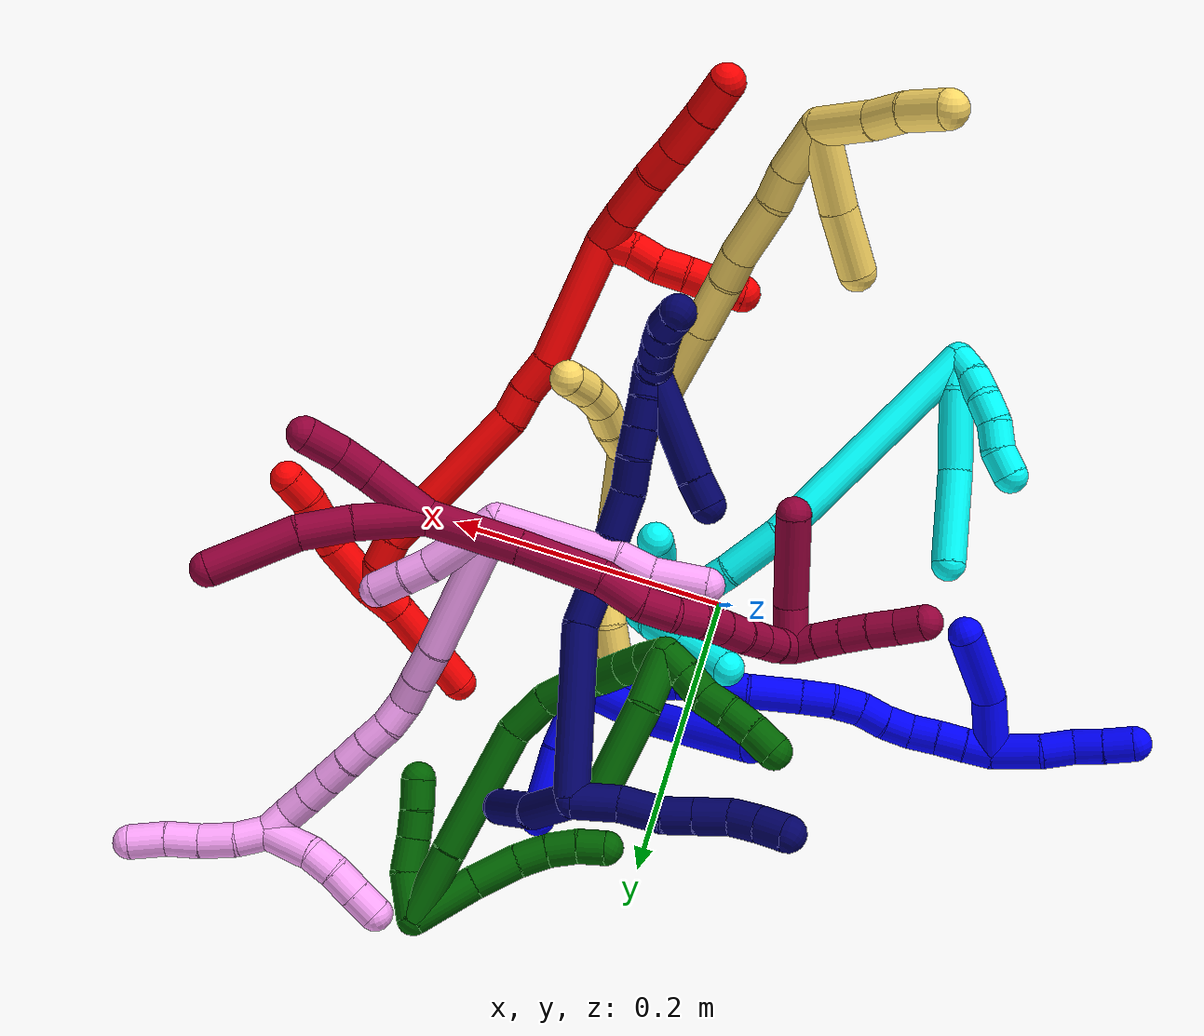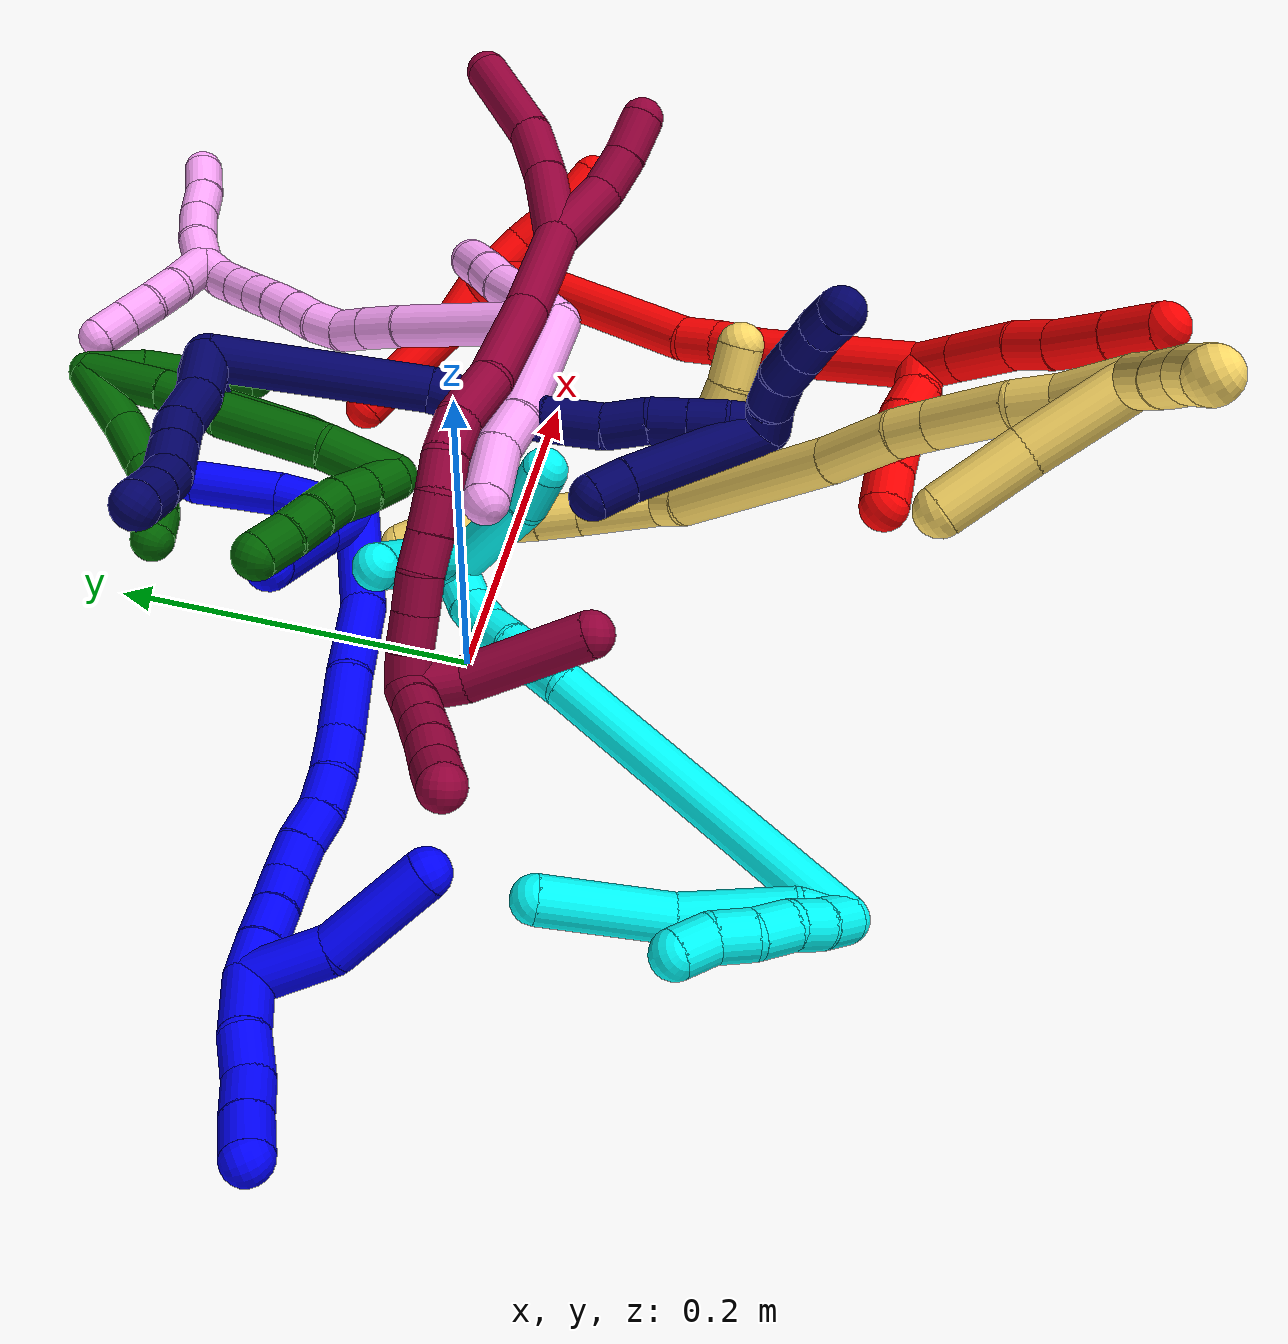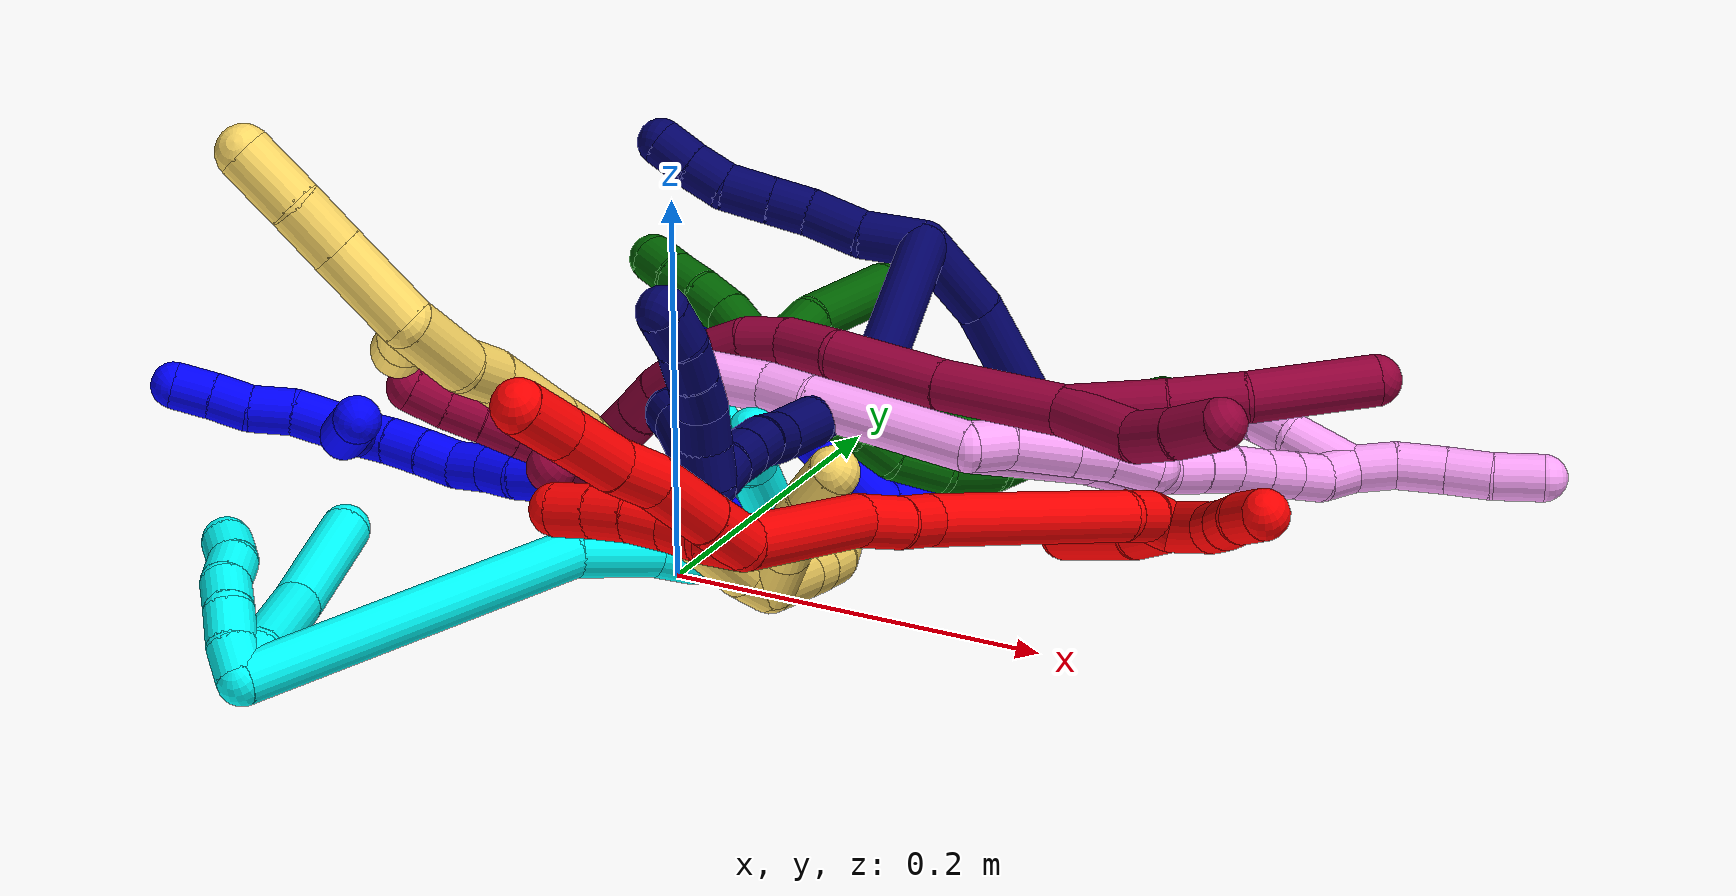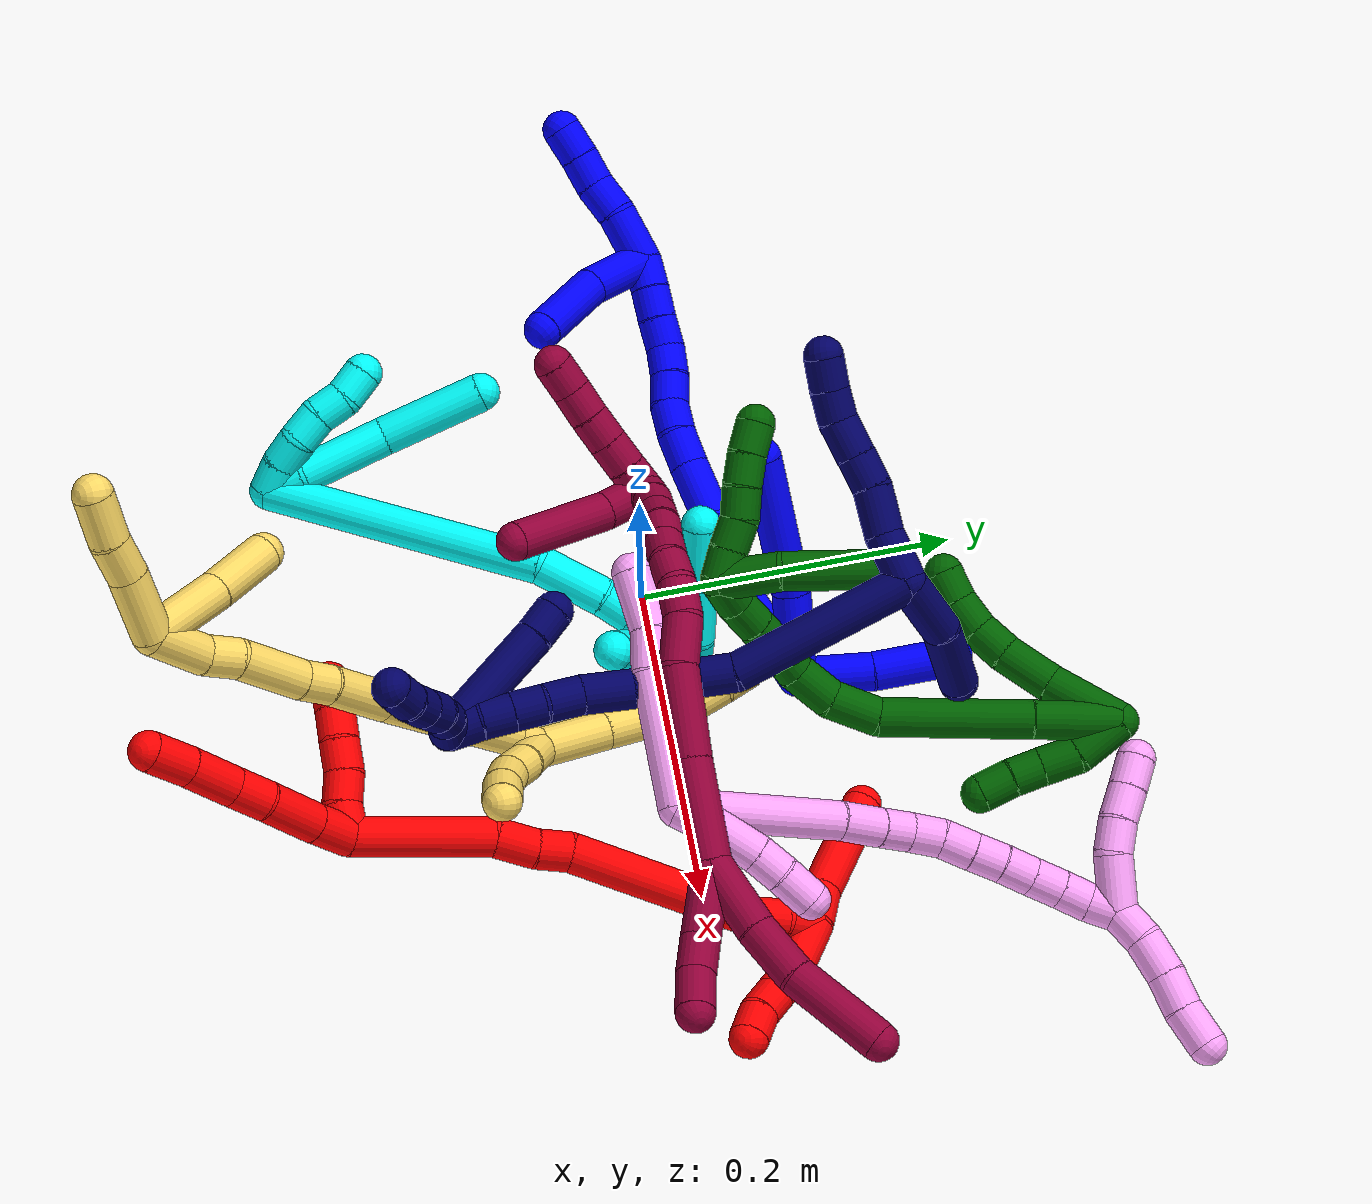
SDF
<sdf version="1.7">
 <world name="default">
  <plugin name="TubeGeneratorPlugin" filename="libtube_generator_plugin.so"/>
  <model name="photoneo_s_sensor">
   <static>1</static>
   <pose>0 0 2 1.57079 1.57079 3.14159</pose>
   <link name="link">
    <inertial><mass>0.1</mass></inertial>
    <sensor name="sensor" type="depth">
     <update_rate>30</update_rate>
     <camera>
      <horizontal_fov>1.22</horizontal_fov>
      <image><width>1920</width><height>1200</height><format>B8G8R8</format></image>
      <clip><near>0.1</near><far>4</far></clip>
      <depth_camera><output>points</output></depth_camera>
     </camera>
     <plugin name="camera_plugin" filename="libgazebo_ros_depth_camera.so">
      <baseline>0.2</baseline>
      <alwaysOn>1</alwaysOn>
      <updateRate>0.0</updateRate>
      <cameraName>camera_ir</cameraName>
      <imageTopicName>/camera/color/image_raw</imageTopicName>
      <cameraInfoTopicName>/camera/color/camera_info</cameraInfoTopicName>
      <depthImageTopicName>/camera/depth/image_raw</depthImageTopicName>
      <depthImageCameraInfoTopicName>/camera/depth/camera_info</depthImageCameraInfoTopicName>
      <pointCloudTopicName>/camera/depth/points</pointCloudTopicName>
      <frameName>fr_optical</frameName>
      <pointCloudCutoff>0.1</pointCloudCutoff>
      <pointCloudCutoffMax>2.0</pointCloudCutoffMax>
      <distortionK1>0</distortionK1>
      <distortionK2>0</distortionK2>
      <distortionK3>0</distortionK3>
      <distortionT1>0</distortionT1>
      <distortionT2>0</distortionT2>
      <CxPrime>0</CxPrime>
      <Cx>0</Cx>
      <Cy>0</Cy>
      <focalLength>0</focalLength>
      <hackBaseline>0</hackBaseline>
     </plugin>
    </sensor>
   </link>
  </model>
  <gravity>0 0 -9.8</gravity>
  <magnetic_field>6e-06 2.3e-05 -4.2e-05</magnetic_field>
  <atmosphere type="adiabatic"/>
  <physics name="default_physics" default="0" type="ode">
   <max_step_size>0.003</max_step_size>
   <real_time_factor>1</real_time_factor>
   <real_time_update_rate>1000</real_time_update_rate>
   <max_contacts>10000</max_contacts>
   <ode>
    <solver>
     <type>quick</type>
     <iters>100</iters>
     <sor>1.3</sor>
     <use_dynamic_moi_rescaling>0</use_dynamic_moi_rescaling>
    </solver>
    <constraints>
     <contact_max_correcting_vel>0</contact_max_correcting_vel>
     <contact_surface_layer>0.001</contact_surface_layer>
     <cfm>0</cfm>
     <erp>0.2</erp>
    </constraints>
   </ode>
  </physics>
  <scene><ambient>0.4 0.4 0.4 1</ambient><background>0.7 0.7 0.7 1</background><shadows>0</shadows></scene>
  <audio><device>default</device></audio>
  <spherical_coordinates>
   <surface_model>EARTH_WGS84</surface_model>
   <latitude_deg>0</latitude_deg>
   <longitude_deg>0</longitude_deg>
   <elevation>0</elevation>
   <heading_deg>0</heading_deg>
  </spherical_coordinates>
  <model name="bin">
   <static>1</static>
   <link name="bottom">
    <collision name="collision-bottom">
     <pose>0 0 -0.01 0 -0 0</pose>
     <geometry><box><size>0.8 0.6 0.02</size></box></geometry>
     <surface>
      <friction><ode><mu>100</mu><mu2>100</mu2></ode></friction>
      <contact><collide_bitmask>65535</collide_bitmask></contact>
     </surface>
    </collision>
   </link>
   <link name="west_wall">
    <collision name="collision-west_wall">
     <pose>-0.41 0 0.1 0 -0 0</pose>
     <geometry><box><size>0.02 0.6 0.2</size></box></geometry>
     <surface>
      <friction><ode><mu>100</mu><mu2>100</mu2></ode></friction>
      <contact><collide_bitmask>65535</collide_bitmask></contact>
     </surface>
    </collision>
   </link>
   <link name="east_wall">
    <collision name="collision-east_wall">
     <pose>0.41 0 0.1 0 -0 0</pose>
     <geometry><box><size>0.02 0.6 0.2</size></box></geometry>
     <surface>
      <friction><ode><mu>100</mu><mu2>100</mu2></ode></friction>
      <contact><collide_bitmask>65535</collide_bitmask></contact>
     </surface>
    </collision>
   </link>
   <link name="south_wall">
    <collision name="collision-south_wall">
     <pose>0 -0.31 0.1 0 -0 0</pose>
     <geometry><box><size>0.8 0.02 0.2</size></box></geometry>
     <surface>
      <friction><ode><mu>100</mu><mu2>100</mu2></ode></friction>
      <contact><collide_bitmask>65535</collide_bitmask></contact>
     </surface>
    </collision>
   </link>
   <link name="north_wall">
    <collision name="collision-north_wall">
     <pose>0 0.31 0.1 0 -0 0</pose>
     <geometry><box><size>0.8 0.02 0.2</size></box></geometry>
     <surface>
      <friction><ode><mu>100</mu><mu2>100</mu2></ode></friction>
      <contact><collide_bitmask>65535</collide_bitmask></contact>
     </surface>
    </collision>
   </link>
  </model>
  <model name="1">
   <static>0</static>
   <link name="1">
    <collision name="collision-cylinder-e_1_2_8">
     <pose>-0.017958 -0.016529 0.014412 0.853694 -0.686164 -0.32211</pose>
     <geometry><cylinder><radius>0.0125</radius><length>0.056689</length></cylinder></geometry>
     <surface>
      <friction><ode><mu>1.16</mu><mu2>1.16</mu2><slip1>0</slip1><slip2>0</slip2></ode></friction>
      <contact><ode><kp>1e+06</kp><kd>1</kd><max_vel>0</max_vel><min_depth>0.001</min_depth></ode></contact>
     </surface>
    </collision>
    <visual name="visual-cylinder-e_1_2_8">
     <pose>-0.017958 -0.016529 0.014412 0.853694 -0.686164 -0.32211</pose>
     <geometry><cylinder><radius>0.0125</radius><length>0.056689</length></cylinder></geometry>
     <material><ambient>0 0 1 1</ambient></material>
    </visual>
    <collision name="collision-cylinder-e_2_8_6">
     <pose>-0.067518 -0.063413 0.044845 1.08519 -0.744131 -0.462194</pose>
     <geometry><cylinder><radius>0.0125</radius><length>0.093311</length></cylinder></geometry>
     <surface>
      <friction><ode><mu>1.16</mu><mu2>1.16</mu2><slip1>0</slip1><slip2>0</slip2></ode></friction>
      <contact><ode><kp>1e+06</kp><kd>1</kd><max_vel>0</max_vel><min_depth>0.001</min_depth></ode></contact>
     </surface>
    </collision>
    <visual name="visual-cylinder-e_2_8_6">
     <pose>-0.067518 -0.063413 0.044845 1.08519 -0.744131 -0.462194</pose>
     <geometry><cylinder><radius>0.0125</radius><length>0.093311</length></cylinder></geometry>
     <material><ambient>0 0 1 1</ambient></material>
    </visual>
    <collision name="collision-cylinder-e_1_2_9">
     <pose>0.016632 -0.002383 0.016977 0.139451 0.770256 0.056606</pose>
     <geometry><cylinder><radius>0.0125</radius><length>0.047771</length></cylinder></geometry>
     <surface>
      <friction><ode><mu>1.16</mu><mu2>1.16</mu2><slip1>0</slip1><slip2>0</slip2></ode></friction>
      <contact><ode><kp>1e+06</kp><kd>1</kd><max_vel>0</max_vel><min_depth>0.001</min_depth></ode></contact>
     </surface>
    </collision>
    <visual name="visual-cylinder-e_1_2_9">
     <pose>0.016632 -0.002383 0.016977 0.139451 0.770256 0.056606</pose>
     <geometry><cylinder><radius>0.0125</radius><length>0.047771</length></cylinder></geometry>
     <material><ambient>0 0 1 1</ambient></material>
    </visual>
    <collision name="collision-cylinder-e_2_9_5">
     <pose>0.049063 -0.006918 0.054635 0.103678 0.64977 0.034949</pose>
     <geometry><cylinder><radius>0.0125</radius><length>0.052229</length></cylinder></geometry>
     <surface>
      <friction><ode><mu>1.16</mu><mu2>1.16</mu2><slip1>0</slip1><slip2>0</slip2></ode></friction>
      <contact><ode><kp>1e+06</kp><kd>1</kd><max_vel>0</max_vel><min_depth>0.001</min_depth></ode></contact>
     </surface>
    </collision>
    <visual name="visual-cylinder-e_2_9_5">
     <pose>0.049063 -0.006918 0.054635 0.103678 0.64977 0.034949</pose>
     <geometry><cylinder><radius>0.0125</radius><length>0.052229</length></cylinder></geometry>
     <material><ambient>0 0 1 1</ambient></material>
    </visual>
    <collision name="collision-cylinder-e_1_2_10">
     <pose>-0.03111 0.00229 0.00993 -0.226666 -1.25423 0.164601</pose>
     <geometry><cylinder><radius>0.0125</radius><length>0.065474</length></cylinder></geometry>
     <surface>
      <friction><ode><mu>1.16</mu><mu2>1.16</mu2><slip1>0</slip1><slip2>0</slip2></ode></friction>
      <contact><ode><kp>1e+06</kp><kd>1</kd><max_vel>0</max_vel><min_depth>0.001</min_depth></ode></contact>
     </surface>
    </collision>
    <visual name="visual-cylinder-e_1_2_10">
     <pose>-0.03111 0.00229 0.00993 -0.226666 -1.25423 0.164601</pose>
     <geometry><cylinder><radius>0.0125</radius><length>0.065474</length></cylinder></geometry>
     <material><ambient>0 0 1 1</ambient></material>
    </visual>
    <collision name="collision-cylinder-e_2_10_11">
     <pose>-0.085366 0.000833 0.03139 0.31428 -1.0883 -0.191163</pose>
     <geometry><cylinder><radius>0.0125</radius><length>0.052256</length></cylinder></geometry>
     <surface>
      <friction><ode><mu>1.16</mu><mu2>1.16</mu2><slip1>0</slip1><slip2>0</slip2></ode></friction>
      <contact><ode><kp>1e+06</kp><kd>1</kd><max_vel>0</max_vel><min_depth>0.001</min_depth></ode></contact>
     </surface>
    </collision>
    <visual name="visual-cylinder-e_2_10_11">
     <pose>-0.085366 0.000833 0.03139 0.31428 -1.0883 -0.191163</pose>
     <geometry><cylinder><radius>0.0125</radius><length>0.052256</length></cylinder></geometry>
     <material><ambient>0 0 1 1</ambient></material>
    </visual>
    <collision name="collision-cylinder-e_3_11_12">
     <pose>-0.125445 -0.002049 0.051614 -0.099276 -1.09445 0.06052</pose>
     <geometry><cylinder><radius>0.0125</radius><length>0.038109</length></cylinder></geometry>
     <surface>
      <friction><ode><mu>1.16</mu><mu2>1.16</mu2><slip1>0</slip1><slip2>0</slip2></ode></friction>
      <contact><ode><kp>1e+06</kp><kd>1</kd><max_vel>0</max_vel><min_depth>0.001</min_depth></ode></contact>
     </surface>
    </collision>
    <visual name="visual-cylinder-e_3_11_12">
     <pose>-0.125445 -0.002049 0.051614 -0.099276 -1.09445 0.06052</pose>
     <geometry><cylinder><radius>0.0125</radius><length>0.038109</length></cylinder></geometry>
     <material><ambient>0 0 1 1</ambient></material>
    </visual>
    <collision name="collision-cylinder-e_4_12_13">
     <pose>-0.152791 -0.001547 0.065908 0.064934 -1.07648 -0.038777</pose>
     <geometry><cylinder><radius>0.0125</radius><length>0.023657</length></cylinder></geometry>
     <surface>
      <friction><ode><mu>1.16</mu><mu2>1.16</mu2><slip1>0</slip1><slip2>0</slip2></ode></friction>
      <contact><ode><kp>1e+06</kp><kd>1</kd><max_vel>0</max_vel><min_depth>0.001</min_depth></ode></contact>
     </surface>
    </collision>
    <visual name="visual-cylinder-e_4_12_13">
     <pose>-0.152791 -0.001547 0.065908 0.064934 -1.07648 -0.038777</pose>
     <geometry><cylinder><radius>0.0125</radius><length>0.023657</length></cylinder></geometry>
     <material><ambient>0 0 1 1</ambient></material>
    </visual>
    <collision name="collision-cylinder-e_5_13_14">
     <pose>-0.17131 -0.000953 0.077697 -0.153568 -0.912991 0.075528</pose>
     <geometry><cylinder><radius>0.0125</radius><length>0.020489</length></cylinder></geometry>
     <surface>
      <friction><ode><mu>1.16</mu><mu2>1.16</mu2><slip1>0</slip1><slip2>0</slip2></ode></friction>
      <contact><ode><kp>1e+06</kp><kd>1</kd><max_vel>0</max_vel><min_depth>0.001</min_depth></ode></contact>
     </surface>
    </collision>
    <visual name="visual-cylinder-e_5_13_14">
     <pose>-0.17131 -0.000953 0.077697 -0.153568 -0.912991 0.075528</pose>
     <geometry><cylinder><radius>0.0125</radius><length>0.020489</length></cylinder></geometry>
     <material><ambient>0 0 1 1</ambient></material>
    </visual>
    <collision name="collision-cylinder-e_6_14_15">
     <pose>-0.185861 -3e-05 0.091534 0.004593 -0.700223 -0.001677</pose>
     <geometry><cylinder><radius>0.0125</radius><length>0.02</length></cylinder></geometry>
     <surface>
      <friction><ode><mu>1.16</mu><mu2>1.16</mu2><slip1>0</slip1><slip2>0</slip2></ode></friction>
      <contact><ode><kp>1e+06</kp><kd>1</kd><max_vel>0</max_vel><min_depth>0.001</min_depth></ode></contact>
     </surface>
    </collision>
    <visual name="visual-cylinder-e_6_14_15">
     <pose>-0.185861 -3e-05 0.091534 0.004593 -0.700223 -0.001677</pose>
     <geometry><cylinder><radius>0.0125</radius><length>0.02</length></cylinder></geometry>
     <material><ambient>0 0 1 1</ambient></material>
    </visual>
    <collision name="collision-cylinder-e_7_15_16">
     <pose>-0.199757 0.000527 0.105827 -0.08893 -0.840542 0.039764</pose>
     <geometry><cylinder><radius>0.0125</radius><length>0.020006</length></cylinder></geometry>
     <surface>
      <friction><ode><mu>1.16</mu><mu2>1.16</mu2><slip1>0</slip1><slip2>0</slip2></ode></friction>
      <contact><ode><kp>1e+06</kp><kd>1</kd><max_vel>0</max_vel><min_depth>0.001</min_depth></ode></contact>
     </surface>
    </collision>
    <visual name="visual-cylinder-e_7_15_16">
     <pose>-0.199757 0.000527 0.105827 -0.08893 -0.840542 0.039764</pose>
     <geometry><cylinder><radius>0.0125</radius><length>0.020006</length></cylinder></geometry>
     <material><ambient>0 0 1 1</ambient></material>
    </visual>
    <collision name="collision-cylinder-e_8_16_17">
     <pose>-0.215519 -0.001143 0.117558 0.418658 -0.980638 -0.225837</pose>
     <geometry><cylinder><radius>0.0125</radius><length>0.020004</length></cylinder></geometry>
     <surface>
      <friction><ode><mu>1.16</mu><mu2>1.16</mu2><slip1>0</slip1><slip2>0</slip2></ode></friction>
      <contact><ode><kp>1e+06</kp><kd>1</kd><max_vel>0</max_vel><min_depth>0.001</min_depth></ode></contact>
     </surface>
    </collision>
    <visual name="visual-cylinder-e_8_16_17">
     <pose>-0.215519 -0.001143 0.117558 0.418658 -0.980638 -0.225837</pose>
     <geometry><cylinder><radius>0.0125</radius><length>0.020004</length></cylinder></geometry>
     <material><ambient>0 0 1 1</ambient></material>
    </visual>
    <collision name="collision-cylinder-e_9_17_18">
     <pose>-0.231933 -0.005147 0.12824 0.301662 -0.944573 -0.154971</pose>
     <geometry><cylinder><radius>0.0125</radius><length>0.020001</length></cylinder></geometry>
     <surface>
      <friction><ode><mu>1.16</mu><mu2>1.16</mu2><slip1>0</slip1><slip2>0</slip2></ode></friction>
      <contact><ode><kp>1e+06</kp><kd>1</kd><max_vel>0</max_vel><min_depth>0.001</min_depth></ode></contact>
     </surface>
    </collision>
    <visual name="visual-cylinder-e_9_17_18">
     <pose>-0.231933 -0.005147 0.12824 0.301662 -0.944573 -0.154971</pose>
     <geometry><cylinder><radius>0.0125</radius><length>0.020001</length></cylinder></geometry>
     <material><ambient>0 0 1 1</ambient></material>
    </visual>
    <collision name="collision-cylinder-e_10_18_1">
     <pose>-0.248323 -0.007901 0.139344 0.181856 -0.976625 -0.096798</pose>
     <geometry><cylinder><radius>0.0125</radius><length>0.020004</length></cylinder></geometry>
     <surface>
      <friction><ode><mu>1.16</mu><mu2>1.16</mu2><slip1>0</slip1><slip2>0</slip2></ode></friction>
      <contact><ode><kp>1e+06</kp><kd>1</kd><max_vel>0</max_vel><min_depth>0.001</min_depth></ode></contact>
     </surface>
    </collision>
    <visual name="visual-cylinder-e_10_18_1">
     <pose>-0.248323 -0.007901 0.139344 0.181856 -0.976625 -0.096798</pose>
     <geometry><cylinder><radius>0.0125</radius><length>0.020004</length></cylinder></geometry>
     <material><ambient>0 0 1 1</ambient></material>
    </visual>
    <collision name="collision-cylinder-e_1_1_19">
     <pose>-0.272541 -0.013643 0.149703 0.772515 -1.16865 -0.525502</pose>
     <geometry><cylinder><radius>0.0125</radius><length>0.034623</length></cylinder></geometry>
     <surface>
      <friction><ode><mu>1.16</mu><mu2>1.16</mu2><slip1>0</slip1><slip2>0</slip2></ode></friction>
      <contact><ode><kp>1e+06</kp><kd>1</kd><max_vel>0</max_vel><min_depth>0.001</min_depth></ode></contact>
     </surface>
    </collision>
    <visual name="visual-cylinder-e_1_1_19">
     <pose>-0.272541 -0.013643 0.149703 0.772515 -1.16865 -0.525502</pose>
     <geometry><cylinder><radius>0.0125</radius><length>0.034623</length></cylinder></geometry>
     <material><ambient>0 0 1 1</ambient></material>
    </visual>
    <collision name="collision-cylinder-e_2_19_20">
     <pose>-0.299927 -0.018977 0.15691 0.251768 -1.36166 -0.204311</pose>
     <geometry><cylinder><radius>0.0125</radius><length>0.02342</length></cylinder></geometry>
     <surface>
      <friction><ode><mu>1.16</mu><mu2>1.16</mu2><slip1>0</slip1><slip2>0</slip2></ode></friction>
      <contact><ode><kp>1e+06</kp><kd>1</kd><max_vel>0</max_vel><min_depth>0.001</min_depth></ode></contact>
     </surface>
    </collision>
    <visual name="visual-cylinder-e_2_19_20">
     <pose>-0.299927 -0.018977 0.15691 0.251768 -1.36166 -0.204311</pose>
     <geometry><cylinder><radius>0.0125</radius><length>0.02342</length></cylinder></geometry>
     <material><ambient>0 0 1 1</ambient></material>
    </visual>
    <collision name="collision-cylinder-e_3_20_21">
     <pose>-0.320998 -0.022511 0.16209 0.803235 -1.17055 -0.54873</pose>
     <geometry><cylinder><radius>0.0125</radius><length>0.020884</length></cylinder></geometry>
     <surface>
      <friction><ode><mu>1.16</mu><mu2>1.16</mu2><slip1>0</slip1><slip2>0</slip2></ode></friction>
      <contact><ode><kp>1e+06</kp><kd>1</kd><max_vel>0</max_vel><min_depth>0.001</min_depth></ode></contact>
     </surface>
    </collision>
    <visual name="visual-cylinder-e_3_20_21">
     <pose>-0.320998 -0.022511 0.16209 0.803235 -1.17055 -0.54873</pose>
     <geometry><cylinder><radius>0.0125</radius><length>0.020884</length></cylinder></geometry>
     <material><ambient>0 0 1 1</ambient></material>
    </visual>
    <collision name="collision-cylinder-e_4_21_4">
     <pose>-0.340576 -0.028037 0.167161 0.857956 -1.23882 -0.630494</pose>
     <geometry><cylinder><radius>0.0125</radius><length>0.021073</length></cylinder></geometry>
     <surface>
      <friction><ode><mu>1.16</mu><mu2>1.16</mu2><slip1>0</slip1><slip2>0</slip2></ode></friction>
      <contact><ode><kp>1e+06</kp><kd>1</kd><max_vel>0</max_vel><min_depth>0.001</min_depth></ode></contact>
     </surface>
    </collision>
    <visual name="visual-cylinder-e_4_21_4">
     <pose>-0.340576 -0.028037 0.167161 0.857956 -1.23882 -0.630494</pose>
     <geometry><cylinder><radius>0.0125</radius><length>0.021073</length></cylinder></geometry>
     <material><ambient>0 0 1 1</ambient></material>
    </visual>
    <collision name="collision-cylinder-e_1_1_22">
     <pose>-0.261856 -0.013621 0.124397 2.9154 -0.244895 -1.65089</pose>
     <geometry><cylinder><radius>0.0125</radius><length>0.043266</length></cylinder></geometry>
     <surface>
      <friction><ode><mu>1.16</mu><mu2>1.16</mu2><slip1>0</slip1><slip2>0</slip2></ode></friction>
      <contact><ode><kp>1e+06</kp><kd>1</kd><max_vel>0</max_vel><min_depth>0.001</min_depth></ode></contact>
     </surface>
    </collision>
    <visual name="visual-cylinder-e_1_1_22">
     <pose>-0.261856 -0.013621 0.124397 2.9154 -0.244895 -1.65089</pose>
     <geometry><cylinder><radius>0.0125</radius><length>0.043266</length></cylinder></geometry>
     <material><ambient>0 0 1 1</ambient></material>
    </visual>
    <collision name="collision-cylinder-e_2_22_3">
     <pose>-0.26606 -0.029555 0.077915 2.73437 0.036686 0.177234</pose>
     <geometry><cylinder><radius>0.0125</radius><length>0.056734</length></cylinder></geometry>
     <surface>
      <friction><ode><mu>1.16</mu><mu2>1.16</mu2><slip1>0</slip1><slip2>0</slip2></ode></friction>
      <contact><ode><kp>1e+06</kp><kd>1</kd><max_vel>0</max_vel><min_depth>0.001</min_depth></ode></contact>
     </surface>
    </collision>
    <visual name="visual-cylinder-e_2_22_3">
     <pose>-0.26606 -0.029555 0.077915 2.73437 0.036686 0.177234</pose>
     <geometry><cylinder><radius>0.0125</radius><length>0.056734</length></cylinder></geometry>
     <material><ambient>0 0 1 1</ambient></material>
    </visual>
    <collision name="collision-sphere-3">
     <pose>-0.26502 -0.040782 0.051885 0 -0 0</pose>
     <geometry><sphere><radius>0.0125</radius></sphere></geometry>
     <surface>
      <friction><ode><mu>1.16</mu><mu2>1.16</mu2><slip1>0</slip1><slip2>0</slip2></ode></friction>
      <contact><ode><kp>1e+06</kp><kd>1</kd><max_vel>0</max_vel><min_depth>0.001</min_depth></ode></contact>
     </surface>
    </collision>
    <visual name="visual-sphere-3">
     <pose>-0.26502 -0.040782 0.051885 0 -0 0</pose>
     <geometry><sphere><radius>0.0125</radius></sphere></geometry>
     <material><ambient>0 0 1 1</ambient></material>
    </visual>
    <collision name="collision-sphere-22">
     <pose>-0.267101 -0.018328 0.103944 0 -0 0</pose>
     <geometry><sphere><radius>0.0125</radius></sphere></geometry>
     <surface>
      <friction><ode><mu>1.16</mu><mu2>1.16</mu2><slip1>0</slip1><slip2>0</slip2></ode></friction>
      <contact><ode><kp>1e+06</kp><kd>1</kd><max_vel>0</max_vel><min_depth>0.001</min_depth></ode></contact>
     </surface>
    </collision>
    <visual name="visual-sphere-22">
     <pose>-0.267101 -0.018328 0.103944 0 -0 0</pose>
     <geometry><sphere><radius>0.0125</radius></sphere></geometry>
     <material><ambient>0 0 1 1</ambient></material>
    </visual>
    <collision name="collision-sphere-4">
     <pose>-0.350537 -0.030634 0.169407 0 -0 0</pose>
     <geometry><sphere><radius>0.0125</radius></sphere></geometry>
     <surface>
      <friction><ode><mu>1.16</mu><mu2>1.16</mu2><slip1>0</slip1><slip2>0</slip2></ode></friction>
      <contact><ode><kp>1e+06</kp><kd>1</kd><max_vel>0</max_vel><min_depth>0.001</min_depth></ode></contact>
     </surface>
    </collision>
    <visual name="visual-sphere-4">
     <pose>-0.350537 -0.030634 0.169407 0 -0 0</pose>
     <geometry><sphere><radius>0.0125</radius></sphere></geometry>
     <material><ambient>0 0 1 1</ambient></material>
    </visual>
    <collision name="collision-sphere-21">
     <pose>-0.330615 -0.025439 0.164915 0 -0 0</pose>
     <geometry><sphere><radius>0.0125</radius></sphere></geometry>
     <surface>
      <friction><ode><mu>1.16</mu><mu2>1.16</mu2><slip1>0</slip1><slip2>0</slip2></ode></friction>
      <contact><ode><kp>1e+06</kp><kd>1</kd><max_vel>0</max_vel><min_depth>0.001</min_depth></ode></contact>
     </surface>
    </collision>
    <visual name="visual-sphere-21">
     <pose>-0.330615 -0.025439 0.164915 0 -0 0</pose>
     <geometry><sphere><radius>0.0125</radius></sphere></geometry>
     <material><ambient>0 0 1 1</ambient></material>
    </visual>
    <collision name="collision-sphere-20">
     <pose>-0.311381 -0.019583 0.159265 0 -0 0</pose>
     <geometry><sphere><radius>0.0125</radius></sphere></geometry>
     <surface>
      <friction><ode><mu>1.16</mu><mu2>1.16</mu2><slip1>0</slip1><slip2>0</slip2></ode></friction>
      <contact><ode><kp>1e+06</kp><kd>1</kd><max_vel>0</max_vel><min_depth>0.001</min_depth></ode></contact>
     </surface>
    </collision>
    <visual name="visual-sphere-20">
     <pose>-0.311381 -0.019583 0.159265 0 -0 0</pose>
     <geometry><sphere><radius>0.0125</radius></sphere></geometry>
     <material><ambient>0 0 1 1</ambient></material>
    </visual>
    <collision name="collision-sphere-10">
     <pose>-0.062221 0.00458 0.019861 0 -0 0</pose>
     <geometry><sphere><radius>0.0125</radius></sphere></geometry>
     <surface>
      <friction><ode><mu>1.16</mu><mu2>1.16</mu2><slip1>0</slip1><slip2>0</slip2></ode></friction>
      <contact><ode><kp>1e+06</kp><kd>1</kd><max_vel>0</max_vel><min_depth>0.001</min_depth></ode></contact>
     </surface>
    </collision>
    <visual name="visual-sphere-10">
     <pose>-0.062221 0.00458 0.019861 0 -0 0</pose>
     <geometry><sphere><radius>0.0125</radius></sphere></geometry>
     <material><ambient>0 0 1 1</ambient></material>
    </visual>
    <collision name="collision-sphere-5">
     <pose>0.064863 -0.00907 0.075317 0 -0 0</pose>
     <geometry><sphere><radius>0.0125</radius></sphere></geometry>
     <surface>
      <friction><ode><mu>1.16</mu><mu2>1.16</mu2><slip1>0</slip1><slip2>0</slip2></ode></friction>
      <contact><ode><kp>1e+06</kp><kd>1</kd><max_vel>0</max_vel><min_depth>0.001</min_depth></ode></contact>
     </surface>
    </collision>
    <visual name="visual-sphere-5">
     <pose>0.064863 -0.00907 0.075317 0 -0 0</pose>
     <geometry><sphere><radius>0.0125</radius></sphere></geometry>
     <material><ambient>0 0 1 1</ambient></material>
    </visual>
    <collision name="collision-sphere-6">
     <pose>-0.099119 -0.093768 0.060865 0 -0 0</pose>
     <geometry><sphere><radius>0.0125</radius></sphere></geometry>
     <surface>
      <friction><ode><mu>1.16</mu><mu2>1.16</mu2><slip1>0</slip1><slip2>0</slip2></ode></friction>
      <contact><ode><kp>1e+06</kp><kd>1</kd><max_vel>0</max_vel><min_depth>0.001</min_depth></ode></contact>
     </surface>
    </collision>
    <visual name="visual-sphere-6">
     <pose>-0.099119 -0.093768 0.060865 0 -0 0</pose>
     <geometry><sphere><radius>0.0125</radius></sphere></geometry>
     <material><ambient>0 0 1 1</ambient></material>
    </visual>
    <collision name="collision-sphere-9">
     <pose>0.033264 -0.004766 0.033954 0 -0 0</pose>
     <geometry><sphere><radius>0.0125</radius></sphere></geometry>
     <surface>
      <friction><ode><mu>1.16</mu><mu2>1.16</mu2><slip1>0</slip1><slip2>0</slip2></ode></friction>
      <contact><ode><kp>1e+06</kp><kd>1</kd><max_vel>0</max_vel><min_depth>0.001</min_depth></ode></contact>
     </surface>
    </collision>
    <visual name="visual-sphere-9">
     <pose>0.033264 -0.004766 0.033954 0 -0 0</pose>
     <geometry><sphere><radius>0.0125</radius></sphere></geometry>
     <material><ambient>0 0 1 1</ambient></material>
    </visual>
    <collision name="collision-sphere-2">
     <geometry><sphere><radius>0.0125</radius></sphere></geometry>
     <surface>
      <friction><ode><mu>1.16</mu><mu2>1.16</mu2><slip1>0</slip1><slip2>0</slip2></ode></friction>
      <contact><ode><kp>1e+06</kp><kd>1</kd><max_vel>0</max_vel><min_depth>0.001</min_depth></ode></contact>
     </surface>
    </collision>
    <visual name="visual-sphere-2">
     <geometry><sphere><radius>0.0125</radius></sphere></geometry>
     <material><ambient>0 0 1 1</ambient></material>
    </visual>
    <collision name="collision-sphere-19">
     <pose>-0.288472 -0.018372 0.154555 0 -0 0</pose>
     <geometry><sphere><radius>0.0125</radius></sphere></geometry>
     <surface>
      <friction><ode><mu>1.16</mu><mu2>1.16</mu2><slip1>0</slip1><slip2>0</slip2></ode></friction>
      <contact><ode><kp>1e+06</kp><kd>1</kd><max_vel>0</max_vel><min_depth>0.001</min_depth></ode></contact>
     </surface>
    </collision>
    <visual name="visual-sphere-19">
     <pose>-0.288472 -0.018372 0.154555 0 -0 0</pose>
     <geometry><sphere><radius>0.0125</radius></sphere></geometry>
     <material><ambient>0 0 1 1</ambient></material>
    </visual>
    <collision name="collision-sphere-8">
     <pose>-0.035917 -0.033057 0.028824 0 -0 0</pose>
     <geometry><sphere><radius>0.0125</radius></sphere></geometry>
     <surface>
      <friction><ode><mu>1.16</mu><mu2>1.16</mu2><slip1>0</slip1><slip2>0</slip2></ode></friction>
      <contact><ode><kp>1e+06</kp><kd>1</kd><max_vel>0</max_vel><min_depth>0.001</min_depth></ode></contact>
     </surface>
    </collision>
    <visual name="visual-sphere-8">
     <pose>-0.035917 -0.033057 0.028824 0 -0 0</pose>
     <geometry><sphere><radius>0.0125</radius></sphere></geometry>
     <material><ambient>0 0 1 1</ambient></material>
    </visual>
    <collision name="collision-sphere-11">
     <pose>-0.108511 -0.002915 0.042919 0 -0 0</pose>
     <geometry><sphere><radius>0.0125</radius></sphere></geometry>
     <surface>
      <friction><ode><mu>1.16</mu><mu2>1.16</mu2><slip1>0</slip1><slip2>0</slip2></ode></friction>
      <contact><ode><kp>1e+06</kp><kd>1</kd><max_vel>0</max_vel><min_depth>0.001</min_depth></ode></contact>
     </surface>
    </collision>
    <visual name="visual-sphere-11">
     <pose>-0.108511 -0.002915 0.042919 0 -0 0</pose>
     <geometry><sphere><radius>0.0125</radius></sphere></geometry>
     <material><ambient>0 0 1 1</ambient></material>
    </visual>
    <collision name="collision-sphere-12">
     <pose>-0.142378 -0.001183 0.060308 0 -0 0</pose>
     <geometry><sphere><radius>0.0125</radius></sphere></geometry>
     <surface>
      <friction><ode><mu>1.16</mu><mu2>1.16</mu2><slip1>0</slip1><slip2>0</slip2></ode></friction>
      <contact><ode><kp>1e+06</kp><kd>1</kd><max_vel>0</max_vel><min_depth>0.001</min_depth></ode></contact>
     </surface>
    </collision>
    <visual name="visual-sphere-12">
     <pose>-0.142378 -0.001183 0.060308 0 -0 0</pose>
     <geometry><sphere><radius>0.0125</radius></sphere></geometry>
     <material><ambient>0 0 1 1</ambient></material>
    </visual>
    <collision name="collision-sphere-13">
     <pose>-0.163203 -0.001911 0.071508 0 -0 0</pose>
     <geometry><sphere><radius>0.0125</radius></sphere></geometry>
     <surface>
      <friction><ode><mu>1.16</mu><mu2>1.16</mu2><slip1>0</slip1><slip2>0</slip2></ode></friction>
      <contact><ode><kp>1e+06</kp><kd>1</kd><max_vel>0</max_vel><min_depth>0.001</min_depth></ode></contact>
     </surface>
    </collision>
    <visual name="visual-sphere-13">
     <pose>-0.163203 -0.001911 0.071508 0 -0 0</pose>
     <geometry><sphere><radius>0.0125</radius></sphere></geometry>
     <material><ambient>0 0 1 1</ambient></material>
    </visual>
    <collision name="collision-sphere-14">
     <pose>-0.179417 5e-06 0.083887 0 -0 0</pose>
     <geometry><sphere><radius>0.0125</radius></sphere></geometry>
     <surface>
      <friction><ode><mu>1.16</mu><mu2>1.16</mu2><slip1>0</slip1><slip2>0</slip2></ode></friction>
      <contact><ode><kp>1e+06</kp><kd>1</kd><max_vel>0</max_vel><min_depth>0.001</min_depth></ode></contact>
     </surface>
    </collision>
    <visual name="visual-sphere-14">
     <pose>-0.179417 5e-06 0.083887 0 -0 0</pose>
     <geometry><sphere><radius>0.0125</radius></sphere></geometry>
     <material><ambient>0 0 1 1</ambient></material>
    </visual>
    <collision name="collision-sphere-15">
     <pose>-0.192305 -6.5e-05 0.099181 0 -0 0</pose>
     <geometry><sphere><radius>0.0125</radius></sphere></geometry>
     <surface>
      <friction><ode><mu>1.16</mu><mu2>1.16</mu2><slip1>0</slip1><slip2>0</slip2></ode></friction>
      <contact><ode><kp>1e+06</kp><kd>1</kd><max_vel>0</max_vel><min_depth>0.001</min_depth></ode></contact>
     </surface>
    </collision>
    <visual name="visual-sphere-15">
     <pose>-0.192305 -6.5e-05 0.099181 0 -0 0</pose>
     <geometry><sphere><radius>0.0125</radius></sphere></geometry>
     <material><ambient>0 0 1 1</ambient></material>
    </visual>
    <collision name="collision-sphere-16">
     <pose>-0.207209 0.00112 0.112473 0 -0 0</pose>
     <geometry><sphere><radius>0.0125</radius></sphere></geometry>
     <surface>
      <friction><ode><mu>1.16</mu><mu2>1.16</mu2><slip1>0</slip1><slip2>0</slip2></ode></friction>
      <contact><ode><kp>1e+06</kp><kd>1</kd><max_vel>0</max_vel><min_depth>0.001</min_depth></ode></contact>
     </surface>
    </collision>
    <visual name="visual-sphere-16">
     <pose>-0.207209 0.00112 0.112473 0 -0 0</pose>
     <geometry><sphere><radius>0.0125</radius></sphere></geometry>
     <material><ambient>0 0 1 1</ambient></material>
    </visual>
    <collision name="collision-sphere-17">
     <pose>-0.22383 -0.003406 0.122644 0 -0 0</pose>
     <geometry><sphere><radius>0.0125</radius></sphere></geometry>
     <surface>
      <friction><ode><mu>1.16</mu><mu2>1.16</mu2><slip1>0</slip1><slip2>0</slip2></ode></friction>
      <contact><ode><kp>1e+06</kp><kd>1</kd><max_vel>0</max_vel><min_depth>0.001</min_depth></ode></contact>
     </surface>
    </collision>
    <visual name="visual-sphere-17">
     <pose>-0.22383 -0.003406 0.122644 0 -0 0</pose>
     <geometry><sphere><radius>0.0125</radius></sphere></geometry>
     <material><ambient>0 0 1 1</ambient></material>
    </visual>
    <collision name="collision-sphere-18">
     <pose>-0.240036 -0.006888 0.133837 0 -0 0</pose>
     <geometry><sphere><radius>0.0125</radius></sphere></geometry>
     <surface>
      <friction><ode><mu>1.16</mu><mu2>1.16</mu2><slip1>0</slip1><slip2>0</slip2></ode></friction>
      <contact><ode><kp>1e+06</kp><kd>1</kd><max_vel>0</max_vel><min_depth>0.001</min_depth></ode></contact>
     </surface>
    </collision>
    <visual name="visual-sphere-18">
     <pose>-0.240036 -0.006888 0.133837 0 -0 0</pose>
     <geometry><sphere><radius>0.0125</radius></sphere></geometry>
     <material><ambient>0 0 1 1</ambient></material>
    </visual>
    <collision name="collision-sphere-1">
     <pose>-0.256611 -0.008914 0.144851 0 -0 0</pose>
     <geometry><sphere><radius>0.0125</radius></sphere></geometry>
     <surface>
      <friction><ode><mu>1.16</mu><mu2>1.16</mu2><slip1>0</slip1><slip2>0</slip2></ode></friction>
      <contact><ode><kp>1e+06</kp><kd>1</kd><max_vel>0</max_vel><min_depth>0.001</min_depth></ode></contact>
     </surface>
    </collision>
    <visual name="visual-sphere-1">
     <pose>-0.256611 -0.008914 0.144851 0 -0 0</pose>
     <geometry><sphere><radius>0.0125</radius></sphere></geometry>
     <material><ambient>0 0 1 1</ambient></material>
    </visual>
    <inertial>
     <pose>-0.134347 -0.015717 0.07106 0 -0 0</pose>
     <mass>0.75</mass>
     <inertia><ixx>5.7e-05</ixx><ixy>0</ixy><ixz>0</ixz><iyy>9.2e-05</iyy><iyz>0</iyz><izz>0.000192</izz></inertia>
    </inertial>
   </link>
   <pose>0.075104 0.085958 0.016699 -1.70165 0.05189 0.660395</pose>
  </model>
  <model name="2">
   <static>0</static>
   <link name="2">
    <collision name="collision-cylinder-e_1_2_8">
     <pose>-0.001569 -0.006447 0.01197 0.494054 -0.114867 -0.028997</pose>
     <geometry><cylinder><radius>0.0125</radius><length>0.027372</length></cylinder></geometry>
     <surface>
      <friction><ode><mu>1.16</mu><mu2>1.16</mu2><slip1>0</slip1><slip2>0</slip2></ode></friction>
      <contact><ode><kp>1e+06</kp><kd>1</kd><max_vel>0</max_vel><min_depth>0.001</min_depth></ode></contact>
     </surface>
    </collision>
    <visual name="visual-cylinder-e_1_2_8">
     <pose>-0.001569 -0.006447 0.01197 0.494054 -0.114867 -0.028997</pose>
     <geometry><cylinder><radius>0.0125</radius><length>0.027372</length></cylinder></geometry>
     <material><ambient>1 0 0 1</ambient></material>
    </visual>
    <collision name="collision-cylinder-e_2_8_9">
     <pose>-0.006123 -0.02182 0.040136 0.503717 -0.160076 -0.041273</pose>
     <geometry><cylinder><radius>0.0125</radius><length>0.037463</length></cylinder></geometry>
     <surface>
      <friction><ode><mu>1.16</mu><mu2>1.16</mu2><slip1>0</slip1><slip2>0</slip2></ode></friction>
      <contact><ode><kp>1e+06</kp><kd>1</kd><max_vel>0</max_vel><min_depth>0.001</min_depth></ode></contact>
     </surface>
    </collision>
    <visual name="visual-cylinder-e_2_8_9">
     <pose>-0.006123 -0.02182 0.040136 0.503717 -0.160076 -0.041273</pose>
     <geometry><cylinder><radius>0.0125</radius><length>0.037463</length></cylinder></geometry>
     <material><ambient>1 0 0 1</ambient></material>
    </visual>
    <collision name="collision-cylinder-e_3_9_10">
     <pose>-0.010191 -0.03801 0.065617 0.663798 -0.09153 -0.031565</pose>
     <geometry><cylinder><radius>0.0125</radius><length>0.023679</length></cylinder></geometry>
     <surface>
      <friction><ode><mu>1.16</mu><mu2>1.16</mu2><slip1>0</slip1><slip2>0</slip2></ode></friction>
      <contact><ode><kp>1e+06</kp><kd>1</kd><max_vel>0</max_vel><min_depth>0.001</min_depth></ode></contact>
     </surface>
    </collision>
    <visual name="visual-cylinder-e_3_9_10">
     <pose>-0.010191 -0.03801 0.065617 0.663798 -0.09153 -0.031565</pose>
     <geometry><cylinder><radius>0.0125</radius><length>0.023679</length></cylinder></geometry>
     <material><ambient>1 0 0 1</ambient></material>
    </visual>
    <collision name="collision-cylinder-e_4_10_11">
     <pose>-0.013605 -0.053832 0.089002 0.545583 -0.140474 -0.039359</pose>
     <geometry><cylinder><radius>0.0125</radius><length>0.033313</length></cylinder></geometry>
     <surface>
      <friction><ode><mu>1.16</mu><mu2>1.16</mu2><slip1>0</slip1><slip2>0</slip2></ode></friction>
      <contact><ode><kp>1e+06</kp><kd>1</kd><max_vel>0</max_vel><min_depth>0.001</min_depth></ode></contact>
     </surface>
    </collision>
    <visual name="visual-cylinder-e_4_10_11">
     <pose>-0.013605 -0.053832 0.089002 0.545583 -0.140474 -0.039359</pose>
     <geometry><cylinder><radius>0.0125</radius><length>0.033313</length></cylinder></geometry>
     <material><ambient>1 0 0 1</ambient></material>
    </visual>
    <collision name="collision-cylinder-e_5_11_6">
     <pose>-0.01732 -0.069485 0.115191 0.530641 -0.098292 -0.026729</pose>
     <geometry><cylinder><radius>0.0125</radius><length>0.028172</length></cylinder></geometry>
     <surface>
      <friction><ode><mu>1.16</mu><mu2>1.16</mu2><slip1>0</slip1><slip2>0</slip2></ode></friction>
      <contact><ode><kp>1e+06</kp><kd>1</kd><max_vel>0</max_vel><min_depth>0.001</min_depth></ode></contact>
     </surface>
    </collision>
    <visual name="visual-cylinder-e_5_11_6">
     <pose>-0.01732 -0.069485 0.115191 0.530641 -0.098292 -0.026729</pose>
     <geometry><cylinder><radius>0.0125</radius><length>0.028172</length></cylinder></geometry>
     <material><ambient>1 0 0 1</ambient></material>
    </visual>
    <collision name="collision-cylinder-e_1_2_12">
     <pose>-0.006349 -0.007615 -0.001305 1.74052 -0.687919 -0.803411</pose>
     <geometry><cylinder><radius>0.0125</radius><length>0.02</length></cylinder></geometry>
     <surface>
      <friction><ode><mu>1.16</mu><mu2>1.16</mu2><slip1>0</slip1><slip2>0</slip2></ode></friction>
      <contact><ode><kp>1e+06</kp><kd>1</kd><max_vel>0</max_vel><min_depth>0.001</min_depth></ode></contact>
     </surface>
    </collision>
    <visual name="visual-cylinder-e_1_2_12">
     <pose>-0.006349 -0.007615 -0.001305 1.74052 -0.687919 -0.803411</pose>
     <geometry><cylinder><radius>0.0125</radius><length>0.02</length></cylinder></geometry>
     <material><ambient>1 0 0 1</ambient></material>
    </visual>
    <collision name="collision-cylinder-e_2_12_13">
     <pose>-0.020387 -0.02091 -0.005545 2.04772 -0.877048 -1.31262</pose>
     <geometry><cylinder><radius>0.0125</radius><length>0.02</length></cylinder></geometry>
     <surface>
      <friction><ode><mu>1.16</mu><mu2>1.16</mu2><slip1>0</slip1><slip2>0</slip2></ode></friction>
      <contact><ode><kp>1e+06</kp><kd>1</kd><max_vel>0</max_vel><min_depth>0.001</min_depth></ode></contact>
     </surface>
    </collision>
    <visual name="visual-cylinder-e_2_12_13">
     <pose>-0.020387 -0.02091 -0.005545 2.04772 -0.877048 -1.31262</pose>
     <geometry><cylinder><radius>0.0125</radius><length>0.02</length></cylinder></geometry>
     <material><ambient>1 0 0 1</ambient></material>
    </visual>
    <collision name="collision-cylinder-e_3_13_14">
     <pose>-0.034897 -0.033757 -0.009935 1.771 -0.75065 -0.898265</pose>
     <geometry><cylinder><radius>0.0125</radius><length>0.02</length></cylinder></geometry>
     <surface>
      <friction><ode><mu>1.16</mu><mu2>1.16</mu2><slip1>0</slip1><slip2>0</slip2></ode></friction>
      <contact><ode><kp>1e+06</kp><kd>1</kd><max_vel>0</max_vel><min_depth>0.001</min_depth></ode></contact>
     </surface>
    </collision>
    <visual name="visual-cylinder-e_3_13_14">
     <pose>-0.034897 -0.033757 -0.009935 1.771 -0.75065 -0.898265</pose>
     <geometry><cylinder><radius>0.0125</radius><length>0.02</length></cylinder></geometry>
     <material><ambient>1 0 0 1</ambient></material>
    </visual>
    <collision name="collision-cylinder-e_4_14_15">
     <pose>-0.047942 -0.048277 -0.014068 1.92022 -0.671863 -0.925458</pose>
     <geometry><cylinder><radius>0.0125</radius><length>0.02</length></cylinder></geometry>
     <surface>
      <friction><ode><mu>1.16</mu><mu2>1.16</mu2><slip1>0</slip1><slip2>0</slip2></ode></friction>
      <contact><ode><kp>1e+06</kp><kd>1</kd><max_vel>0</max_vel><min_depth>0.001</min_depth></ode></contact>
     </surface>
    </collision>
    <visual name="visual-cylinder-e_4_14_15">
     <pose>-0.047942 -0.048277 -0.014068 1.92022 -0.671863 -0.925458</pose>
     <geometry><cylinder><radius>0.0125</radius><length>0.02</length></cylinder></geometry>
     <material><ambient>1 0 0 1</ambient></material>
    </visual>
    <collision name="collision-cylinder-e_5_15_5">
     <pose>-0.059915 -0.063366 -0.019416 1.90298 -0.612428 -0.834877</pose>
     <geometry><cylinder><radius>0.0125</radius><length>0.02</length></cylinder></geometry>
     <surface>
      <friction><ode><mu>1.16</mu><mu2>1.16</mu2><slip1>0</slip1><slip2>0</slip2></ode></friction>
      <contact><ode><kp>1e+06</kp><kd>1</kd><max_vel>0</max_vel><min_depth>0.001</min_depth></ode></contact>
     </surface>
    </collision>
    <visual name="visual-cylinder-e_5_15_5">
     <pose>-0.059915 -0.063366 -0.019416 1.90298 -0.612428 -0.834877</pose>
     <geometry><cylinder><radius>0.0125</radius><length>0.02</length></cylinder></geometry>
     <material><ambient>1 0 0 1</ambient></material>
    </visual>
    <collision name="collision-cylinder-e_1_2_16">
     <pose>-0.015662 0.028468 -0.030348 -2.38815 -0.359982 0.862182</pose>
     <geometry><cylinder><radius>0.0125</radius><length>0.088921</length></cylinder></geometry>
     <surface>
      <friction><ode><mu>1.16</mu><mu2>1.16</mu2><slip1>0</slip1><slip2>0</slip2></ode></friction>
      <contact><ode><kp>1e+06</kp><kd>1</kd><max_vel>0</max_vel><min_depth>0.001</min_depth></ode></contact>
     </surface>
    </collision>
    <visual name="visual-cylinder-e_1_2_16">
     <pose>-0.015662 0.028468 -0.030348 -2.38815 -0.359982 0.862182</pose>
     <geometry><cylinder><radius>0.0125</radius><length>0.088921</length></cylinder></geometry>
     <material><ambient>1 0 0 1</ambient></material>
    </visual>
    <collision name="collision-cylinder-e_2_16_17">
     <pose>-0.032676 0.06686 -0.069788 -2.31244 -0.100181 0.226853</pose>
     <geometry><cylinder><radius>0.0125</radius><length>0.027052</length></cylinder></geometry>
     <surface>
      <friction><ode><mu>1.16</mu><mu2>1.16</mu2><slip1>0</slip1><slip2>0</slip2></ode></friction>
      <contact><ode><kp>1e+06</kp><kd>1</kd><max_vel>0</max_vel><min_depth>0.001</min_depth></ode></contact>
     </surface>
    </collision>
    <visual name="visual-cylinder-e_2_16_17">
     <pose>-0.032676 0.06686 -0.069788 -2.31244 -0.100181 0.226853</pose>
     <geometry><cylinder><radius>0.0125</radius><length>0.027052</length></cylinder></geometry>
     <material><ambient>1 0 0 1</ambient></material>
    </visual>
    <collision name="collision-cylinder-e_3_17_18">
     <pose>-0.036913 0.084031 -0.086343 -2.37087 -0.270446 0.647222</pose>
     <geometry><cylinder><radius>0.0125</radius><length>0.021594</length></cylinder></geometry>
     <surface>
      <friction><ode><mu>1.16</mu><mu2>1.16</mu2><slip1>0</slip1><slip2>0</slip2></ode></friction>
      <contact><ode><kp>1e+06</kp><kd>1</kd><max_vel>0</max_vel><min_depth>0.001</min_depth></ode></contact>
     </surface>
    </collision>
    <visual name="visual-cylinder-e_3_17_18">
     <pose>-0.036913 0.084031 -0.086343 -2.37087 -0.270446 0.647222</pose>
     <geometry><cylinder><radius>0.0125</radius><length>0.021594</length></cylinder></geometry>
     <material><ambient>1 0 0 1</ambient></material>
    </visual>
    <collision name="collision-cylinder-e_4_18_19">
     <pose>-0.04441 0.139675 -0.128111 -2.18742 -0.077593 0.149902</pose>
     <geometry><cylinder><radius>0.0125</radius><length>0.118998</length></cylinder></geometry>
     <surface>
      <friction><ode><mu>1.16</mu><mu2>1.16</mu2><slip1>0</slip1><slip2>0</slip2></ode></friction>
      <contact><ode><kp>1e+06</kp><kd>1</kd><max_vel>0</max_vel><min_depth>0.001</min_depth></ode></contact>
     </surface>
    </collision>
    <visual name="visual-cylinder-e_4_18_19">
     <pose>-0.04441 0.139675 -0.128111 -2.18742 -0.077593 0.149902</pose>
     <geometry><cylinder><radius>0.0125</radius><length>0.118998</length></cylinder></geometry>
     <material><ambient>1 0 0 1</ambient></material>
    </visual>
    <collision name="collision-cylinder-e_5_19_20">
     <pose>-0.051755 0.194853 -0.170549 -2.44658 -0.25251 0.674128</pose>
     <geometry><cylinder><radius>0.0125</radius><length>0.021877</length></cylinder></geometry>
     <surface>
      <friction><ode><mu>1.16</mu><mu2>1.16</mu2><slip1>0</slip1><slip2>0</slip2></ode></friction>
      <contact><ode><kp>1e+06</kp><kd>1</kd><max_vel>0</max_vel><min_depth>0.001</min_depth></ode></contact>
     </surface>
    </collision>
    <visual name="visual-cylinder-e_5_19_20">
     <pose>-0.051755 0.194853 -0.170549 -2.44658 -0.25251 0.674128</pose>
     <geometry><cylinder><radius>0.0125</radius><length>0.021877</length></cylinder></geometry>
     <material><ambient>1 0 0 1</ambient></material>
    </visual>
    <collision name="collision-cylinder-e_6_20_1">
     <pose>-0.055286 0.206972 -0.188016 -2.62214 -0.074143 0.27735</pose>
     <geometry><cylinder><radius>0.0125</radius><length>0.021559</length></cylinder></geometry>
     <surface>
      <friction><ode><mu>1.16</mu><mu2>1.16</mu2><slip1>0</slip1><slip2>0</slip2></ode></friction>
      <contact><ode><kp>1e+06</kp><kd>1</kd><max_vel>0</max_vel><min_depth>0.001</min_depth></ode></contact>
     </surface>
    </collision>
    <visual name="visual-cylinder-e_6_20_1">
     <pose>-0.055286 0.206972 -0.188016 -2.62214 -0.074143 0.27735</pose>
     <geometry><cylinder><radius>0.0125</radius><length>0.021559</length></cylinder></geometry>
     <material><ambient>1 0 0 1</ambient></material>
    </visual>
    <collision name="collision-cylinder-e_1_1_21">
     <pose>-0.043356 0.219054 -0.18367 -0.458165 0.695496 -0.168642</pose>
     <geometry><cylinder><radius>0.0125</radius><length>0.039728</length></cylinder></geometry>
     <surface>
      <friction><ode><mu>1.16</mu><mu2>1.16</mu2><slip1>0</slip1><slip2>0</slip2></ode></friction>
      <contact><ode><kp>1e+06</kp><kd>1</kd><max_vel>0</max_vel><min_depth>0.001</min_depth></ode></contact>
     </surface>
    </collision>
    <visual name="visual-cylinder-e_1_1_21">
     <pose>-0.043356 0.219054 -0.18367 -0.458165 0.695496 -0.168642</pose>
     <geometry><cylinder><radius>0.0125</radius><length>0.039728</length></cylinder></geometry>
     <material><ambient>1 0 0 1</ambient></material>
    </visual>
    <collision name="collision-cylinder-e_2_21_22">
     <pose>-0.025104 0.227531 -0.161709 -0.206107 0.578275 -0.06151</pose>
     <geometry><cylinder><radius>0.0125</radius><length>0.020211</length></cylinder></geometry>
     <surface>
      <friction><ode><mu>1.16</mu><mu2>1.16</mu2><slip1>0</slip1><slip2>0</slip2></ode></friction>
      <contact><ode><kp>1e+06</kp><kd>1</kd><max_vel>0</max_vel><min_depth>0.001</min_depth></ode></contact>
     </surface>
    </collision>
    <visual name="visual-cylinder-e_2_21_22">
     <pose>-0.025104 0.227531 -0.161709 -0.206107 0.578275 -0.06151</pose>
     <geometry><cylinder><radius>0.0125</radius><length>0.020211</length></cylinder></geometry>
     <material><ambient>1 0 0 1</ambient></material>
    </visual>
    <collision name="collision-cylinder-e_3_22_23">
     <pose>-0.014661 0.231172 -0.144924 -0.220949 0.514053 -0.058295</pose>
     <geometry><cylinder><radius>0.0125</radius><length>0.020013</length></cylinder></geometry>
     <surface>
      <friction><ode><mu>1.16</mu><mu2>1.16</mu2><slip1>0</slip1><slip2>0</slip2></ode></friction>
      <contact><ode><kp>1e+06</kp><kd>1</kd><max_vel>0</max_vel><min_depth>0.001</min_depth></ode></contact>
     </surface>
    </collision>
    <visual name="visual-cylinder-e_3_22_23">
     <pose>-0.014661 0.231172 -0.144924 -0.220949 0.514053 -0.058295</pose>
     <geometry><cylinder><radius>0.0125</radius><length>0.020013</length></cylinder></geometry>
     <material><ambient>1 0 0 1</ambient></material>
    </visual>
    <collision name="collision-cylinder-e_4_23_4">
     <pose>-0.004133 0.237099 -0.12915 -0.50468 0.593687 -0.157408</pose>
     <geometry><cylinder><radius>0.0125</radius><length>0.020048</length></cylinder></geometry>
     <surface>
      <friction><ode><mu>1.16</mu><mu2>1.16</mu2><slip1>0</slip1><slip2>0</slip2></ode></friction>
      <contact><ode><kp>1e+06</kp><kd>1</kd><max_vel>0</max_vel><min_depth>0.001</min_depth></ode></contact>
     </surface>
    </collision>
    <visual name="visual-cylinder-e_4_23_4">
     <pose>-0.004133 0.237099 -0.12915 -0.50468 0.593687 -0.157408</pose>
     <geometry><cylinder><radius>0.0125</radius><length>0.020048</length></cylinder></geometry>
     <material><ambient>1 0 0 1</ambient></material>
    </visual>
    <collision name="collision-cylinder-e_1_1_24">
     <pose>-0.063085 0.205473 -0.206743 2.51262 -0.542254 -1.41428</pose>
     <geometry><cylinder><radius>0.0125</radius><length>0.027129</length></cylinder></geometry>
     <surface>
      <friction><ode><mu>1.16</mu><mu2>1.16</mu2><slip1>0</slip1><slip2>0</slip2></ode></friction>
      <contact><ode><kp>1e+06</kp><kd>1</kd><max_vel>0</max_vel><min_depth>0.001</min_depth></ode></contact>
     </surface>
    </collision>
    <visual name="visual-cylinder-e_1_1_24">
     <pose>-0.063085 0.205473 -0.206743 2.51262 -0.542254 -1.41428</pose>
     <geometry><cylinder><radius>0.0125</radius><length>0.027129</length></cylinder></geometry>
     <material><ambient>1 0 0 1</ambient></material>
    </visual>
    <collision name="collision-cylinder-e_2_24_3">
     <pose>-0.092886 0.186545 -0.241856 2.70209 -0.67614 -2.00962</pose>
     <geometry><cylinder><radius>0.0125</radius><length>0.072871</length></cylinder></geometry>
     <surface>
      <friction><ode><mu>1.16</mu><mu2>1.16</mu2><slip1>0</slip1><slip2>0</slip2></ode></friction>
      <contact><ode><kp>1e+06</kp><kd>1</kd><max_vel>0</max_vel><min_depth>0.001</min_depth></ode></contact>
     </surface>
    </collision>
    <visual name="visual-cylinder-e_2_24_3">
     <pose>-0.092886 0.186545 -0.241856 2.70209 -0.67614 -2.00962</pose>
     <geometry><cylinder><radius>0.0125</radius><length>0.072871</length></cylinder></geometry>
     <material><ambient>1 0 0 1</ambient></material>
    </visual>
    <collision name="collision-sphere-3">
     <pose>-0.115686 0.174453 -0.267575 0 -0 0</pose>
     <geometry><sphere><radius>0.0125</radius></sphere></geometry>
     <surface>
      <friction><ode><mu>1.16</mu><mu2>1.16</mu2><slip1>0</slip1><slip2>0</slip2></ode></friction>
      <contact><ode><kp>1e+06</kp><kd>1</kd><max_vel>0</max_vel><min_depth>0.001</min_depth></ode></contact>
     </surface>
    </collision>
    <visual name="visual-sphere-3">
     <pose>-0.115686 0.174453 -0.267575 0 -0 0</pose>
     <geometry><sphere><radius>0.0125</radius></sphere></geometry>
     <material><ambient>1 0 0 1</ambient></material>
    </visual>
    <collision name="collision-sphere-24">
     <pose>-0.070085 0.198638 -0.216138 0 -0 0</pose>
     <geometry><sphere><radius>0.0125</radius></sphere></geometry>
     <surface>
      <friction><ode><mu>1.16</mu><mu2>1.16</mu2><slip1>0</slip1><slip2>0</slip2></ode></friction>
      <contact><ode><kp>1e+06</kp><kd>1</kd><max_vel>0</max_vel><min_depth>0.001</min_depth></ode></contact>
     </surface>
    </collision>
    <visual name="visual-sphere-24">
     <pose>-0.070085 0.198638 -0.216138 0 -0 0</pose>
     <geometry><sphere><radius>0.0125</radius></sphere></geometry>
     <material><ambient>1 0 0 1</ambient></material>
    </visual>
    <collision name="collision-sphere-4">
     <pose>0.001475 0.241117 -0.121877 0 -0 0</pose>
     <geometry><sphere><radius>0.0125</radius></sphere></geometry>
     <surface>
      <friction><ode><mu>1.16</mu><mu2>1.16</mu2><slip1>0</slip1><slip2>0</slip2></ode></friction>
      <contact><ode><kp>1e+06</kp><kd>1</kd><max_vel>0</max_vel><min_depth>0.001</min_depth></ode></contact>
     </surface>
    </collision>
    <visual name="visual-sphere-4">
     <pose>0.001475 0.241117 -0.121877 0 -0 0</pose>
     <geometry><sphere><radius>0.0125</radius></sphere></geometry>
     <material><ambient>1 0 0 1</ambient></material>
    </visual>
    <collision name="collision-sphere-23">
     <pose>-0.00974 0.233082 -0.136423 0 -0 0</pose>
     <geometry><sphere><radius>0.0125</radius></sphere></geometry>
     <surface>
      <friction><ode><mu>1.16</mu><mu2>1.16</mu2><slip1>0</slip1><slip2>0</slip2></ode></friction>
      <contact><ode><kp>1e+06</kp><kd>1</kd><max_vel>0</max_vel><min_depth>0.001</min_depth></ode></contact>
     </surface>
    </collision>
    <visual name="visual-sphere-23">
     <pose>-0.00974 0.233082 -0.136423 0 -0 0</pose>
     <geometry><sphere><radius>0.0125</radius></sphere></geometry>
     <material><ambient>1 0 0 1</ambient></material>
    </visual>
    <collision name="collision-sphere-22">
     <pose>-0.019581 0.229263 -0.153426 0 -0 0</pose>
     <geometry><sphere><radius>0.0125</radius></sphere></geometry>
     <surface>
      <friction><ode><mu>1.16</mu><mu2>1.16</mu2><slip1>0</slip1><slip2>0</slip2></ode></friction>
      <contact><ode><kp>1e+06</kp><kd>1</kd><max_vel>0</max_vel><min_depth>0.001</min_depth></ode></contact>
     </surface>
    </collision>
    <visual name="visual-sphere-22">
     <pose>-0.019581 0.229263 -0.153426 0 -0 0</pose>
     <geometry><sphere><radius>0.0125</radius></sphere></geometry>
     <material><ambient>1 0 0 1</ambient></material>
    </visual>
    <collision name="collision-sphere-21">
     <pose>-0.030628 0.225799 -0.169992 0 -0 0</pose>
     <geometry><sphere><radius>0.0125</radius></sphere></geometry>
     <surface>
      <friction><ode><mu>1.16</mu><mu2>1.16</mu2><slip1>0</slip1><slip2>0</slip2></ode></friction>
      <contact><ode><kp>1e+06</kp><kd>1</kd><max_vel>0</max_vel><min_depth>0.001</min_depth></ode></contact>
     </surface>
    </collision>
    <visual name="visual-sphere-21">
     <pose>-0.030628 0.225799 -0.169992 0 -0 0</pose>
     <geometry><sphere><radius>0.0125</radius></sphere></geometry>
     <material><ambient>1 0 0 1</ambient></material>
    </visual>
    <collision name="collision-sphere-1">
     <pose>-0.056084 0.212308 -0.197347 0 -0 0</pose>
     <geometry><sphere><radius>0.0125</radius></sphere></geometry>
     <surface>
      <friction><ode><mu>1.16</mu><mu2>1.16</mu2><slip1>0</slip1><slip2>0</slip2></ode></friction>
      <contact><ode><kp>1e+06</kp><kd>1</kd><max_vel>0</max_vel><min_depth>0.001</min_depth></ode></contact>
     </surface>
    </collision>
    <visual name="visual-sphere-1">
     <pose>-0.056084 0.212308 -0.197347 0 -0 0</pose>
     <geometry><sphere><radius>0.0125</radius></sphere></geometry>
     <material><ambient>1 0 0 1</ambient></material>
    </visual>
    <collision name="collision-sphere-6">
     <pose>-0.018702 -0.076579 0.127281 0 -0 0</pose>
     <geometry><sphere><radius>0.0125</radius></sphere></geometry>
     <surface>
      <friction><ode><mu>1.16</mu><mu2>1.16</mu2><slip1>0</slip1><slip2>0</slip2></ode></friction>
      <contact><ode><kp>1e+06</kp><kd>1</kd><max_vel>0</max_vel><min_depth>0.001</min_depth></ode></contact>
     </surface>
    </collision>
    <visual name="visual-sphere-6">
     <pose>-0.018702 -0.076579 0.127281 0 -0 0</pose>
     <geometry><sphere><radius>0.0125</radius></sphere></geometry>
     <material><ambient>1 0 0 1</ambient></material>
    </visual>
    <collision name="collision-sphere-11">
     <pose>-0.015937 -0.062391 0.1031 0 -0 0</pose>
     <geometry><sphere><radius>0.0125</radius></sphere></geometry>
     <surface>
      <friction><ode><mu>1.16</mu><mu2>1.16</mu2><slip1>0</slip1><slip2>0</slip2></ode></friction>
      <contact><ode><kp>1e+06</kp><kd>1</kd><max_vel>0</max_vel><min_depth>0.001</min_depth></ode></contact>
     </surface>
    </collision>
    <visual name="visual-sphere-11">
     <pose>-0.015937 -0.062391 0.1031 0 -0 0</pose>
     <geometry><sphere><radius>0.0125</radius></sphere></geometry>
     <material><ambient>1 0 0 1</ambient></material>
    </visual>
    <collision name="collision-sphere-10">
     <pose>-0.011273 -0.045274 0.074904 0 -0 0</pose>
     <geometry><sphere><radius>0.0125</radius></sphere></geometry>
     <surface>
      <friction><ode><mu>1.16</mu><mu2>1.16</mu2><slip1>0</slip1><slip2>0</slip2></ode></friction>
      <contact><ode><kp>1e+06</kp><kd>1</kd><max_vel>0</max_vel><min_depth>0.001</min_depth></ode></contact>
     </surface>
    </collision>
    <visual name="visual-sphere-10">
     <pose>-0.011273 -0.045274 0.074904 0 -0 0</pose>
     <geometry><sphere><radius>0.0125</radius></sphere></geometry>
     <material><ambient>1 0 0 1</ambient></material>
    </visual>
    <collision name="collision-sphere-9">
     <pose>-0.009109 -0.030746 0.056331 0 -0 0</pose>
     <geometry><sphere><radius>0.0125</radius></sphere></geometry>
     <surface>
      <friction><ode><mu>1.16</mu><mu2>1.16</mu2><slip1>0</slip1><slip2>0</slip2></ode></friction>
      <contact><ode><kp>1e+06</kp><kd>1</kd><max_vel>0</max_vel><min_depth>0.001</min_depth></ode></contact>
     </surface>
    </collision>
    <visual name="visual-sphere-9">
     <pose>-0.009109 -0.030746 0.056331 0 -0 0</pose>
     <geometry><sphere><radius>0.0125</radius></sphere></geometry>
     <material><ambient>1 0 0 1</ambient></material>
    </visual>
    <collision name="collision-sphere-2">
     <geometry><sphere><radius>0.0125</radius></sphere></geometry>
     <surface>
      <friction><ode><mu>1.16</mu><mu2>1.16</mu2><slip1>0</slip1><slip2>0</slip2></ode></friction>
      <contact><ode><kp>1e+06</kp><kd>1</kd><max_vel>0</max_vel><min_depth>0.001</min_depth></ode></contact>
     </surface>
    </collision>
    <visual name="visual-sphere-2">
     <geometry><sphere><radius>0.0125</radius></sphere></geometry>
     <material><ambient>1 0 0 1</ambient></material>
    </visual>
    <collision name="collision-sphere-19">
     <pose>-0.049022 0.18807 -0.162414 0 -0 0</pose>
     <geometry><sphere><radius>0.0125</radius></sphere></geometry>
     <surface>
      <friction><ode><mu>1.16</mu><mu2>1.16</mu2><slip1>0</slip1><slip2>0</slip2></ode></friction>
      <contact><ode><kp>1e+06</kp><kd>1</kd><max_vel>0</max_vel><min_depth>0.001</min_depth></ode></contact>
     </surface>
    </collision>
    <visual name="visual-sphere-19">
     <pose>-0.049022 0.18807 -0.162414 0 -0 0</pose>
     <geometry><sphere><radius>0.0125</radius></sphere></geometry>
     <material><ambient>1 0 0 1</ambient></material>
    </visual>
    <collision name="collision-sphere-8">
     <pose>-0.003137 -0.012894 0.02394 0 -0 0</pose>
     <geometry><sphere><radius>0.0125</radius></sphere></geometry>
     <surface>
      <friction><ode><mu>1.16</mu><mu2>1.16</mu2><slip1>0</slip1><slip2>0</slip2></ode></friction>
      <contact><ode><kp>1e+06</kp><kd>1</kd><max_vel>0</max_vel><min_depth>0.001</min_depth></ode></contact>
     </surface>
    </collision>
    <visual name="visual-sphere-8">
     <pose>-0.003137 -0.012894 0.02394 0 -0 0</pose>
     <geometry><sphere><radius>0.0125</radius></sphere></geometry>
     <material><ambient>1 0 0 1</ambient></material>
    </visual>
    <collision name="collision-sphere-12">
     <pose>-0.012699 -0.015229 -0.00261 0 -0 0</pose>
     <geometry><sphere><radius>0.0125</radius></sphere></geometry>
     <surface>
      <friction><ode><mu>1.16</mu><mu2>1.16</mu2><slip1>0</slip1><slip2>0</slip2></ode></friction>
      <contact><ode><kp>1e+06</kp><kd>1</kd><max_vel>0</max_vel><min_depth>0.001</min_depth></ode></contact>
     </surface>
    </collision>
    <visual name="visual-sphere-12">
     <pose>-0.012699 -0.015229 -0.00261 0 -0 0</pose>
     <geometry><sphere><radius>0.0125</radius></sphere></geometry>
     <material><ambient>1 0 0 1</ambient></material>
    </visual>
    <collision name="collision-sphere-13">
     <pose>-0.028076 -0.026591 -0.00848 0 -0 0</pose>
     <geometry><sphere><radius>0.0125</radius></sphere></geometry>
     <surface>
      <friction><ode><mu>1.16</mu><mu2>1.16</mu2><slip1>0</slip1><slip2>0</slip2></ode></friction>
      <contact><ode><kp>1e+06</kp><kd>1</kd><max_vel>0</max_vel><min_depth>0.001</min_depth></ode></contact>
     </surface>
    </collision>
    <visual name="visual-sphere-13">
     <pose>-0.028076 -0.026591 -0.00848 0 -0 0</pose>
     <geometry><sphere><radius>0.0125</radius></sphere></geometry>
     <material><ambient>1 0 0 1</ambient></material>
    </visual>
    <collision name="collision-sphere-14">
     <pose>-0.041718 -0.040924 -0.011389 0 -0 0</pose>
     <geometry><sphere><radius>0.0125</radius></sphere></geometry>
     <surface>
      <friction><ode><mu>1.16</mu><mu2>1.16</mu2><slip1>0</slip1><slip2>0</slip2></ode></friction>
      <contact><ode><kp>1e+06</kp><kd>1</kd><max_vel>0</max_vel><min_depth>0.001</min_depth></ode></contact>
     </surface>
    </collision>
    <visual name="visual-sphere-14">
     <pose>-0.041718 -0.040924 -0.011389 0 -0 0</pose>
     <geometry><sphere><radius>0.0125</radius></sphere></geometry>
     <material><ambient>1 0 0 1</ambient></material>
    </visual>
    <collision name="collision-sphere-15">
     <pose>-0.054167 -0.055631 -0.016748 0 -0 0</pose>
     <geometry><sphere><radius>0.0125</radius></sphere></geometry>
     <surface>
      <friction><ode><mu>1.16</mu><mu2>1.16</mu2><slip1>0</slip1><slip2>0</slip2></ode></friction>
      <contact><ode><kp>1e+06</kp><kd>1</kd><max_vel>0</max_vel><min_depth>0.001</min_depth></ode></contact>
     </surface>
    </collision>
    <visual name="visual-sphere-15">
     <pose>-0.054167 -0.055631 -0.016748 0 -0 0</pose>
     <geometry><sphere><radius>0.0125</radius></sphere></geometry>
     <material><ambient>1 0 0 1</ambient></material>
    </visual>
    <collision name="collision-sphere-5">
     <pose>-0.065664 -0.071101 -0.022085 0 -0 0</pose>
     <geometry><sphere><radius>0.0125</radius></sphere></geometry>
     <surface>
      <friction><ode><mu>1.16</mu><mu2>1.16</mu2><slip1>0</slip1><slip2>0</slip2></ode></friction>
      <contact><ode><kp>1e+06</kp><kd>1</kd><max_vel>0</max_vel><min_depth>0.001</min_depth></ode></contact>
     </surface>
    </collision>
    <visual name="visual-sphere-5">
     <pose>-0.065664 -0.071101 -0.022085 0 -0 0</pose>
     <geometry><sphere><radius>0.0125</radius></sphere></geometry>
     <material><ambient>1 0 0 1</ambient></material>
    </visual>
    <collision name="collision-sphere-16">
     <pose>-0.031323 0.056936 -0.060697 0 -0 0</pose>
     <geometry><sphere><radius>0.0125</radius></sphere></geometry>
     <surface>
      <friction><ode><mu>1.16</mu><mu2>1.16</mu2><slip1>0</slip1><slip2>0</slip2></ode></friction>
      <contact><ode><kp>1e+06</kp><kd>1</kd><max_vel>0</max_vel><min_depth>0.001</min_depth></ode></contact>
     </surface>
    </collision>
    <visual name="visual-sphere-16">
     <pose>-0.031323 0.056936 -0.060697 0 -0 0</pose>
     <geometry><sphere><radius>0.0125</radius></sphere></geometry>
     <material><ambient>1 0 0 1</ambient></material>
    </visual>
    <collision name="collision-sphere-17">
     <pose>-0.034029 0.076783 -0.078878 0 -0 0</pose>
     <geometry><sphere><radius>0.0125</radius></sphere></geometry>
     <surface>
      <friction><ode><mu>1.16</mu><mu2>1.16</mu2><slip1>0</slip1><slip2>0</slip2></ode></friction>
      <contact><ode><kp>1e+06</kp><kd>1</kd><max_vel>0</max_vel><min_depth>0.001</min_depth></ode></contact>
     </surface>
    </collision>
    <visual name="visual-sphere-17">
     <pose>-0.034029 0.076783 -0.078878 0 -0 0</pose>
     <geometry><sphere><radius>0.0125</radius></sphere></geometry>
     <material><ambient>1 0 0 1</ambient></material>
    </visual>
    <collision name="collision-sphere-18">
     <pose>-0.039798 0.09128 -0.093807 0 -0 0</pose>
     <geometry><sphere><radius>0.0125</radius></sphere></geometry>
     <surface>
      <friction><ode><mu>1.16</mu><mu2>1.16</mu2><slip1>0</slip1><slip2>0</slip2></ode></friction>
      <contact><ode><kp>1e+06</kp><kd>1</kd><max_vel>0</max_vel><min_depth>0.001</min_depth></ode></contact>
     </surface>
    </collision>
    <visual name="visual-sphere-18">
     <pose>-0.039798 0.09128 -0.093807 0 -0 0</pose>
     <geometry><sphere><radius>0.0125</radius></sphere></geometry>
     <material><ambient>1 0 0 1</ambient></material>
    </visual>
    <collision name="collision-sphere-20">
     <pose>-0.054487 0.201636 -0.178684 0 -0 0</pose>
     <geometry><sphere><radius>0.0125</radius></sphere></geometry>
     <surface>
      <friction><ode><mu>1.16</mu><mu2>1.16</mu2><slip1>0</slip1><slip2>0</slip2></ode></friction>
      <contact><ode><kp>1e+06</kp><kd>1</kd><max_vel>0</max_vel><min_depth>0.001</min_depth></ode></contact>
     </surface>
    </collision>
    <visual name="visual-sphere-20">
     <pose>-0.054487 0.201636 -0.178684 0 -0 0</pose>
     <geometry><sphere><radius>0.0125</radius></sphere></geometry>
     <material><ambient>1 0 0 1</ambient></material>
    </visual>
    <inertial>
     <pose>-0.035484 0.085635 -0.080238 0 -0 0</pose>
     <mass>0.75</mass>
     <inertia>
      <ixx>0.000231</ixx>
      <ixy>0</ixy>
      <ixz>0</ixz>
      <iyy>-1.4e-05</iyy>
      <iyz>0</iyz>
      <izz>-8.8e-05</izz>
     </inertia>
    </inertial>
   </link>
   <pose>0.151397 -0.207954 0.131804 0.308723 0.507186 -0.714404</pose>
  </model>
  <model name="3">
   <static>0</static>
   <link name="3">
    <collision name="collision-cylinder-e_1_2_8">
     <pose>0.004669 0.009964 -0.004305 -1.97862 0.40623 -0.607293</pose>
     <geometry><cylinder><radius>0.0125</radius><length>0.023632</length></cylinder></geometry>
     <surface>
      <friction><ode><mu>1.16</mu><mu2>1.16</mu2><slip1>0</slip1><slip2>0</slip2></ode></friction>
      <contact><ode><kp>1e+06</kp><kd>1</kd><max_vel>0</max_vel><min_depth>0.001</min_depth></ode></contact>
     </surface>
    </collision>
    <visual name="visual-cylinder-e_1_2_8">
     <pose>0.004669 0.009964 -0.004305 -1.97862 0.40623 -0.607293</pose>
     <geometry><cylinder><radius>0.0125</radius><length>0.023632</length></cylinder></geometry>
     <material><ambient>0.003922 1 0.996078 1</ambient></material>
    </visual>
    <collision name="collision-cylinder-e_2_8_9">
     <pose>0.016513 0.043103 -0.024693 -2.17748 0.249075 -0.469681</pose>
     <geometry><cylinder><radius>0.0125</radius><length>0.058214</length></cylinder></geometry>
     <surface>
      <friction><ode><mu>1.16</mu><mu2>1.16</mu2><slip1>0</slip1><slip2>0</slip2></ode></friction>
      <contact><ode><kp>1e+06</kp><kd>1</kd><max_vel>0</max_vel><min_depth>0.001</min_depth></ode></contact>
     </surface>
    </collision>
    <visual name="visual-cylinder-e_2_8_9">
     <pose>0.016513 0.043103 -0.024693 -2.17748 0.249075 -0.469681</pose>
     <geometry><cylinder><radius>0.0125</radius><length>0.058214</length></cylinder></geometry>
     <material><ambient>0.003922 1 0.996078 1</ambient></material>
    </visual>
    <collision name="collision-cylinder-e_3_9_6">
     <pose>0.036977 0.0948 -0.053859 -2.00088 0.400592 -0.613025</pose>
     <geometry><cylinder><radius>0.0125</radius><length>0.068154</length></cylinder></geometry>
     <surface>
      <friction><ode><mu>1.16</mu><mu2>1.16</mu2><slip1>0</slip1><slip2>0</slip2></ode></friction>
      <contact><ode><kp>1e+06</kp><kd>1</kd><max_vel>0</max_vel><min_depth>0.001</min_depth></ode></contact>
     </surface>
    </collision>
    <visual name="visual-cylinder-e_3_9_6">
     <pose>0.036977 0.0948 -0.053859 -2.00088 0.400592 -0.613025</pose>
     <geometry><cylinder><radius>0.0125</radius><length>0.068154</length></cylinder></geometry>
     <material><ambient>0.003922 1 0.996078 1</ambient></material>
    </visual>
    <collision name="collision-cylinder-e_1_2_10">
     <pose>-0.000339 0.009846 0.001714 -1.39845 -0.033866 0.028481</pose>
     <geometry><cylinder><radius>0.0125</radius><length>0.02</length></cylinder></geometry>
     <surface>
      <friction><ode><mu>1.16</mu><mu2>1.16</mu2><slip1>0</slip1><slip2>0</slip2></ode></friction>
      <contact><ode><kp>1e+06</kp><kd>1</kd><max_vel>0</max_vel><min_depth>0.001</min_depth></ode></contact>
     </surface>
    </collision>
    <visual name="visual-cylinder-e_1_2_10">
     <pose>-0.000339 0.009846 0.001714 -1.39845 -0.033866 0.028481</pose>
     <geometry><cylinder><radius>0.0125</radius><length>0.02</length></cylinder></geometry>
     <material><ambient>0.003922 1 0.996078 1</ambient></material>
    </visual>
    <collision name="collision-cylinder-e_2_10_11">
     <pose>0.000454 0.029599 0.004184 -1.49466 0.11339 -0.105085</pose>
     <geometry><cylinder><radius>0.0125</radius><length>0.02</length></cylinder></geometry>
     <surface>
      <friction><ode><mu>1.16</mu><mu2>1.16</mu2><slip1>0</slip1><slip2>0</slip2></ode></friction>
      <contact><ode><kp>1e+06</kp><kd>1</kd><max_vel>0</max_vel><min_depth>0.001</min_depth></ode></contact>
     </surface>
    </collision>
    <visual name="visual-cylinder-e_2_10_11">
     <pose>0.000454 0.029599 0.004184 -1.49466 0.11339 -0.105085</pose>
     <geometry><cylinder><radius>0.0125</radius><length>0.02</length></cylinder></geometry>
     <material><ambient>0.003922 1 0.996078 1</ambient></material>
    </visual>
    <collision name="collision-cylinder-e_3_11_12">
     <pose>0.001607 0.049305 0.002943 -1.77178 0.002145 -0.002626</pose>
     <geometry><cylinder><radius>0.0125</radius><length>0.02</length></cylinder></geometry>
     <surface>
      <friction><ode><mu>1.16</mu><mu2>1.16</mu2><slip1>0</slip1><slip2>0</slip2></ode></friction>
      <contact><ode><kp>1e+06</kp><kd>1</kd><max_vel>0</max_vel><min_depth>0.001</min_depth></ode></contact>
     </surface>
    </collision>
    <visual name="visual-cylinder-e_3_11_12">
     <pose>0.001607 0.049305 0.002943 -1.77178 0.002145 -0.002626</pose>
     <geometry><cylinder><radius>0.0125</radius><length>0.02</length></cylinder></geometry>
     <material><ambient>0.003922 1 0.996078 1</ambient></material>
    </visual>
    <collision name="collision-cylinder-e_4_12_13">
     <pose>0.003555 0.068083 -0.00301 -1.98585 0.193887 -0.296065</pose>
     <geometry><cylinder><radius>0.0125</radius><length>0.02</length></cylinder></geometry>
     <surface>
      <friction><ode><mu>1.16</mu><mu2>1.16</mu2><slip1>0</slip1><slip2>0</slip2></ode></friction>
      <contact><ode><kp>1e+06</kp><kd>1</kd><max_vel>0</max_vel><min_depth>0.001</min_depth></ode></contact>
     </surface>
    </collision>
    <visual name="visual-cylinder-e_4_12_13">
     <pose>0.003555 0.068083 -0.00301 -1.98585 0.193887 -0.296065</pose>
     <geometry><cylinder><radius>0.0125</radius><length>0.02</length></cylinder></geometry>
     <material><ambient>0.003922 1 0.996078 1</ambient></material>
    </visual>
    <collision name="collision-cylinder-e_5_13_5">
     <pose>0.00415 0.086443 -0.010167 -1.89957 -0.133609 0.186488</pose>
     <geometry><cylinder><radius>0.0125</radius><length>0.02</length></cylinder></geometry>
     <surface>
      <friction><ode><mu>1.16</mu><mu2>1.16</mu2><slip1>0</slip1><slip2>0</slip2></ode></friction>
      <contact><ode><kp>1e+06</kp><kd>1</kd><max_vel>0</max_vel><min_depth>0.001</min_depth></ode></contact>
     </surface>
    </collision>
    <visual name="visual-cylinder-e_5_13_5">
     <pose>0.00415 0.086443 -0.010167 -1.89957 -0.133609 0.186488</pose>
     <geometry><cylinder><radius>0.0125</radius><length>0.02</length></cylinder></geometry>
     <material><ambient>0.003922 1 0.996078 1</ambient></material>
    </visual>
    <collision name="collision-cylinder-e_1_2_14">
     <pose>0.078863 0.031118 -0.036029 -2.42921 1.02769 -1.97596</pose>
     <geometry><cylinder><radius>0.0125</radius><length>0.184236</length></cylinder></geometry>
     <surface>
      <friction><ode><mu>1.16</mu><mu2>1.16</mu2><slip1>0</slip1><slip2>0</slip2></ode></friction>
      <contact><ode><kp>1e+06</kp><kd>1</kd><max_vel>0</max_vel><min_depth>0.001</min_depth></ode></contact>
     </surface>
    </collision>
    <visual name="visual-cylinder-e_1_2_14">
     <pose>0.078863 0.031118 -0.036029 -2.42921 1.02769 -1.97596</pose>
     <geometry><cylinder><radius>0.0125</radius><length>0.184236</length></cylinder></geometry>
     <material><ambient>0.003922 1 0.996078 1</ambient></material>
    </visual>
    <collision name="collision-cylinder-e_2_14_15">
     <pose>0.175337 0.064274 -0.085412 -2.99012 0.916494 -2.83631</pose>
     <geometry><cylinder><radius>0.0125</radius><length>0.044392</length></cylinder></geometry>
     <surface>
      <friction><ode><mu>1.16</mu><mu2>1.16</mu2><slip1>0</slip1><slip2>0</slip2></ode></friction>
      <contact><ode><kp>1e+06</kp><kd>1</kd><max_vel>0</max_vel><min_depth>0.001</min_depth></ode></contact>
     </surface>
    </collision>
    <visual name="visual-cylinder-e_2_14_15">
     <pose>0.175337 0.064274 -0.085412 -2.99012 0.916494 -2.83631</pose>
     <geometry><cylinder><radius>0.0125</radius><length>0.044392</length></cylinder></geometry>
     <material><ambient>0.003922 1 0.996078 1</ambient></material>
    </visual>
    <collision name="collision-cylinder-e_3_15_16">
     <pose>0.200731 0.065964 -0.106146 3.0944 0.81125 3.0318</pose>
     <geometry><cylinder><radius>0.0125</radius><length>0.02146</length></cylinder></geometry>
     <surface>
      <friction><ode><mu>1.16</mu><mu2>1.16</mu2><slip1>0</slip1><slip2>0</slip2></ode></friction>
      <contact><ode><kp>1e+06</kp><kd>1</kd><max_vel>0</max_vel><min_depth>0.001</min_depth></ode></contact>
     </surface>
    </collision>
    <visual name="visual-cylinder-e_3_15_16">
     <pose>0.200731 0.065964 -0.106146 3.0944 0.81125 3.0318</pose>
     <geometry><cylinder><radius>0.0125</radius><length>0.02146</length></cylinder></geometry>
     <material><ambient>0.003922 1 0.996078 1</ambient></material>
    </visual>
    <collision name="collision-cylinder-e_4_16_17">
     <pose>0.218112 0.065506 -0.119228 3.12248 1.03486 3.10801</pose>
     <geometry><cylinder><radius>0.0125</radius><length>0.022333</length></cylinder></geometry>
     <surface>
      <friction><ode><mu>1.16</mu><mu2>1.16</mu2><slip1>0</slip1><slip2>0</slip2></ode></friction>
      <contact><ode><kp>1e+06</kp><kd>1</kd><max_vel>0</max_vel><min_depth>0.001</min_depth></ode></contact>
     </surface>
    </collision>
    <visual name="visual-cylinder-e_4_16_17">
     <pose>0.218112 0.065506 -0.119228 3.12248 1.03486 3.10801</pose>
     <geometry><cylinder><radius>0.0125</radius><length>0.022333</length></cylinder></geometry>
     <material><ambient>0.003922 1 0.996078 1</ambient></material>
    </visual>
    <collision name="collision-cylinder-e_5_17_1">
     <pose>0.240977 0.064236 -0.128515 2.82848 1.29391 2.72961</pose>
     <geometry><cylinder><radius>0.0125</radius><length>0.027578</length></cylinder></geometry>
     <surface>
      <friction><ode><mu>1.16</mu><mu2>1.16</mu2><slip1>0</slip1><slip2>0</slip2></ode></friction>
      <contact><ode><kp>1e+06</kp><kd>1</kd><max_vel>0</max_vel><min_depth>0.001</min_depth></ode></contact>
     </surface>
    </collision>
    <visual name="visual-cylinder-e_5_17_1">
     <pose>0.240977 0.064236 -0.128515 2.82848 1.29391 2.72961</pose>
     <geometry><cylinder><radius>0.0125</radius><length>0.027578</length></cylinder></geometry>
     <material><ambient>0.003922 1 0.996078 1</ambient></material>
    </visual>
    <collision name="collision-cylinder-e_1_1_18">
     <pose>0.254628 0.062501 -0.094409 0.015218 0.010252 7.8e-05</pose>
     <geometry><cylinder><radius>0.0125</radius><length>0.075398</length></cylinder></geometry>
     <surface>
      <friction><ode><mu>1.16</mu><mu2>1.16</mu2><slip1>0</slip1><slip2>0</slip2></ode></friction>
      <contact><ode><kp>1e+06</kp><kd>1</kd><max_vel>0</max_vel><min_depth>0.001</min_depth></ode></contact>
     </surface>
    </collision>
    <visual name="visual-cylinder-e_1_1_18">
     <pose>0.254628 0.062501 -0.094409 0.015218 0.010252 7.8e-05</pose>
     <geometry><cylinder><radius>0.0125</radius><length>0.075398</length></cylinder></geometry>
     <material><ambient>0.003922 1 0.996078 1</ambient></material>
    </visual>
    <collision name="collision-cylinder-e_2_18_4">
     <pose>0.258757 0.0621 -0.045 -0.014725 0.309148 -0.002294</pose>
     <geometry><cylinder><radius>0.0125</radius><length>0.024602</length></cylinder></geometry>
     <surface>
      <friction><ode><mu>1.16</mu><mu2>1.16</mu2><slip1>0</slip1><slip2>0</slip2></ode></friction>
      <contact><ode><kp>1e+06</kp><kd>1</kd><max_vel>0</max_vel><min_depth>0.001</min_depth></ode></contact>
     </surface>
    </collision>
    <visual name="visual-cylinder-e_2_18_4">
     <pose>0.258757 0.0621 -0.045 -0.014725 0.309148 -0.002294</pose>
     <geometry><cylinder><radius>0.0125</radius><length>0.024602</length></cylinder></geometry>
     <material><ambient>0.003922 1 0.996078 1</ambient></material>
    </visual>
    <collision name="collision-cylinder-e_1_1_19">
     <pose>0.254204 0.071776 -0.125511 -0.922567 -0.00337 0.001675</pose>
     <geometry><cylinder><radius>0.0125</radius><length>0.02183</length></cylinder></geometry>
     <surface>
      <friction><ode><mu>1.16</mu><mu2>1.16</mu2><slip1>0</slip1><slip2>0</slip2></ode></friction>
      <contact><ode><kp>1e+06</kp><kd>1</kd><max_vel>0</max_vel><min_depth>0.001</min_depth></ode></contact>
     </surface>
    </collision>
    <visual name="visual-cylinder-e_1_1_19">
     <pose>0.254204 0.071776 -0.125511 -0.922567 -0.00337 0.001675</pose>
     <geometry><cylinder><radius>0.0125</radius><length>0.02183</length></cylinder></geometry>
     <material><ambient>0.003922 1 0.996078 1</ambient></material>
    </visual>
    <collision name="collision-cylinder-e_2_19_20">
     <pose>0.249728 0.096571 -0.110283 -1.07821 -0.238397 0.143047</pose>
     <geometry><cylinder><radius>0.0125</radius><length>0.037596</length></cylinder></geometry>
     <surface>
      <friction><ode><mu>1.16</mu><mu2>1.16</mu2><slip1>0</slip1><slip2>0</slip2></ode></friction>
      <contact><ode><kp>1e+06</kp><kd>1</kd><max_vel>0</max_vel><min_depth>0.001</min_depth></ode></contact>
     </surface>
    </collision>
    <visual name="visual-cylinder-e_2_19_20">
     <pose>0.249728 0.096571 -0.110283 -1.07821 -0.238397 0.143047</pose>
     <geometry><cylinder><radius>0.0125</radius><length>0.037596</length></cylinder></geometry>
     <material><ambient>0.003922 1 0.996078 1</ambient></material>
    </visual>
    <collision name="collision-cylinder-e_3_20_3">
     <pose>0.240012 0.129724 -0.092015 -1.0569 -0.263166 0.154232</pose>
     <geometry><cylinder><radius>0.0125</radius><length>0.040574</length></cylinder></geometry>
     <surface>
      <friction><ode><mu>1.16</mu><mu2>1.16</mu2><slip1>0</slip1><slip2>0</slip2></ode></friction>
      <contact><ode><kp>1e+06</kp><kd>1</kd><max_vel>0</max_vel><min_depth>0.001</min_depth></ode></contact>
     </surface>
    </collision>
    <visual name="visual-cylinder-e_3_20_3">
     <pose>0.240012 0.129724 -0.092015 -1.0569 -0.263166 0.154232</pose>
     <geometry><cylinder><radius>0.0125</radius><length>0.040574</length></cylinder></geometry>
     <material><ambient>0.003922 1 0.996078 1</ambient></material>
    </visual>
    <collision name="collision-sphere-3">
     <pose>0.234735 0.146783 -0.082386 0 -0 0</pose>
     <geometry><sphere><radius>0.0125</radius></sphere></geometry>
     <surface>
      <friction><ode><mu>1.16</mu><mu2>1.16</mu2><slip1>0</slip1><slip2>0</slip2></ode></friction>
      <contact><ode><kp>1e+06</kp><kd>1</kd><max_vel>0</max_vel><min_depth>0.001</min_depth></ode></contact>
     </surface>
    </collision>
    <visual name="visual-sphere-3">
     <pose>0.234735 0.146783 -0.082386 0 -0 0</pose>
     <geometry><sphere><radius>0.0125</radius></sphere></geometry>
     <material><ambient>0.003922 1 0.996078 1</ambient></material>
    </visual>
    <collision name="collision-sphere-20">
     <pose>0.245289 0.112666 -0.101645 0 -0 0</pose>
     <geometry><sphere><radius>0.0125</radius></sphere></geometry>
     <surface>
      <friction><ode><mu>1.16</mu><mu2>1.16</mu2><slip1>0</slip1><slip2>0</slip2></ode></friction>
      <contact><ode><kp>1e+06</kp><kd>1</kd><max_vel>0</max_vel><min_depth>0.001</min_depth></ode></contact>
     </surface>
    </collision>
    <visual name="visual-sphere-20">
     <pose>0.245289 0.112666 -0.101645 0 -0 0</pose>
     <geometry><sphere><radius>0.0125</radius></sphere></geometry>
     <material><ambient>0.003922 1 0.996078 1</ambient></material>
    </visual>
    <collision name="collision-sphere-19">
     <pose>0.254168 0.080477 -0.118921 0 -0 0</pose>
     <geometry><sphere><radius>0.0125</radius></sphere></geometry>
     <surface>
      <friction><ode><mu>1.16</mu><mu2>1.16</mu2><slip1>0</slip1><slip2>0</slip2></ode></friction>
      <contact><ode><kp>1e+06</kp><kd>1</kd><max_vel>0</max_vel><min_depth>0.001</min_depth></ode></contact>
     </surface>
    </collision>
    <visual name="visual-sphere-19">
     <pose>0.254168 0.080477 -0.118921 0 -0 0</pose>
     <geometry><sphere><radius>0.0125</radius></sphere></geometry>
     <material><ambient>0.003922 1 0.996078 1</ambient></material>
    </visual>
    <collision name="collision-sphere-11">
     <pose>0.001586 0.039506 0.004939 0 -0 0</pose>
     <geometry><sphere><radius>0.0125</radius></sphere></geometry>
     <surface>
      <friction><ode><mu>1.16</mu><mu2>1.16</mu2><slip1>0</slip1><slip2>0</slip2></ode></friction>
      <contact><ode><kp>1e+06</kp><kd>1</kd><max_vel>0</max_vel><min_depth>0.001</min_depth></ode></contact>
     </surface>
    </collision>
    <visual name="visual-sphere-11">
     <pose>0.001586 0.039506 0.004939 0 -0 0</pose>
     <geometry><sphere><radius>0.0125</radius></sphere></geometry>
     <material><ambient>0.003922 1 0.996078 1</ambient></material>
    </visual>
    <collision name="collision-sphere-10">
     <pose>-0.000677 0.019692 0.003428 0 -0 0</pose>
     <geometry><sphere><radius>0.0125</radius></sphere></geometry>
     <surface>
      <friction><ode><mu>1.16</mu><mu2>1.16</mu2><slip1>0</slip1><slip2>0</slip2></ode></friction>
      <contact><ode><kp>1e+06</kp><kd>1</kd><max_vel>0</max_vel><min_depth>0.001</min_depth></ode></contact>
     </surface>
    </collision>
    <visual name="visual-sphere-10">
     <pose>-0.000677 0.019692 0.003428 0 -0 0</pose>
     <geometry><sphere><radius>0.0125</radius></sphere></geometry>
     <material><ambient>0.003922 1 0.996078 1</ambient></material>
    </visual>
    <collision name="collision-sphere-6">
     <pose>0.050266 0.123321 -0.066943 0 -0 0</pose>
     <geometry><sphere><radius>0.0125</radius></sphere></geometry>
     <surface>
      <friction><ode><mu>1.16</mu><mu2>1.16</mu2><slip1>0</slip1><slip2>0</slip2></ode></friction>
      <contact><ode><kp>1e+06</kp><kd>1</kd><max_vel>0</max_vel><min_depth>0.001</min_depth></ode></contact>
     </surface>
    </collision>
    <visual name="visual-sphere-6">
     <pose>0.050266 0.123321 -0.066943 0 -0 0</pose>
     <geometry><sphere><radius>0.0125</radius></sphere></geometry>
     <material><ambient>0.003922 1 0.996078 1</ambient></material>
    </visual>
    <collision name="collision-sphere-9">
     <pose>0.023688 0.066278 -0.040776 0 -0 0</pose>
     <geometry><sphere><radius>0.0125</radius></sphere></geometry>
     <surface>
      <friction><ode><mu>1.16</mu><mu2>1.16</mu2><slip1>0</slip1><slip2>0</slip2></ode></friction>
      <contact><ode><kp>1e+06</kp><kd>1</kd><max_vel>0</max_vel><min_depth>0.001</min_depth></ode></contact>
     </surface>
    </collision>
    <visual name="visual-sphere-9">
     <pose>0.023688 0.066278 -0.040776 0 -0 0</pose>
     <geometry><sphere><radius>0.0125</radius></sphere></geometry>
     <material><ambient>0.003922 1 0.996078 1</ambient></material>
    </visual>
    <collision name="collision-sphere-2">
     <geometry><sphere><radius>0.0125</radius></sphere></geometry>
     <surface>
      <friction><ode><mu>1.16</mu><mu2>1.16</mu2><slip1>0</slip1><slip2>0</slip2></ode></friction>
      <contact><ode><kp>1e+06</kp><kd>1</kd><max_vel>0</max_vel><min_depth>0.001</min_depth></ode></contact>
     </surface>
    </collision>
    <visual name="visual-sphere-2">
     <geometry><sphere><radius>0.0125</radius></sphere></geometry>
     <material><ambient>0.003922 1 0.996078 1</ambient></material>
    </visual>
    <collision name="collision-sphere-8">
     <pose>0.009338 0.019928 -0.00861 0 -0 0</pose>
     <geometry><sphere><radius>0.0125</radius></sphere></geometry>
     <surface>
      <friction><ode><mu>1.16</mu><mu2>1.16</mu2><slip1>0</slip1><slip2>0</slip2></ode></friction>
      <contact><ode><kp>1e+06</kp><kd>1</kd><max_vel>0</max_vel><min_depth>0.001</min_depth></ode></contact>
     </surface>
    </collision>
    <visual name="visual-sphere-8">
     <pose>0.009338 0.019928 -0.00861 0 -0 0</pose>
     <geometry><sphere><radius>0.0125</radius></sphere></geometry>
     <material><ambient>0.003922 1 0.996078 1</ambient></material>
    </visual>
    <collision name="collision-sphere-12">
     <pose>0.001629 0.059104 0.000947 0 -0 0</pose>
     <geometry><sphere><radius>0.0125</radius></sphere></geometry>
     <surface>
      <friction><ode><mu>1.16</mu><mu2>1.16</mu2><slip1>0</slip1><slip2>0</slip2></ode></friction>
      <contact><ode><kp>1e+06</kp><kd>1</kd><max_vel>0</max_vel><min_depth>0.001</min_depth></ode></contact>
     </surface>
    </collision>
    <visual name="visual-sphere-12">
     <pose>0.001629 0.059104 0.000947 0 -0 0</pose>
     <geometry><sphere><radius>0.0125</radius></sphere></geometry>
     <material><ambient>0.003922 1 0.996078 1</ambient></material>
    </visual>
    <collision name="collision-sphere-13">
     <pose>0.005482 0.077063 -0.006967 0 -0 0</pose>
     <geometry><sphere><radius>0.0125</radius></sphere></geometry>
     <surface>
      <friction><ode><mu>1.16</mu><mu2>1.16</mu2><slip1>0</slip1><slip2>0</slip2></ode></friction>
      <contact><ode><kp>1e+06</kp><kd>1</kd><max_vel>0</max_vel><min_depth>0.001</min_depth></ode></contact>
     </surface>
    </collision>
    <visual name="visual-sphere-13">
     <pose>0.005482 0.077063 -0.006967 0 -0 0</pose>
     <geometry><sphere><radius>0.0125</radius></sphere></geometry>
     <material><ambient>0.003922 1 0.996078 1</ambient></material>
    </visual>
    <collision name="collision-sphere-5">
     <pose>0.002818 0.095823 -0.013367 0 -0 0</pose>
     <geometry><sphere><radius>0.0125</radius></sphere></geometry>
     <surface>
      <friction><ode><mu>1.16</mu><mu2>1.16</mu2><slip1>0</slip1><slip2>0</slip2></ode></friction>
      <contact><ode><kp>1e+06</kp><kd>1</kd><max_vel>0</max_vel><min_depth>0.001</min_depth></ode></contact>
     </surface>
    </collision>
    <visual name="visual-sphere-5">
     <pose>0.002818 0.095823 -0.013367 0 -0 0</pose>
     <geometry><sphere><radius>0.0125</radius></sphere></geometry>
     <material><ambient>0.003922 1 0.996078 1</ambient></material>
    </visual>
    <collision name="collision-sphere-14">
     <pose>0.157725 0.062235 -0.072058 0 -0 0</pose>
     <geometry><sphere><radius>0.0125</radius></sphere></geometry>
     <surface>
      <friction><ode><mu>1.16</mu><mu2>1.16</mu2><slip1>0</slip1><slip2>0</slip2></ode></friction>
      <contact><ode><kp>1e+06</kp><kd>1</kd><max_vel>0</max_vel><min_depth>0.001</min_depth></ode></contact>
     </surface>
    </collision>
    <visual name="visual-sphere-14">
     <pose>0.157725 0.062235 -0.072058 0 -0 0</pose>
     <geometry><sphere><radius>0.0125</radius></sphere></geometry>
     <material><ambient>0.003922 1 0.996078 1</ambient></material>
    </visual>
    <collision name="collision-sphere-15">
     <pose>0.19295 0.066312 -0.098766 0 -0 0</pose>
     <geometry><sphere><radius>0.0125</radius></sphere></geometry>
     <surface>
      <friction><ode><mu>1.16</mu><mu2>1.16</mu2><slip1>0</slip1><slip2>0</slip2></ode></friction>
      <contact><ode><kp>1e+06</kp><kd>1</kd><max_vel>0</max_vel><min_depth>0.001</min_depth></ode></contact>
     </surface>
    </collision>
    <visual name="visual-sphere-15">
     <pose>0.19295 0.066312 -0.098766 0 -0 0</pose>
     <geometry><sphere><radius>0.0125</radius></sphere></geometry>
     <material><ambient>0.003922 1 0.996078 1</ambient></material>
    </visual>
    <collision name="collision-sphere-16">
     <pose>0.208512 0.065615 -0.113527 0 -0 0</pose>
     <geometry><sphere><radius>0.0125</radius></sphere></geometry>
     <surface>
      <friction><ode><mu>1.16</mu><mu2>1.16</mu2><slip1>0</slip1><slip2>0</slip2></ode></friction>
      <contact><ode><kp>1e+06</kp><kd>1</kd><max_vel>0</max_vel><min_depth>0.001</min_depth></ode></contact>
     </surface>
    </collision>
    <visual name="visual-sphere-16">
     <pose>0.208512 0.065615 -0.113527 0 -0 0</pose>
     <geometry><sphere><radius>0.0125</radius></sphere></geometry>
     <material><ambient>0.003922 1 0.996078 1</ambient></material>
    </visual>
    <collision name="collision-sphere-17">
     <pose>0.227713 0.065397 -0.124929 0 -0 0</pose>
     <geometry><sphere><radius>0.0125</radius></sphere></geometry>
     <surface>
      <friction><ode><mu>1.16</mu><mu2>1.16</mu2><slip1>0</slip1><slip2>0</slip2></ode></friction>
      <contact><ode><kp>1e+06</kp><kd>1</kd><max_vel>0</max_vel><min_depth>0.001</min_depth></ode></contact>
     </surface>
    </collision>
    <visual name="visual-sphere-17">
     <pose>0.227713 0.065397 -0.124929 0 -0 0</pose>
     <geometry><sphere><radius>0.0125</radius></sphere></geometry>
     <material><ambient>0.003922 1 0.996078 1</ambient></material>
    </visual>
    <collision name="collision-sphere-1">
     <pose>0.254241 0.063075 -0.132101 0 -0 0</pose>
     <geometry><sphere><radius>0.0125</radius></sphere></geometry>
     <surface>
      <friction><ode><mu>1.16</mu><mu2>1.16</mu2><slip1>0</slip1><slip2>0</slip2></ode></friction>
      <contact><ode><kp>1e+06</kp><kd>1</kd><max_vel>0</max_vel><min_depth>0.001</min_depth></ode></contact>
     </surface>
    </collision>
    <visual name="visual-sphere-1">
     <pose>0.254241 0.063075 -0.132101 0 -0 0</pose>
     <geometry><sphere><radius>0.0125</radius></sphere></geometry>
     <material><ambient>0.003922 1 0.996078 1</ambient></material>
    </visual>
    <collision name="collision-sphere-18">
     <pose>0.255014 0.061928 -0.056716 0 -0 0</pose>
     <geometry><sphere><radius>0.0125</radius></sphere></geometry>
     <surface>
      <friction><ode><mu>1.16</mu><mu2>1.16</mu2><slip1>0</slip1><slip2>0</slip2></ode></friction>
      <contact><ode><kp>1e+06</kp><kd>1</kd><max_vel>0</max_vel><min_depth>0.001</min_depth></ode></contact>
     </surface>
    </collision>
    <visual name="visual-sphere-18">
     <pose>0.255014 0.061928 -0.056716 0 -0 0</pose>
     <geometry><sphere><radius>0.0125</radius></sphere></geometry>
     <material><ambient>0.003922 1 0.996078 1</ambient></material>
    </visual>
    <collision name="collision-sphere-4">
     <pose>0.262499 0.062273 -0.033283 0 -0 0</pose>
     <geometry><sphere><radius>0.0125</radius></sphere></geometry>
     <surface>
      <friction><ode><mu>1.16</mu><mu2>1.16</mu2><slip1>0</slip1><slip2>0</slip2></ode></friction>
      <contact><ode><kp>1e+06</kp><kd>1</kd><max_vel>0</max_vel><min_depth>0.001</min_depth></ode></contact>
     </surface>
    </collision>
    <visual name="visual-sphere-4">
     <pose>0.262499 0.062273 -0.033283 0 -0 0</pose>
     <geometry><sphere><radius>0.0125</radius></sphere></geometry>
     <material><ambient>0.003922 1 0.996078 1</ambient></material>
    </visual>
    <inertial>
     <pose>0.122878 0.058678 -0.057408 0 -0 0</pose>
     <mass>0.75</mass>
     <inertia>
      <ixx>-0.000266</ixx>
      <ixy>0</ixy>
      <ixz>0</ixz>
      <iyy>0.000233</iyy>
      <iyz>0</iyz>
      <izz>-0.000723</izz>
     </inertia>
    </inertial>
   </link>
   <pose>-0.111984 -0.220697 0.012286 0.473872 -0.343712 0.567194</pose>
  </model>
  <model name="4">
   <static>0</static>
   <link name="4">
    <collision name="collision-cylinder-e_1_2_8">
     <pose>-0.013216 0.020631 -0.035228 -2.61181 -0.313083 1.05391</pose>
     <geometry><cylinder><radius>0.0125</radius><length>0.085821</length></cylinder></geometry>
     <surface>
      <friction><ode><mu>1.16</mu><mu2>1.16</mu2><slip1>0</slip1><slip2>0</slip2></ode></friction>
      <contact><ode><kp>1e+06</kp><kd>1</kd><max_vel>0</max_vel><min_depth>0.001</min_depth></ode></contact>
     </surface>
    </collision>
    <visual name="visual-cylinder-e_1_2_8">
     <pose>-0.013216 0.020631 -0.035228 -2.61181 -0.313083 1.05391</pose>
     <geometry><cylinder><radius>0.0125</radius><length>0.085821</length></cylinder></geometry>
     <material><ambient>1 0.65098 0.996078 1</ambient></material>
    </visual>
    <collision name="collision-cylinder-e_2_8_9">
     <pose>-0.03026 0.049473 -0.079806 -2.42095 -0.298439 0.759316</pose>
     <geometry><cylinder><radius>0.0125</radius><length>0.02604</length></cylinder></geometry>
     <surface>
      <friction><ode><mu>1.16</mu><mu2>1.16</mu2><slip1>0</slip1><slip2>0</slip2></ode></friction>
      <contact><ode><kp>1e+06</kp><kd>1</kd><max_vel>0</max_vel><min_depth>0.001</min_depth></ode></contact>
     </surface>
    </collision>
    <visual name="visual-cylinder-e_2_8_9">
     <pose>-0.03026 0.049473 -0.079806 -2.42095 -0.298439 0.759316</pose>
     <geometry><cylinder><radius>0.0125</radius><length>0.02604</length></cylinder></geometry>
     <material><ambient>1 0.65098 0.996078 1</ambient></material>
    </visual>
    <collision name="collision-cylinder-e_3_9_6">
     <pose>-0.038457 0.065595 -0.10595 -2.70136 -0.231107 0.957102</pose>
     <geometry><cylinder><radius>0.0125</radius><length>0.03814</length></cylinder></geometry>
     <surface>
      <friction><ode><mu>1.16</mu><mu2>1.16</mu2><slip1>0</slip1><slip2>0</slip2></ode></friction>
      <contact><ode><kp>1e+06</kp><kd>1</kd><max_vel>0</max_vel><min_depth>0.001</min_depth></ode></contact>
     </surface>
    </collision>
    <visual name="visual-cylinder-e_3_9_6">
     <pose>-0.038457 0.065595 -0.10595 -2.70136 -0.231107 0.957102</pose>
     <geometry><cylinder><radius>0.0125</radius><length>0.03814</length></cylinder></geometry>
     <material><ambient>1 0.65098 0.996078 1</ambient></material>
    </visual>
    <collision name="collision-cylinder-e_1_2_10">
     <pose>-0.00085 0.003111 0.009697 -0.310477 -0.083253 0.013036</pose>
     <geometry><cylinder><radius>0.0125</radius><length>0.020438</length></cylinder></geometry>
     <surface>
      <friction><ode><mu>1.16</mu><mu2>1.16</mu2><slip1>0</slip1><slip2>0</slip2></ode></friction>
      <contact><ode><kp>1e+06</kp><kd>1</kd><max_vel>0</max_vel><min_depth>0.001</min_depth></ode></contact>
     </surface>
    </collision>
    <visual name="visual-cylinder-e_1_2_10">
     <pose>-0.00085 0.003111 0.009697 -0.310477 -0.083253 0.013036</pose>
     <geometry><cylinder><radius>0.0125</radius><length>0.020438</length></cylinder></geometry>
     <material><ambient>1 0.65098 0.996078 1</ambient></material>
    </visual>
    <collision name="collision-cylinder-e_2_10_11">
     <pose>0.000419 0.012021 0.036071 -0.334604 0.119408 -0.020189</pose>
     <geometry><cylinder><radius>0.0125</radius><length>0.035568</length></cylinder></geometry>
     <surface>
      <friction><ode><mu>1.16</mu><mu2>1.16</mu2><slip1>0</slip1><slip2>0</slip2></ode></friction>
      <contact><ode><kp>1e+06</kp><kd>1</kd><max_vel>0</max_vel><min_depth>0.001</min_depth></ode></contact>
     </surface>
    </collision>
    <visual name="visual-cylinder-e_2_10_11">
     <pose>0.000419 0.012021 0.036071 -0.334604 0.119408 -0.020189</pose>
     <geometry><cylinder><radius>0.0125</radius><length>0.035568</length></cylinder></geometry>
     <material><ambient>1 0.65098 0.996078 1</ambient></material>
    </visual>
    <collision name="collision-cylinder-e_3_11_12">
     <pose>0.00392 0.019764 0.062464 -0.197562 0.138698 -0.013767</pose>
     <geometry><cylinder><radius>0.0125</radius><length>0.020006</length></cylinder></geometry>
     <surface>
      <friction><ode><mu>1.16</mu><mu2>1.16</mu2><slip1>0</slip1><slip2>0</slip2></ode></friction>
      <contact><ode><kp>1e+06</kp><kd>1</kd><max_vel>0</max_vel><min_depth>0.001</min_depth></ode></contact>
     </surface>
    </collision>
    <visual name="visual-cylinder-e_3_11_12">
     <pose>0.00392 0.019764 0.062464 -0.197562 0.138698 -0.013767</pose>
     <geometry><cylinder><radius>0.0125</radius><length>0.020006</length></cylinder></geometry>
     <material><ambient>1 0.65098 0.996078 1</ambient></material>
    </visual>
    <collision name="collision-cylinder-e_4_12_5">
     <pose>0.008308 0.024416 0.08347 -0.235287 0.253197 -0.030084</pose>
     <geometry><cylinder><radius>0.0125</radius><length>0.023988</length></cylinder></geometry>
     <surface>
      <friction><ode><mu>1.16</mu><mu2>1.16</mu2><slip1>0</slip1><slip2>0</slip2></ode></friction>
      <contact><ode><kp>1e+06</kp><kd>1</kd><max_vel>0</max_vel><min_depth>0.001</min_depth></ode></contact>
     </surface>
    </collision>
    <visual name="visual-cylinder-e_4_12_5">
     <pose>0.008308 0.024416 0.08347 -0.235287 0.253197 -0.030084</pose>
     <geometry><cylinder><radius>0.0125</radius><length>0.023988</length></cylinder></geometry>
     <material><ambient>1 0.65098 0.996078 1</ambient></material>
    </visual>
    <collision name="collision-cylinder-e_1_2_13">
     <pose>0.002223 0.040357 0.035598 -0.847977 0.041281 -0.018635</pose>
     <geometry><cylinder><radius>0.0125</radius><length>0.107719</length></cylinder></geometry>
     <surface>
      <friction><ode><mu>1.16</mu><mu2>1.16</mu2><slip1>0</slip1><slip2>0</slip2></ode></friction>
      <contact><ode><kp>1e+06</kp><kd>1</kd><max_vel>0</max_vel><min_depth>0.001</min_depth></ode></contact>
     </surface>
    </collision>
    <visual name="visual-cylinder-e_1_2_13">
     <pose>0.002223 0.040357 0.035598 -0.847977 0.041281 -0.018635</pose>
     <geometry><cylinder><radius>0.0125</radius><length>0.107719</length></cylinder></geometry>
     <material><ambient>1 0.65098 0.996078 1</ambient></material>
    </visual>
    <collision name="collision-cylinder-e_2_13_14">
     <pose>0.006291 0.090645 0.080641 -0.810397 0.13389 -0.0575</pose>
     <geometry><cylinder><radius>0.0125</radius><length>0.027657</length></cylinder></geometry>
     <surface>
      <friction><ode><mu>1.16</mu><mu2>1.16</mu2><slip1>0</slip1><slip2>0</slip2></ode></friction>
      <contact><ode><kp>1e+06</kp><kd>1</kd><max_vel>0</max_vel><min_depth>0.001</min_depth></ode></contact>
     </surface>
    </collision>
    <visual name="visual-cylinder-e_2_13_14">
     <pose>0.006291 0.090645 0.080641 -0.810397 0.13389 -0.0575</pose>
     <geometry><cylinder><radius>0.0125</radius><length>0.027657</length></cylinder></geometry>
     <material><ambient>1 0.65098 0.996078 1</ambient></material>
    </visual>
    <collision name="collision-cylinder-e_3_14_15">
     <pose>0.009793 0.108503 0.097218 -0.838281 0.154012 -0.068728</pose>
     <geometry><cylinder><radius>0.0125</radius><length>0.021583</length></cylinder></geometry>
     <surface>
      <friction><ode><mu>1.16</mu><mu2>1.16</mu2><slip1>0</slip1><slip2>0</slip2></ode></friction>
      <contact><ode><kp>1e+06</kp><kd>1</kd><max_vel>0</max_vel><min_depth>0.001</min_depth></ode></contact>
     </surface>
    </collision>
    <visual name="visual-cylinder-e_3_14_15">
     <pose>0.009793 0.108503 0.097218 -0.838281 0.154012 -0.068728</pose>
     <geometry><cylinder><radius>0.0125</radius><length>0.021583</length></cylinder></geometry>
     <material><ambient>1 0.65098 0.996078 1</ambient></material>
    </visual>
    <collision name="collision-cylinder-e_4_15_16">
     <pose>0.010317 0.122483 0.112819 -0.620378 -0.108266 0.034734</pose>
     <geometry><cylinder><radius>0.0125</radius><length>0.02094</length></cylinder></geometry>
     <surface>
      <friction><ode><mu>1.16</mu><mu2>1.16</mu2><slip1>0</slip1><slip2>0</slip2></ode></friction>
      <contact><ode><kp>1e+06</kp><kd>1</kd><max_vel>0</max_vel><min_depth>0.001</min_depth></ode></contact>
     </surface>
    </collision>
    <visual name="visual-cylinder-e_4_15_16">
     <pose>0.010317 0.122483 0.112819 -0.620378 -0.108266 0.034734</pose>
     <geometry><cylinder><radius>0.0125</radius><length>0.02094</length></cylinder></geometry>
     <material><ambient>1 0.65098 0.996078 1</ambient></material>
    </visual>
    <collision name="collision-cylinder-e_5_16_17">
     <pose>0.009096 0.133042 0.130791 -0.442979 -0.008511 0.001916</pose>
     <geometry><cylinder><radius>0.0125</radius><length>0.021037</length></cylinder></geometry>
     <surface>
      <friction><ode><mu>1.16</mu><mu2>1.16</mu2><slip1>0</slip1><slip2>0</slip2></ode></friction>
      <contact><ode><kp>1e+06</kp><kd>1</kd><max_vel>0</max_vel><min_depth>0.001</min_depth></ode></contact>
     </surface>
    </collision>
    <visual name="visual-cylinder-e_5_16_17">
     <pose>0.009096 0.133042 0.130791 -0.442979 -0.008511 0.001916</pose>
     <geometry><cylinder><radius>0.0125</radius><length>0.021037</length></cylinder></geometry>
     <material><ambient>1 0.65098 0.996078 1</ambient></material>
    </visual>
    <collision name="collision-cylinder-e_6_17_18">
     <pose>0.009059 0.142183 0.149253 -0.477259 0.005232 -0.001273</pose>
     <geometry><cylinder><radius>0.0125</radius><length>0.020173</length></cylinder></geometry>
     <surface>
      <friction><ode><mu>1.16</mu><mu2>1.16</mu2><slip1>0</slip1><slip2>0</slip2></ode></friction>
      <contact><ode><kp>1e+06</kp><kd>1</kd><max_vel>0</max_vel><min_depth>0.001</min_depth></ode></contact>
     </surface>
    </collision>
    <visual name="visual-cylinder-e_6_17_18">
     <pose>0.009059 0.142183 0.149253 -0.477259 0.005232 -0.001273</pose>
     <geometry><cylinder><radius>0.0125</radius><length>0.020173</length></cylinder></geometry>
     <material><ambient>1 0.65098 0.996078 1</ambient></material>
    </visual>
    <collision name="collision-cylinder-e_7_18_19">
     <pose>0.010083 0.151522 0.167101 -0.486858 0.096193 -0.023907</pose>
     <geometry><cylinder><radius>0.0125</radius><length>0.020209</length></cylinder></geometry>
     <surface>
      <friction><ode><mu>1.16</mu><mu2>1.16</mu2><slip1>0</slip1><slip2>0</slip2></ode></friction>
      <contact><ode><kp>1e+06</kp><kd>1</kd><max_vel>0</max_vel><min_depth>0.001</min_depth></ode></contact>
     </surface>
    </collision>
    <visual name="visual-cylinder-e_7_18_19">
     <pose>0.010083 0.151522 0.167101 -0.486858 0.096193 -0.023907</pose>
     <geometry><cylinder><radius>0.0125</radius><length>0.020209</length></cylinder></geometry>
     <material><ambient>1 0.65098 0.996078 1</ambient></material>
    </visual>
    <collision name="collision-cylinder-e_8_19_20">
     <pose>0.011744 0.160967 0.184933 -0.487352 0.068201 -0.016962</pose>
     <geometry><cylinder><radius>0.0125</radius><length>0.020288</length></cylinder></geometry>
     <surface>
      <friction><ode><mu>1.16</mu><mu2>1.16</mu2><slip1>0</slip1><slip2>0</slip2></ode></friction>
      <contact><ode><kp>1e+06</kp><kd>1</kd><max_vel>0</max_vel><min_depth>0.001</min_depth></ode></contact>
     </surface>
    </collision>
    <visual name="visual-cylinder-e_8_19_20">
     <pose>0.011744 0.160967 0.184933 -0.487352 0.068201 -0.016962</pose>
     <geometry><cylinder><radius>0.0125</radius><length>0.020288</length></cylinder></geometry>
     <material><ambient>1 0.65098 0.996078 1</ambient></material>
    </visual>
    <collision name="collision-cylinder-e_9_20_21">
     <pose>0.01331 0.170248 0.202908 -0.465908 0.086214 -0.020467</pose>
     <geometry><cylinder><radius>0.0125</radius><length>0.020297</length></cylinder></geometry>
     <surface>
      <friction><ode><mu>1.16</mu><mu2>1.16</mu2><slip1>0</slip1><slip2>0</slip2></ode></friction>
      <contact><ode><kp>1e+06</kp><kd>1</kd><max_vel>0</max_vel><min_depth>0.001</min_depth></ode></contact>
     </surface>
    </collision>
    <visual name="visual-cylinder-e_9_20_21">
     <pose>0.01331 0.170248 0.202908 -0.465908 0.086214 -0.020467</pose>
     <geometry><cylinder><radius>0.0125</radius><length>0.020297</length></cylinder></geometry>
     <material><ambient>1 0.65098 0.996078 1</ambient></material>
    </visual>
    <collision name="collision-cylinder-e_10_21_1">
     <pose>0.011942 0.178356 0.221064 -0.372535 -0.224907 0.042557</pose>
     <geometry><cylinder><radius>0.0125</radius><length>0.020097</length></cylinder></geometry>
     <surface>
      <friction><ode><mu>1.16</mu><mu2>1.16</mu2><slip1>0</slip1><slip2>0</slip2></ode></friction>
      <contact><ode><kp>1e+06</kp><kd>1</kd><max_vel>0</max_vel><min_depth>0.001</min_depth></ode></contact>
     </surface>
    </collision>
    <visual name="visual-cylinder-e_10_21_1">
     <pose>0.011942 0.178356 0.221064 -0.372535 -0.224907 0.042557</pose>
     <geometry><cylinder><radius>0.0125</radius><length>0.020097</length></cylinder></geometry>
     <material><ambient>1 0.65098 0.996078 1</ambient></material>
    </visual>
    <collision name="collision-cylinder-e_1_1_22">
     <pose>0.000494 0.190161 0.216538 -2.59846 -0.523687 1.53255</pose>
     <geometry><cylinder><radius>0.0125</radius><length>0.036823</length></cylinder></geometry>
     <surface>
      <friction><ode><mu>1.16</mu><mu2>1.16</mu2><slip1>0</slip1><slip2>0</slip2></ode></friction>
      <contact><ode><kp>1e+06</kp><kd>1</kd><max_vel>0</max_vel><min_depth>0.001</min_depth></ode></contact>
     </surface>
    </collision>
    <visual name="visual-cylinder-e_1_1_22">
     <pose>0.000494 0.190161 0.216538 -2.59846 -0.523687 1.53255</pose>
     <geometry><cylinder><radius>0.0125</radius><length>0.036823</length></cylinder></geometry>
     <material><ambient>1 0.65098 0.996078 1</ambient></material>
    </visual>
    <collision name="collision-cylinder-e_2_22_23">
     <pose>-0.013131 0.205856 0.196839 -2.25254 -0.431327 0.862149</pose>
     <geometry><cylinder><radius>0.0125</radius><length>0.021138</length></cylinder></geometry>
     <surface>
      <friction><ode><mu>1.16</mu><mu2>1.16</mu2><slip1>0</slip1><slip2>0</slip2></ode></friction>
      <contact><ode><kp>1e+06</kp><kd>1</kd><max_vel>0</max_vel><min_depth>0.001</min_depth></ode></contact>
     </surface>
    </collision>
    <visual name="visual-cylinder-e_2_22_23">
     <pose>-0.013131 0.205856 0.196839 -2.25254 -0.431327 0.862149</pose>
     <geometry><cylinder><radius>0.0125</radius><length>0.021138</length></cylinder></geometry>
     <material><ambient>1 0.65098 0.996078 1</ambient></material>
    </visual>
    <collision name="collision-cylinder-e_3_23_24">
     <pose>-0.021329 0.222195 0.185973 -2.06758 -0.357904 0.589921</pose>
     <geometry><cylinder><radius>0.0125</radius><length>0.021577</length></cylinder></geometry>
     <surface>
      <friction><ode><mu>1.16</mu><mu2>1.16</mu2><slip1>0</slip1><slip2>0</slip2></ode></friction>
      <contact><ode><kp>1e+06</kp><kd>1</kd><max_vel>0</max_vel><min_depth>0.001</min_depth></ode></contact>
     </surface>
    </collision>
    <visual name="visual-cylinder-e_3_23_24">
     <pose>-0.021329 0.222195 0.185973 -2.06758 -0.357904 0.589921</pose>
     <geometry><cylinder><radius>0.0125</radius><length>0.021577</length></cylinder></geometry>
     <material><ambient>1 0.65098 0.996078 1</ambient></material>
    </visual>
    <collision name="collision-cylinder-e_4_24_4">
     <pose>-0.028613 0.239442 0.176419 -2.08617 -0.349573 0.588372</pose>
     <geometry><cylinder><radius>0.0125</radius><length>0.020462</length></cylinder></geometry>
     <surface>
      <friction><ode><mu>1.16</mu><mu2>1.16</mu2><slip1>0</slip1><slip2>0</slip2></ode></friction>
      <contact><ode><kp>1e+06</kp><kd>1</kd><max_vel>0</max_vel><min_depth>0.001</min_depth></ode></contact>
     </surface>
    </collision>
    <visual name="visual-cylinder-e_4_24_4">
     <pose>-0.028613 0.239442 0.176419 -2.08617 -0.349573 0.588372</pose>
     <geometry><cylinder><radius>0.0125</radius><length>0.020462</length></cylinder></geometry>
     <material><ambient>1 0.65098 0.996078 1</ambient></material>
    </visual>
    <collision name="collision-cylinder-e_1_1_25">
     <pose>0.009064 0.180528 0.241557 0.12192 -0.055631 -0.003396</pose>
     <geometry><cylinder><radius>0.0125</radius><length>0.022944</length></cylinder></geometry>
     <surface>
      <friction><ode><mu>1.16</mu><mu2>1.16</mu2><slip1>0</slip1><slip2>0</slip2></ode></friction>
      <contact><ode><kp>1e+06</kp><kd>1</kd><max_vel>0</max_vel><min_depth>0.001</min_depth></ode></contact>
     </surface>
    </collision>
    <visual name="visual-cylinder-e_1_1_25">
     <pose>0.009064 0.180528 0.241557 0.12192 -0.055631 -0.003396</pose>
     <geometry><cylinder><radius>0.0125</radius><length>0.022944</length></cylinder></geometry>
     <material><ambient>1 0.65098 0.996078 1</ambient></material>
    </visual>
    <collision name="collision-cylinder-e_2_25_26">
     <pose>0.01018 0.176388 0.265548 0.214261 0.135003 0.01454</pose>
     <geometry><cylinder><radius>0.0125</radius><length>0.026071</length></cylinder></geometry>
     <surface>
      <friction><ode><mu>1.16</mu><mu2>1.16</mu2><slip1>0</slip1><slip2>0</slip2></ode></friction>
      <contact><ode><kp>1e+06</kp><kd>1</kd><max_vel>0</max_vel><min_depth>0.001</min_depth></ode></contact>
     </surface>
    </collision>
    <visual name="visual-cylinder-e_2_25_26">
     <pose>0.01018 0.176388 0.265548 0.214261 0.135003 0.01454</pose>
     <geometry><cylinder><radius>0.0125</radius><length>0.026071</length></cylinder></geometry>
     <material><ambient>1 0.65098 0.996078 1</ambient></material>
    </visual>
    <collision name="collision-cylinder-e_3_26_27">
     <pose>0.013928 0.169639 0.289533 0.338722 0.164 0.028105</pose>
     <geometry><cylinder><radius>0.0125</radius><length>0.024423</length></cylinder></geometry>
     <surface>
      <friction><ode><mu>1.16</mu><mu2>1.16</mu2><slip1>0</slip1><slip2>0</slip2></ode></friction>
      <contact><ode><kp>1e+06</kp><kd>1</kd><max_vel>0</max_vel><min_depth>0.001</min_depth></ode></contact>
     </surface>
    </collision>
    <visual name="visual-cylinder-e_3_26_27">
     <pose>0.013928 0.169639 0.289533 0.338722 0.164 0.028105</pose>
     <geometry><cylinder><radius>0.0125</radius><length>0.024423</length></cylinder></geometry>
     <material><ambient>1 0.65098 0.996078 1</ambient></material>
    </visual>
    <collision name="collision-cylinder-e_4_27_3">
     <pose>0.016798 0.162869 0.313856 0.210268 0.06601 0.006968</pose>
     <geometry><cylinder><radius>0.0125</radius><length>0.026561</length></cylinder></geometry>
     <surface>
      <friction><ode><mu>1.16</mu><mu2>1.16</mu2><slip1>0</slip1><slip2>0</slip2></ode></friction>
      <contact><ode><kp>1e+06</kp><kd>1</kd><max_vel>0</max_vel><min_depth>0.001</min_depth></ode></contact>
     </surface>
    </collision>
    <visual name="visual-cylinder-e_4_27_3">
     <pose>0.016798 0.162869 0.313856 0.210268 0.06601 0.006968</pose>
     <geometry><cylinder><radius>0.0125</radius><length>0.026561</length></cylinder></geometry>
     <material><ambient>1 0.65098 0.996078 1</ambient></material>
    </visual>
    <collision name="collision-sphere-3">
     <pose>0.017674 0.160104 0.326816 0 -0 0</pose>
     <geometry><sphere><radius>0.0125</radius></sphere></geometry>
     <surface>
      <friction><ode><mu>1.16</mu><mu2>1.16</mu2><slip1>0</slip1><slip2>0</slip2></ode></friction>
      <contact><ode><kp>1e+06</kp><kd>1</kd><max_vel>0</max_vel><min_depth>0.001</min_depth></ode></contact>
     </surface>
    </collision>
    <visual name="visual-sphere-3">
     <pose>0.017674 0.160104 0.326816 0 -0 0</pose>
     <geometry><sphere><radius>0.0125</radius></sphere></geometry>
     <material><ambient>1 0.65098 0.996078 1</ambient></material>
    </visual>
    <collision name="collision-sphere-27">
     <pose>0.015922 0.165635 0.300896 0 -0 0</pose>
     <geometry><sphere><radius>0.0125</radius></sphere></geometry>
     <surface>
      <friction><ode><mu>1.16</mu><mu2>1.16</mu2><slip1>0</slip1><slip2>0</slip2></ode></friction>
      <contact><ode><kp>1e+06</kp><kd>1</kd><max_vel>0</max_vel><min_depth>0.001</min_depth></ode></contact>
     </surface>
    </collision>
    <visual name="visual-sphere-27">
     <pose>0.015922 0.165635 0.300896 0 -0 0</pose>
     <geometry><sphere><radius>0.0125</radius></sphere></geometry>
     <material><ambient>1 0.65098 0.996078 1</ambient></material>
    </visual>
    <collision name="collision-sphere-26">
     <pose>0.011935 0.173642 0.27817 0 -0 0</pose>
     <geometry><sphere><radius>0.0125</radius></sphere></geometry>
     <surface>
      <friction><ode><mu>1.16</mu><mu2>1.16</mu2><slip1>0</slip1><slip2>0</slip2></ode></friction>
      <contact><ode><kp>1e+06</kp><kd>1</kd><max_vel>0</max_vel><min_depth>0.001</min_depth></ode></contact>
     </surface>
    </collision>
    <visual name="visual-sphere-26">
     <pose>0.011935 0.173642 0.27817 0 -0 0</pose>
     <geometry><sphere><radius>0.0125</radius></sphere></geometry>
     <material><ambient>1 0.65098 0.996078 1</ambient></material>
    </visual>
    <collision name="collision-sphere-25">
     <pose>0.008426 0.179135 0.252926 0 -0 0</pose>
     <geometry><sphere><radius>0.0125</radius></sphere></geometry>
     <surface>
      <friction><ode><mu>1.16</mu><mu2>1.16</mu2><slip1>0</slip1><slip2>0</slip2></ode></friction>
      <contact><ode><kp>1e+06</kp><kd>1</kd><max_vel>0</max_vel><min_depth>0.001</min_depth></ode></contact>
     </surface>
    </collision>
    <visual name="visual-sphere-25">
     <pose>0.008426 0.179135 0.252926 0 -0 0</pose>
     <geometry><sphere><radius>0.0125</radius></sphere></geometry>
     <material><ambient>1 0.65098 0.996078 1</ambient></material>
    </visual>
    <collision name="collision-sphere-4">
     <pose>-0.032117 0.247806 0.171681 0 -0 0</pose>
     <geometry><sphere><radius>0.0125</radius></sphere></geometry>
     <surface>
      <friction><ode><mu>1.16</mu><mu2>1.16</mu2><slip1>0</slip1><slip2>0</slip2></ode></friction>
      <contact><ode><kp>1e+06</kp><kd>1</kd><max_vel>0</max_vel><min_depth>0.001</min_depth></ode></contact>
     </surface>
    </collision>
    <visual name="visual-sphere-4">
     <pose>-0.032117 0.247806 0.171681 0 -0 0</pose>
     <geometry><sphere><radius>0.0125</radius></sphere></geometry>
     <material><ambient>1 0.65098 0.996078 1</ambient></material>
    </visual>
    <collision name="collision-sphere-24">
     <pose>-0.025109 0.231078 0.181157 0 -0 0</pose>
     <geometry><sphere><radius>0.0125</radius></sphere></geometry>
     <surface>
      <friction><ode><mu>1.16</mu><mu2>1.16</mu2><slip1>0</slip1><slip2>0</slip2></ode></friction>
      <contact><ode><kp>1e+06</kp><kd>1</kd><max_vel>0</max_vel><min_depth>0.001</min_depth></ode></contact>
     </surface>
    </collision>
    <visual name="visual-sphere-24">
     <pose>-0.025109 0.231078 0.181157 0 -0 0</pose>
     <geometry><sphere><radius>0.0125</radius></sphere></geometry>
     <material><ambient>1 0.65098 0.996078 1</ambient></material>
    </visual>
    <collision name="collision-sphere-23">
     <pose>-0.01755 0.213311 0.190788 0 -0 0</pose>
     <geometry><sphere><radius>0.0125</radius></sphere></geometry>
     <surface>
      <friction><ode><mu>1.16</mu><mu2>1.16</mu2><slip1>0</slip1><slip2>0</slip2></ode></friction>
      <contact><ode><kp>1e+06</kp><kd>1</kd><max_vel>0</max_vel><min_depth>0.001</min_depth></ode></contact>
     </surface>
    </collision>
    <visual name="visual-sphere-23">
     <pose>-0.01755 0.213311 0.190788 0 -0 0</pose>
     <geometry><sphere><radius>0.0125</radius></sphere></geometry>
     <material><ambient>1 0.65098 0.996078 1</ambient></material>
    </visual>
    <collision name="collision-sphere-22">
     <pose>-0.008713 0.198401 0.202889 0 -0 0</pose>
     <geometry><sphere><radius>0.0125</radius></sphere></geometry>
     <surface>
      <friction><ode><mu>1.16</mu><mu2>1.16</mu2><slip1>0</slip1><slip2>0</slip2></ode></friction>
      <contact><ode><kp>1e+06</kp><kd>1</kd><max_vel>0</max_vel><min_depth>0.001</min_depth></ode></contact>
     </surface>
    </collision>
    <visual name="visual-sphere-22">
     <pose>-0.008713 0.198401 0.202889 0 -0 0</pose>
     <geometry><sphere><radius>0.0125</radius></sphere></geometry>
     <material><ambient>1 0.65098 0.996078 1</ambient></material>
    </visual>
    <collision name="collision-sphere-1">
     <pose>0.009701 0.181921 0.230188 0 -0 0</pose>
     <geometry><sphere><radius>0.0125</radius></sphere></geometry>
     <surface>
      <friction><ode><mu>1.16</mu><mu2>1.16</mu2><slip1>0</slip1><slip2>0</slip2></ode></friction>
      <contact><ode><kp>1e+06</kp><kd>1</kd><max_vel>0</max_vel><min_depth>0.001</min_depth></ode></contact>
     </surface>
    </collision>
    <visual name="visual-sphere-1">
     <pose>0.009701 0.181921 0.230188 0 -0 0</pose>
     <geometry><sphere><radius>0.0125</radius></sphere></geometry>
     <material><ambient>1 0.65098 0.996078 1</ambient></material>
    </visual>
    <collision name="collision-sphere-21">
     <pose>0.014183 0.17479 0.211941 0 -0 0</pose>
     <geometry><sphere><radius>0.0125</radius></sphere></geometry>
     <surface>
      <friction><ode><mu>1.16</mu><mu2>1.16</mu2><slip1>0</slip1><slip2>0</slip2></ode></friction>
      <contact><ode><kp>1e+06</kp><kd>1</kd><max_vel>0</max_vel><min_depth>0.001</min_depth></ode></contact>
     </surface>
    </collision>
    <visual name="visual-sphere-21">
     <pose>0.014183 0.17479 0.211941 0 -0 0</pose>
     <geometry><sphere><radius>0.0125</radius></sphere></geometry>
     <material><ambient>1 0.65098 0.996078 1</ambient></material>
    </visual>
    <collision name="collision-sphere-11">
     <pose>0.002537 0.01782 0.052749 0 -0 0</pose>
     <geometry><sphere><radius>0.0125</radius></sphere></geometry>
     <surface>
      <friction><ode><mu>1.16</mu><mu2>1.16</mu2><slip1>0</slip1><slip2>0</slip2></ode></friction>
      <contact><ode><kp>1e+06</kp><kd>1</kd><max_vel>0</max_vel><min_depth>0.001</min_depth></ode></contact>
     </surface>
    </collision>
    <visual name="visual-sphere-11">
     <pose>0.002537 0.01782 0.052749 0 -0 0</pose>
     <geometry><sphere><radius>0.0125</radius></sphere></geometry>
     <material><ambient>1 0.65098 0.996078 1</ambient></material>
    </visual>
    <collision name="collision-sphere-10">
     <pose>-0.0017 0.006222 0.019393 0 -0 0</pose>
     <geometry><sphere><radius>0.0125</radius></sphere></geometry>
     <surface>
      <friction><ode><mu>1.16</mu><mu2>1.16</mu2><slip1>0</slip1><slip2>0</slip2></ode></friction>
      <contact><ode><kp>1e+06</kp><kd>1</kd><max_vel>0</max_vel><min_depth>0.001</min_depth></ode></contact>
     </surface>
    </collision>
    <visual name="visual-sphere-10">
     <pose>-0.0017 0.006222 0.019393 0 -0 0</pose>
     <geometry><sphere><radius>0.0125</radius></sphere></geometry>
     <material><ambient>1 0.65098 0.996078 1</ambient></material>
    </visual>
    <collision name="collision-sphere-6">
     <pose>-0.042825 0.073506 -0.122743 0 -0 0</pose>
     <geometry><sphere><radius>0.0125</radius></sphere></geometry>
     <surface>
      <friction><ode><mu>1.16</mu><mu2>1.16</mu2><slip1>0</slip1><slip2>0</slip2></ode></friction>
      <contact><ode><kp>1e+06</kp><kd>1</kd><max_vel>0</max_vel><min_depth>0.001</min_depth></ode></contact>
     </surface>
    </collision>
    <visual name="visual-sphere-6">
     <pose>-0.042825 0.073506 -0.122743 0 -0 0</pose>
     <geometry><sphere><radius>0.0125</radius></sphere></geometry>
     <material><ambient>1 0.65098 0.996078 1</ambient></material>
    </visual>
    <collision name="collision-sphere-9">
     <pose>-0.034089 0.057684 -0.089157 0 -0 0</pose>
     <geometry><sphere><radius>0.0125</radius></sphere></geometry>
     <surface>
      <friction><ode><mu>1.16</mu><mu2>1.16</mu2><slip1>0</slip1><slip2>0</slip2></ode></friction>
      <contact><ode><kp>1e+06</kp><kd>1</kd><max_vel>0</max_vel><min_depth>0.001</min_depth></ode></contact>
     </surface>
    </collision>
    <visual name="visual-sphere-9">
     <pose>-0.034089 0.057684 -0.089157 0 -0 0</pose>
     <geometry><sphere><radius>0.0125</radius></sphere></geometry>
     <material><ambient>1 0.65098 0.996078 1</ambient></material>
    </visual>
    <collision name="collision-sphere-2">
     <geometry><sphere><radius>0.0125</radius></sphere></geometry>
     <surface>
      <friction><ode><mu>1.16</mu><mu2>1.16</mu2><slip1>0</slip1><slip2>0</slip2></ode></friction>
      <contact><ode><kp>1e+06</kp><kd>1</kd><max_vel>0</max_vel><min_depth>0.001</min_depth></ode></contact>
     </surface>
    </collision>
    <visual name="visual-sphere-2">
     <geometry><sphere><radius>0.0125</radius></sphere></geometry>
     <material><ambient>1 0.65098 0.996078 1</ambient></material>
    </visual>
    <collision name="collision-sphere-19">
     <pose>0.011053 0.156228 0.175991 0 -0 0</pose>
     <geometry><sphere><radius>0.0125</radius></sphere></geometry>
     <surface>
      <friction><ode><mu>1.16</mu><mu2>1.16</mu2><slip1>0</slip1><slip2>0</slip2></ode></friction>
      <contact><ode><kp>1e+06</kp><kd>1</kd><max_vel>0</max_vel><min_depth>0.001</min_depth></ode></contact>
     </surface>
    </collision>
    <visual name="visual-sphere-19">
     <pose>0.011053 0.156228 0.175991 0 -0 0</pose>
     <geometry><sphere><radius>0.0125</radius></sphere></geometry>
     <material><ambient>1 0.65098 0.996078 1</ambient></material>
    </visual>
    <collision name="collision-sphere-8">
     <pose>-0.026432 0.041261 -0.070456 0 -0 0</pose>
     <geometry><sphere><radius>0.0125</radius></sphere></geometry>
     <surface>
      <friction><ode><mu>1.16</mu><mu2>1.16</mu2><slip1>0</slip1><slip2>0</slip2></ode></friction>
      <contact><ode><kp>1e+06</kp><kd>1</kd><max_vel>0</max_vel><min_depth>0.001</min_depth></ode></contact>
     </surface>
    </collision>
    <visual name="visual-sphere-8">
     <pose>-0.026432 0.041261 -0.070456 0 -0 0</pose>
     <geometry><sphere><radius>0.0125</radius></sphere></geometry>
     <material><ambient>1 0.65098 0.996078 1</ambient></material>
    </visual>
    <collision name="collision-sphere-12">
     <pose>0.005303 0.021709 0.072178 0 -0 0</pose>
     <geometry><sphere><radius>0.0125</radius></sphere></geometry>
     <surface>
      <friction><ode><mu>1.16</mu><mu2>1.16</mu2><slip1>0</slip1><slip2>0</slip2></ode></friction>
      <contact><ode><kp>1e+06</kp><kd>1</kd><max_vel>0</max_vel><min_depth>0.001</min_depth></ode></contact>
     </surface>
    </collision>
    <visual name="visual-sphere-12">
     <pose>0.005303 0.021709 0.072178 0 -0 0</pose>
     <geometry><sphere><radius>0.0125</radius></sphere></geometry>
     <material><ambient>1 0.65098 0.996078 1</ambient></material>
    </visual>
    <collision name="collision-sphere-5">
     <pose>0.011312 0.027122 0.094761 0 -0 0</pose>
     <geometry><sphere><radius>0.0125</radius></sphere></geometry>
     <surface>
      <friction><ode><mu>1.16</mu><mu2>1.16</mu2><slip1>0</slip1><slip2>0</slip2></ode></friction>
      <contact><ode><kp>1e+06</kp><kd>1</kd><max_vel>0</max_vel><min_depth>0.001</min_depth></ode></contact>
     </surface>
    </collision>
    <visual name="visual-sphere-5">
     <pose>0.011312 0.027122 0.094761 0 -0 0</pose>
     <geometry><sphere><radius>0.0125</radius></sphere></geometry>
     <material><ambient>1 0.65098 0.996078 1</ambient></material>
    </visual>
    <collision name="collision-sphere-13">
     <pose>0.004445 0.080715 0.071196 0 -0 0</pose>
     <geometry><sphere><radius>0.0125</radius></sphere></geometry>
     <surface>
      <friction><ode><mu>1.16</mu><mu2>1.16</mu2><slip1>0</slip1><slip2>0</slip2></ode></friction>
      <contact><ode><kp>1e+06</kp><kd>1</kd><max_vel>0</max_vel><min_depth>0.001</min_depth></ode></contact>
     </surface>
    </collision>
    <visual name="visual-sphere-13">
     <pose>0.004445 0.080715 0.071196 0 -0 0</pose>
     <geometry><sphere><radius>0.0125</radius></sphere></geometry>
     <material><ambient>1 0.65098 0.996078 1</ambient></material>
    </visual>
    <collision name="collision-sphere-14">
     <pose>0.008137 0.100574 0.090087 0 -0 0</pose>
     <geometry><sphere><radius>0.0125</radius></sphere></geometry>
     <surface>
      <friction><ode><mu>1.16</mu><mu2>1.16</mu2><slip1>0</slip1><slip2>0</slip2></ode></friction>
      <contact><ode><kp>1e+06</kp><kd>1</kd><max_vel>0</max_vel><min_depth>0.001</min_depth></ode></contact>
     </surface>
    </collision>
    <visual name="visual-sphere-14">
     <pose>0.008137 0.100574 0.090087 0 -0 0</pose>
     <geometry><sphere><radius>0.0125</radius></sphere></geometry>
     <material><ambient>1 0.65098 0.996078 1</ambient></material>
    </visual>
    <collision name="collision-sphere-15">
     <pose>0.011448 0.116431 0.104349 0 -0 0</pose>
     <geometry><sphere><radius>0.0125</radius></sphere></geometry>
     <surface>
      <friction><ode><mu>1.16</mu><mu2>1.16</mu2><slip1>0</slip1><slip2>0</slip2></ode></friction>
      <contact><ode><kp>1e+06</kp><kd>1</kd><max_vel>0</max_vel><min_depth>0.001</min_depth></ode></contact>
     </surface>
    </collision>
    <visual name="visual-sphere-15">
     <pose>0.011448 0.116431 0.104349 0 -0 0</pose>
     <geometry><sphere><radius>0.0125</radius></sphere></geometry>
     <material><ambient>1 0.65098 0.996078 1</ambient></material>
    </visual>
    <collision name="collision-sphere-16">
     <pose>0.009186 0.128534 0.121288 0 -0 0</pose>
     <geometry><sphere><radius>0.0125</radius></sphere></geometry>
     <surface>
      <friction><ode><mu>1.16</mu><mu2>1.16</mu2><slip1>0</slip1><slip2>0</slip2></ode></friction>
      <contact><ode><kp>1e+06</kp><kd>1</kd><max_vel>0</max_vel><min_depth>0.001</min_depth></ode></contact>
     </surface>
    </collision>
    <visual name="visual-sphere-16">
     <pose>0.009186 0.128534 0.121288 0 -0 0</pose>
     <geometry><sphere><radius>0.0125</radius></sphere></geometry>
     <material><ambient>1 0.65098 0.996078 1</ambient></material>
    </visual>
    <collision name="collision-sphere-17">
     <pose>0.009007 0.13755 0.140293 0 -0 0</pose>
     <geometry><sphere><radius>0.0125</radius></sphere></geometry>
     <surface>
      <friction><ode><mu>1.16</mu><mu2>1.16</mu2><slip1>0</slip1><slip2>0</slip2></ode></friction>
      <contact><ode><kp>1e+06</kp><kd>1</kd><max_vel>0</max_vel><min_depth>0.001</min_depth></ode></contact>
     </surface>
    </collision>
    <visual name="visual-sphere-17">
     <pose>0.009007 0.13755 0.140293 0 -0 0</pose>
     <geometry><sphere><radius>0.0125</radius></sphere></geometry>
     <material><ambient>1 0.65098 0.996078 1</ambient></material>
    </visual>
    <collision name="collision-sphere-18">
     <pose>0.009112 0.146817 0.158212 0 -0 0</pose>
     <geometry><sphere><radius>0.0125</radius></sphere></geometry>
     <surface>
      <friction><ode><mu>1.16</mu><mu2>1.16</mu2><slip1>0</slip1><slip2>0</slip2></ode></friction>
      <contact><ode><kp>1e+06</kp><kd>1</kd><max_vel>0</max_vel><min_depth>0.001</min_depth></ode></contact>
     </surface>
    </collision>
    <visual name="visual-sphere-18">
     <pose>0.009112 0.146817 0.158212 0 -0 0</pose>
     <geometry><sphere><radius>0.0125</radius></sphere></geometry>
     <material><ambient>1 0.65098 0.996078 1</ambient></material>
    </visual>
    <collision name="collision-sphere-20">
     <pose>0.012436 0.165706 0.193875 0 -0 0</pose>
     <geometry><sphere><radius>0.0125</radius></sphere></geometry>
     <surface>
      <friction><ode><mu>1.16</mu><mu2>1.16</mu2><slip1>0</slip1><slip2>0</slip2></ode></friction>
      <contact><ode><kp>1e+06</kp><kd>1</kd><max_vel>0</max_vel><min_depth>0.001</min_depth></ode></contact>
     </surface>
    </collision>
    <visual name="visual-sphere-20">
     <pose>0.012436 0.165706 0.193875 0 -0 0</pose>
     <geometry><sphere><radius>0.0125</radius></sphere></geometry>
     <material><ambient>1 0.65098 0.996078 1</ambient></material>
    </visual>
    <inertial>
     <pose>-0.001323 0.101448 0.100265 0 -0 0</pose>
     <mass>0.75</mass>
     <inertia>
      <ixx>0.000231</ixx>
      <ixy>0</ixy>
      <ixz>0</ixz>
      <iyy>0.000167</iyy>
      <iyz>0</iyz>
      <izz>-9.2e-05</izz>
     </inertia>
    </inertial>
   </link>
   <pose>0.165588 -0.008792 0.105225 -1.636 1.12894 -1.02508</pose>
  </model>
  <model name="5">
   <static>0</static>
   <link name="5">
    <collision name="collision-cylinder-e_1_2_8">
     <pose>-0.008935 0.001822 -0.021013 -3.0551 -0.40069 2.72169</pose>
     <geometry><cylinder><radius>0.0125</radius><length>0.045813</length></cylinder></geometry>
     <surface>
      <friction><ode><mu>1.16</mu><mu2>1.16</mu2><slip1>0</slip1><slip2>0</slip2></ode></friction>
      <contact><ode><kp>1e+06</kp><kd>1</kd><max_vel>0</max_vel><min_depth>0.001</min_depth></ode></contact>
     </surface>
    </collision>
    <visual name="visual-cylinder-e_1_2_8">
     <pose>-0.008935 0.001822 -0.021013 -3.0551 -0.40069 2.72169</pose>
     <geometry><cylinder><radius>0.0125</radius><length>0.045813</length></cylinder></geometry>
     <material><ambient>1 0.858824 0.4 1</ambient></material>
    </visual>
    <collision name="collision-cylinder-e_2_8_9">
     <pose>-0.022792 0.004714 -0.053364 -3.04746 -0.407995 2.69385</pose>
     <geometry><cylinder><radius>0.0125</radius><length>0.024813</length></cylinder></geometry>
     <surface>
      <friction><ode><mu>1.16</mu><mu2>1.16</mu2><slip1>0</slip1><slip2>0</slip2></ode></friction>
      <contact><ode><kp>1e+06</kp><kd>1</kd><max_vel>0</max_vel><min_depth>0.001</min_depth></ode></contact>
     </surface>
    </collision>
    <visual name="visual-cylinder-e_2_8_9">
     <pose>-0.022792 0.004714 -0.053364 -3.04746 -0.407995 2.69385</pose>
     <geometry><cylinder><radius>0.0125</radius><length>0.024813</length></cylinder></geometry>
     <material><ambient>1 0.858824 0.4 1</ambient></material>
    </visual>
    <collision name="collision-cylinder-e_3_9_10">
     <pose>-0.033276 0.007093 -0.076266 -3.02897 -0.445794 2.65408</pose>
     <geometry><cylinder><radius>0.0125</radius><length>0.025797</length></cylinder></geometry>
     <surface>
      <friction><ode><mu>1.16</mu><mu2>1.16</mu2><slip1>0</slip1><slip2>0</slip2></ode></friction>
      <contact><ode><kp>1e+06</kp><kd>1</kd><max_vel>0</max_vel><min_depth>0.001</min_depth></ode></contact>
     </surface>
    </collision>
    <visual name="visual-cylinder-e_3_9_10">
     <pose>-0.033276 0.007093 -0.076266 -3.02897 -0.445794 2.65408</pose>
     <geometry><cylinder><radius>0.0125</radius><length>0.025797</length></cylinder></geometry>
     <material><ambient>1 0.858824 0.4 1</ambient></material>
    </visual>
    <collision name="collision-cylinder-e_4_10_11">
     <pose>-0.047554 0.006474 -0.100657 2.99248 -0.591696 -2.66092</pose>
     <geometry><cylinder><radius>0.0125</radius><length>0.031254</length></cylinder></geometry>
     <surface>
      <friction><ode><mu>1.16</mu><mu2>1.16</mu2><slip1>0</slip1><slip2>0</slip2></ode></friction>
      <contact><ode><kp>1e+06</kp><kd>1</kd><max_vel>0</max_vel><min_depth>0.001</min_depth></ode></contact>
     </surface>
    </collision>
    <visual name="visual-cylinder-e_4_10_11">
     <pose>-0.047554 0.006474 -0.100657 2.99248 -0.591696 -2.66092</pose>
     <geometry><cylinder><radius>0.0125</radius><length>0.031254</length></cylinder></geometry>
     <material><ambient>1 0.858824 0.4 1</ambient></material>
    </visual>
    <collision name="collision-cylinder-e_5_11_6">
     <pose>-0.059989 0.0022 -0.123742 2.91667 -0.339714 -1.97694</pose>
     <geometry><cylinder><radius>0.0125</radius><length>0.022323</length></cylinder></geometry>
     <surface>
      <friction><ode><mu>1.16</mu><mu2>1.16</mu2><slip1>0</slip1><slip2>0</slip2></ode></friction>
      <contact><ode><kp>1e+06</kp><kd>1</kd><max_vel>0</max_vel><min_depth>0.001</min_depth></ode></contact>
     </surface>
    </collision>
    <visual name="visual-cylinder-e_5_11_6">
     <pose>-0.059989 0.0022 -0.123742 2.91667 -0.339714 -1.97694</pose>
     <geometry><cylinder><radius>0.0125</radius><length>0.022323</length></cylinder></geometry>
     <material><ambient>1 0.858824 0.4 1</ambient></material>
    </visual>
    <collision name="collision-cylinder-e_1_2_12">
     <pose>-0.005388 0.006122 0.013663 -0.421243 -0.345435 0.07456</pose>
     <geometry><cylinder><radius>0.0125</radius><length>0.031823</length></cylinder></geometry>
     <surface>
      <friction><ode><mu>1.16</mu><mu2>1.16</mu2><slip1>0</slip1><slip2>0</slip2></ode></friction>
      <contact><ode><kp>1e+06</kp><kd>1</kd><max_vel>0</max_vel><min_depth>0.001</min_depth></ode></contact>
     </surface>
    </collision>
    <visual name="visual-cylinder-e_1_2_12">
     <pose>-0.005388 0.006122 0.013663 -0.421243 -0.345435 0.07456</pose>
     <geometry><cylinder><radius>0.0125</radius><length>0.031823</length></cylinder></geometry>
     <material><ambient>1 0.858824 0.4 1</ambient></material>
    </visual>
    <collision name="collision-cylinder-e_2_12_13">
     <pose>-0.013043 0.015798 0.037687 -0.330446 -0.204128 0.034152</pose>
     <geometry><cylinder><radius>0.0125</radius><length>0.022373</length></cylinder></geometry>
     <surface>
      <friction><ode><mu>1.16</mu><mu2>1.16</mu2><slip1>0</slip1><slip2>0</slip2></ode></friction>
      <contact><ode><kp>1e+06</kp><kd>1</kd><max_vel>0</max_vel><min_depth>0.001</min_depth></ode></contact>
     </surface>
    </collision>
    <visual name="visual-cylinder-e_2_12_13">
     <pose>-0.013043 0.015798 0.037687 -0.330446 -0.204128 0.034152</pose>
     <geometry><cylinder><radius>0.0125</radius><length>0.022373</length></cylinder></geometry>
     <material><ambient>1 0.858824 0.4 1</ambient></material>
    </visual>
    <collision name="collision-cylinder-e_3_13_14">
     <pose>-0.020132 0.025098 0.057405 -0.55074 -0.413723 0.118455</pose>
     <geometry><cylinder><radius>0.0125</radius><length>0.023984</length></cylinder></geometry>
     <surface>
      <friction><ode><mu>1.16</mu><mu2>1.16</mu2><slip1>0</slip1><slip2>0</slip2></ode></friction>
      <contact><ode><kp>1e+06</kp><kd>1</kd><max_vel>0</max_vel><min_depth>0.001</min_depth></ode></contact>
     </surface>
    </collision>
    <visual name="visual-cylinder-e_3_13_14">
     <pose>-0.020132 0.025098 0.057405 -0.55074 -0.413723 0.118455</pose>
     <geometry><cylinder><radius>0.0125</radius><length>0.023984</length></cylinder></geometry>
     <material><ambient>1 0.858824 0.4 1</ambient></material>
    </visual>
    <collision name="collision-cylinder-e_4_14_5">
     <pose>-0.029768 0.037284 0.074136 -0.717866 -0.457115 0.174112</pose>
     <geometry><cylinder><radius>0.0125</radius><length>0.02182</length></cylinder></geometry>
     <surface>
      <friction><ode><mu>1.16</mu><mu2>1.16</mu2><slip1>0</slip1><slip2>0</slip2></ode></friction>
      <contact><ode><kp>1e+06</kp><kd>1</kd><max_vel>0</max_vel><min_depth>0.001</min_depth></ode></contact>
     </surface>
    </collision>
    <visual name="visual-cylinder-e_4_14_5">
     <pose>-0.029768 0.037284 0.074136 -0.717866 -0.457115 0.174112</pose>
     <geometry><cylinder><radius>0.0125</radius><length>0.02182</length></cylinder></geometry>
     <material><ambient>1 0.858824 0.4 1</ambient></material>
    </visual>
    <collision name="collision-cylinder-e_1_2_15">
     <pose>-0.001089 -0.00514 0.008529 0.542363 -0.108935 -0.030315</pose>
     <geometry><cylinder><radius>0.0125</radius><length>0.020035</length></cylinder></geometry>
     <surface>
      <friction><ode><mu>1.16</mu><mu2>1.16</mu2><slip1>0</slip1><slip2>0</slip2></ode></friction>
      <contact><ode><kp>1e+06</kp><kd>1</kd><max_vel>0</max_vel><min_depth>0.001</min_depth></ode></contact>
     </surface>
    </collision>
    <visual name="visual-cylinder-e_1_2_15">
     <pose>-0.001089 -0.00514 0.008529 0.542363 -0.108935 -0.030315</pose>
     <geometry><cylinder><radius>0.0125</radius><length>0.020035</length></cylinder></geometry>
     <material><ambient>1 0.858824 0.4 1</ambient></material>
    </visual>
    <collision name="collision-cylinder-e_2_15_16">
     <pose>-0.008703 -0.026763 0.066465 0.322005 -0.124631 -0.020267</pose>
     <geometry><cylinder><radius>0.0125</radius><length>0.104983</length></cylinder></geometry>
     <surface>
      <friction><ode><mu>1.16</mu><mu2>1.16</mu2><slip1>0</slip1><slip2>0</slip2></ode></friction>
      <contact><ode><kp>1e+06</kp><kd>1</kd><max_vel>0</max_vel><min_depth>0.001</min_depth></ode></contact>
     </surface>
    </collision>
    <visual name="visual-cylinder-e_2_15_16">
     <pose>-0.008703 -0.026763 0.066465 0.322005 -0.124631 -0.020267</pose>
     <geometry><cylinder><radius>0.0125</radius><length>0.104983</length></cylinder></geometry>
     <material><ambient>1 0.858824 0.4 1</ambient></material>
    </visual>
    <collision name="collision-cylinder-e_3_16_17">
     <pose>-0.019731 -0.049637 0.137038 0.293241 -0.200898 -0.029767</pose>
     <geometry><cylinder><radius>0.0125</radius><length>0.045126</length></cylinder></geometry>
     <surface>
      <friction><ode><mu>1.16</mu><mu2>1.16</mu2><slip1>0</slip1><slip2>0</slip2></ode></friction>
      <contact><ode><kp>1e+06</kp><kd>1</kd><max_vel>0</max_vel><min_depth>0.001</min_depth></ode></contact>
     </surface>
    </collision>
    <visual name="visual-cylinder-e_3_16_17">
     <pose>-0.019731 -0.049637 0.137038 0.293241 -0.200898 -0.029767</pose>
     <geometry><cylinder><radius>0.0125</radius><length>0.045126</length></cylinder></geometry>
     <material><ambient>1 0.858824 0.4 1</ambient></material>
    </visual>
    <collision name="collision-cylinder-e_4_17_18">
     <pose>-0.02468 -0.059251 0.168442 0.304991 -0.041596 -0.006394</pose>
     <geometry><cylinder><radius>0.0125</radius><length>0.021488</length></cylinder></geometry>
     <surface>
      <friction><ode><mu>1.16</mu><mu2>1.16</mu2><slip1>0</slip1><slip2>0</slip2></ode></friction>
      <contact><ode><kp>1e+06</kp><kd>1</kd><max_vel>0</max_vel><min_depth>0.001</min_depth></ode></contact>
     </surface>
    </collision>
    <visual name="visual-cylinder-e_4_17_18">
     <pose>-0.02468 -0.059251 0.168442 0.304991 -0.041596 -0.006394</pose>
     <geometry><cylinder><radius>0.0125</radius><length>0.021488</length></cylinder></geometry>
     <material><ambient>1 0.858824 0.4 1</ambient></material>
    </visual>
    <collision name="collision-cylinder-e_5_18_19">
     <pose>-0.027988 -0.071317 0.200039 0.392528 -0.123154 -0.024516</pose>
     <geometry><cylinder><radius>0.0125</radius><length>0.046584</length></cylinder></geometry>
     <surface>
      <friction><ode><mu>1.16</mu><mu2>1.16</mu2><slip1>0</slip1><slip2>0</slip2></ode></friction>
      <contact><ode><kp>1e+06</kp><kd>1</kd><max_vel>0</max_vel><min_depth>0.001</min_depth></ode></contact>
     </surface>
    </collision>
    <visual name="visual-cylinder-e_5_18_19">
     <pose>-0.027988 -0.071317 0.200039 0.392528 -0.123154 -0.024516</pose>
     <geometry><cylinder><radius>0.0125</radius><length>0.046584</length></cylinder></geometry>
     <material><ambient>1 0.858824 0.4 1</ambient></material>
    </visual>
    <collision name="collision-cylinder-e_6_19_20">
     <pose>-0.029548 -0.083726 0.23208 0.322278 0.115074 0.018725</pose>
     <geometry><cylinder><radius>0.0125</radius><length>0.022675</length></cylinder></geometry>
     <surface>
      <friction><ode><mu>1.16</mu><mu2>1.16</mu2><slip1>0</slip1><slip2>0</slip2></ode></friction>
      <contact><ode><kp>1e+06</kp><kd>1</kd><max_vel>0</max_vel><min_depth>0.001</min_depth></ode></contact>
     </surface>
    </collision>
    <visual name="visual-cylinder-e_6_19_20">
     <pose>-0.029548 -0.083726 0.23208 0.322278 0.115074 0.018725</pose>
     <geometry><cylinder><radius>0.0125</radius><length>0.022675</length></cylinder></geometry>
     <material><ambient>1 0.858824 0.4 1</ambient></material>
    </visual>
    <collision name="collision-cylinder-e_7_20_1">
     <pose>-0.031656 -0.094728 0.260524 0.396399 -0.175298 -0.035293</pose>
     <geometry><cylinder><radius>0.0125</radius><length>0.039109</length></cylinder></geometry>
     <surface>
      <friction><ode><mu>1.16</mu><mu2>1.16</mu2><slip1>0</slip1><slip2>0</slip2></ode></friction>
      <contact><ode><kp>1e+06</kp><kd>1</kd><max_vel>0</max_vel><min_depth>0.001</min_depth></ode></contact>
     </surface>
    </collision>
    <visual name="visual-cylinder-e_7_20_1">
     <pose>-0.031656 -0.094728 0.260524 0.396399 -0.175298 -0.035293</pose>
     <geometry><cylinder><radius>0.0125</radius><length>0.039109</length></cylinder></geometry>
     <material><ambient>1 0.858824 0.4 1</ambient></material>
    </visual>
    <collision name="collision-cylinder-e_1_1_21">
     <pose>-0.047684 -0.116739 0.288068 0.979759 -0.623172 -0.340166</pose>
     <geometry><cylinder><radius>0.0125</radius><length>0.043238</length></cylinder></geometry>
     <surface>
      <friction><ode><mu>1.16</mu><mu2>1.16</mu2><slip1>0</slip1><slip2>0</slip2></ode></friction>
      <contact><ode><kp>1e+06</kp><kd>1</kd><max_vel>0</max_vel><min_depth>0.001</min_depth></ode></contact>
     </surface>
    </collision>
    <visual name="visual-cylinder-e_1_1_21">
     <pose>-0.047684 -0.116739 0.288068 0.979759 -0.623172 -0.340166</pose>
     <geometry><cylinder><radius>0.0125</radius><length>0.043238</length></cylinder></geometry>
     <material><ambient>1 0.858824 0.4 1</ambient></material>
    </visual>
    <collision name="collision-cylinder-e_2_21_22">
     <pose>-0.06744 -0.139425 0.304893 0.855627 -0.586699 -0.273746</pose>
     <geometry><cylinder><radius>0.0125</radius><length>0.025793</length></cylinder></geometry>
     <surface>
      <friction><ode><mu>1.16</mu><mu2>1.16</mu2><slip1>0</slip1><slip2>0</slip2></ode></friction>
      <contact><ode><kp>1e+06</kp><kd>1</kd><max_vel>0</max_vel><min_depth>0.001</min_depth></ode></contact>
     </surface>
    </collision>
    <visual name="visual-cylinder-e_2_21_22">
     <pose>-0.06744 -0.139425 0.304893 0.855627 -0.586699 -0.273746</pose>
     <geometry><cylinder><radius>0.0125</radius><length>0.025793</length></cylinder></geometry>
     <material><ambient>1 0.858824 0.4 1</ambient></material>
    </visual>
    <collision name="collision-cylinder-e_3_22_4">
     <pose>-0.083817 -0.158314 0.318119 1.05006 -0.639174 -0.378794</pose>
     <geometry><cylinder><radius>0.0125</radius><length>0.03097</length></cylinder></geometry>
     <surface>
      <friction><ode><mu>1.16</mu><mu2>1.16</mu2><slip1>0</slip1><slip2>0</slip2></ode></friction>
      <contact><ode><kp>1e+06</kp><kd>1</kd><max_vel>0</max_vel><min_depth>0.001</min_depth></ode></contact>
     </surface>
    </collision>
    <visual name="visual-cylinder-e_3_22_4">
     <pose>-0.083817 -0.158314 0.318119 1.05006 -0.639174 -0.378794</pose>
     <geometry><cylinder><radius>0.0125</radius><length>0.03097</length></cylinder></geometry>
     <material><ambient>1 0.858824 0.4 1</ambient></material>
    </visual>
    <collision name="collision-cylinder-e_1_1_23">
     <pose>-0.039551 -0.110936 0.252685 2.81143 -0.16422 -0.917643</pose>
     <geometry><cylinder><radius>0.0125</radius><length>0.054864</length></cylinder></geometry>
     <surface>
      <friction><ode><mu>1.16</mu><mu2>1.16</mu2><slip1>0</slip1><slip2>0</slip2></ode></friction>
      <contact><ode><kp>1e+06</kp><kd>1</kd><max_vel>0</max_vel><min_depth>0.001</min_depth></ode></contact>
     </surface>
    </collision>
    <visual name="visual-cylinder-e_1_1_23">
     <pose>-0.039551 -0.110936 0.252685 2.81143 -0.16422 -0.917643</pose>
     <geometry><cylinder><radius>0.0125</radius><length>0.054864</length></cylinder></geometry>
     <material><ambient>1 0.858824 0.4 1</ambient></material>
    </visual>
    <collision name="collision-cylinder-e_2_23_3">
     <pose>-0.047857 -0.128025 0.206454 2.7584 -0.170155 -0.828444</pose>
     <geometry><cylinder><radius>0.0125</radius><length>0.045136</length></cylinder></geometry>
     <surface>
      <friction><ode><mu>1.16</mu><mu2>1.16</mu2><slip1>0</slip1><slip2>0</slip2></ode></friction>
      <contact><ode><kp>1e+06</kp><kd>1</kd><max_vel>0</max_vel><min_depth>0.001</min_depth></ode></contact>
     </surface>
    </collision>
    <visual name="visual-cylinder-e_2_23_3">
     <pose>-0.047857 -0.128025 0.206454 2.7584 -0.170155 -0.828444</pose>
     <geometry><cylinder><radius>0.0125</radius><length>0.045136</length></cylinder></geometry>
     <material><ambient>1 0.858824 0.4 1</ambient></material>
    </visual>
    <collision name="collision-sphere-3">
     <pose>-0.051679 -0.136341 0.185826 0 -0 0</pose>
     <geometry><sphere><radius>0.0125</radius></sphere></geometry>
     <surface>
      <friction><ode><mu>1.16</mu><mu2>1.16</mu2><slip1>0</slip1><slip2>0</slip2></ode></friction>
      <contact><ode><kp>1e+06</kp><kd>1</kd><max_vel>0</max_vel><min_depth>0.001</min_depth></ode></contact>
     </surface>
    </collision>
    <visual name="visual-sphere-3">
     <pose>-0.051679 -0.136341 0.185826 0 -0 0</pose>
     <geometry><sphere><radius>0.0125</radius></sphere></geometry>
     <material><ambient>1 0.858824 0.4 1</ambient></material>
    </visual>
    <collision name="collision-sphere-23">
     <pose>-0.044036 -0.119709 0.227083 0 -0 0</pose>
     <geometry><sphere><radius>0.0125</radius></sphere></geometry>
     <surface>
      <friction><ode><mu>1.16</mu><mu2>1.16</mu2><slip1>0</slip1><slip2>0</slip2></ode></friction>
      <contact><ode><kp>1e+06</kp><kd>1</kd><max_vel>0</max_vel><min_depth>0.001</min_depth></ode></contact>
     </surface>
    </collision>
    <visual name="visual-sphere-23">
     <pose>-0.044036 -0.119709 0.227083 0 -0 0</pose>
     <geometry><sphere><radius>0.0125</radius></sphere></geometry>
     <material><ambient>1 0.858824 0.4 1</ambient></material>
    </visual>
    <collision name="collision-sphere-4">
     <pose>-0.093054 -0.169094 0.324302 0 -0 0</pose>
     <geometry><sphere><radius>0.0125</radius></sphere></geometry>
     <surface>
      <friction><ode><mu>1.16</mu><mu2>1.16</mu2><slip1>0</slip1><slip2>0</slip2></ode></friction>
      <contact><ode><kp>1e+06</kp><kd>1</kd><max_vel>0</max_vel><min_depth>0.001</min_depth></ode></contact>
     </surface>
    </collision>
    <visual name="visual-sphere-4">
     <pose>-0.093054 -0.169094 0.324302 0 -0 0</pose>
     <geometry><sphere><radius>0.0125</radius></sphere></geometry>
     <material><ambient>1 0.858824 0.4 1</ambient></material>
    </visual>
    <collision name="collision-sphere-22">
     <pose>-0.07458 -0.147533 0.311936 0 -0 0</pose>
     <geometry><sphere><radius>0.0125</radius></sphere></geometry>
     <surface>
      <friction><ode><mu>1.16</mu><mu2>1.16</mu2><slip1>0</slip1><slip2>0</slip2></ode></friction>
      <contact><ode><kp>1e+06</kp><kd>1</kd><max_vel>0</max_vel><min_depth>0.001</min_depth></ode></contact>
     </surface>
    </collision>
    <visual name="visual-sphere-22">
     <pose>-0.07458 -0.147533 0.311936 0 -0 0</pose>
     <geometry><sphere><radius>0.0125</radius></sphere></geometry>
     <material><ambient>1 0.858824 0.4 1</ambient></material>
    </visual>
    <collision name="collision-sphere-21">
     <pose>-0.060301 -0.131317 0.297851 0 -0 0</pose>
     <geometry><sphere><radius>0.0125</radius></sphere></geometry>
     <surface>
      <friction><ode><mu>1.16</mu><mu2>1.16</mu2><slip1>0</slip1><slip2>0</slip2></ode></friction>
      <contact><ode><kp>1e+06</kp><kd>1</kd><max_vel>0</max_vel><min_depth>0.001</min_depth></ode></contact>
     </surface>
    </collision>
    <visual name="visual-sphere-21">
     <pose>-0.060301 -0.131317 0.297851 0 -0 0</pose>
     <geometry><sphere><radius>0.0125</radius></sphere></geometry>
     <material><ambient>1 0.858824 0.4 1</ambient></material>
    </visual>
    <collision name="collision-sphere-1">
     <pose>-0.035066 -0.102162 0.278286 0 -0 0</pose>
     <geometry><sphere><radius>0.0125</radius></sphere></geometry>
     <surface>
      <friction><ode><mu>1.16</mu><mu2>1.16</mu2><slip1>0</slip1><slip2>0</slip2></ode></friction>
      <contact><ode><kp>1e+06</kp><kd>1</kd><max_vel>0</max_vel><min_depth>0.001</min_depth></ode></contact>
     </surface>
    </collision>
    <visual name="visual-sphere-1">
     <pose>-0.035066 -0.102162 0.278286 0 -0 0</pose>
     <geometry><sphere><radius>0.0125</radius></sphere></geometry>
     <material><ambient>1 0.858824 0.4 1</ambient></material>
    </visual>
    <collision name="collision-sphere-6">
     <pose>-0.063709 -0.000147 -0.134 0 -0 0</pose>
     <geometry><sphere><radius>0.0125</radius></sphere></geometry>
     <surface>
      <friction><ode><mu>1.16</mu><mu2>1.16</mu2><slip1>0</slip1><slip2>0</slip2></ode></friction>
      <contact><ode><kp>1e+06</kp><kd>1</kd><max_vel>0</max_vel><min_depth>0.001</min_depth></ode></contact>
     </surface>
    </collision>
    <visual name="visual-sphere-6">
     <pose>-0.063709 -0.000147 -0.134 0 -0 0</pose>
     <geometry><sphere><radius>0.0125</radius></sphere></geometry>
     <material><ambient>1 0.858824 0.4 1</ambient></material>
    </visual>
    <collision name="collision-sphere-11">
     <pose>-0.05627 0.004547 -0.113483 0 -0 0</pose>
     <geometry><sphere><radius>0.0125</radius></sphere></geometry>
     <surface>
      <friction><ode><mu>1.16</mu><mu2>1.16</mu2><slip1>0</slip1><slip2>0</slip2></ode></friction>
      <contact><ode><kp>1e+06</kp><kd>1</kd><max_vel>0</max_vel><min_depth>0.001</min_depth></ode></contact>
     </surface>
    </collision>
    <visual name="visual-sphere-11">
     <pose>-0.05627 0.004547 -0.113483 0 -0 0</pose>
     <geometry><sphere><radius>0.0125</radius></sphere></geometry>
     <material><ambient>1 0.858824 0.4 1</ambient></material>
    </visual>
    <collision name="collision-sphere-10">
     <pose>-0.038837 0.008401 -0.08783 0 -0 0</pose>
     <geometry><sphere><radius>0.0125</radius></sphere></geometry>
     <surface>
      <friction><ode><mu>1.16</mu><mu2>1.16</mu2><slip1>0</slip1><slip2>0</slip2></ode></friction>
      <contact><ode><kp>1e+06</kp><kd>1</kd><max_vel>0</max_vel><min_depth>0.001</min_depth></ode></contact>
     </surface>
    </collision>
    <visual name="visual-sphere-10">
     <pose>-0.038837 0.008401 -0.08783 0 -0 0</pose>
     <geometry><sphere><radius>0.0125</radius></sphere></geometry>
     <material><ambient>1 0.858824 0.4 1</ambient></material>
    </visual>
    <collision name="collision-sphere-9">
     <pose>-0.027715 0.005785 -0.064702 0 -0 0</pose>
     <geometry><sphere><radius>0.0125</radius></sphere></geometry>
     <surface>
      <friction><ode><mu>1.16</mu><mu2>1.16</mu2><slip1>0</slip1><slip2>0</slip2></ode></friction>
      <contact><ode><kp>1e+06</kp><kd>1</kd><max_vel>0</max_vel><min_depth>0.001</min_depth></ode></contact>
     </surface>
    </collision>
    <visual name="visual-sphere-9">
     <pose>-0.027715 0.005785 -0.064702 0 -0 0</pose>
     <geometry><sphere><radius>0.0125</radius></sphere></geometry>
     <material><ambient>1 0.858824 0.4 1</ambient></material>
    </visual>
    <collision name="collision-sphere-2">
     <geometry><sphere><radius>0.0125</radius></sphere></geometry>
     <surface>
      <friction><ode><mu>1.16</mu><mu2>1.16</mu2><slip1>0</slip1><slip2>0</slip2></ode></friction>
      <contact><ode><kp>1e+06</kp><kd>1</kd><max_vel>0</max_vel><min_depth>0.001</min_depth></ode></contact>
     </surface>
    </collision>
    <visual name="visual-sphere-2">
     <geometry><sphere><radius>0.0125</radius></sphere></geometry>
     <material><ambient>1 0.858824 0.4 1</ambient></material>
    </visual>
    <collision name="collision-sphere-19">
     <pose>-0.030849 -0.080159 0.221397 0 -0 0</pose>
     <geometry><sphere><radius>0.0125</radius></sphere></geometry>
     <surface>
      <friction><ode><mu>1.16</mu><mu2>1.16</mu2><slip1>0</slip1><slip2>0</slip2></ode></friction>
      <contact><ode><kp>1e+06</kp><kd>1</kd><max_vel>0</max_vel><min_depth>0.001</min_depth></ode></contact>
     </surface>
    </collision>
    <visual name="visual-sphere-19">
     <pose>-0.030849 -0.080159 0.221397 0 -0 0</pose>
     <geometry><sphere><radius>0.0125</radius></sphere></geometry>
     <material><ambient>1 0.858824 0.4 1</ambient></material>
    </visual>
    <collision name="collision-sphere-8">
     <pose>-0.01787 0.003644 -0.042027 0 -0 0</pose>
     <geometry><sphere><radius>0.0125</radius></sphere></geometry>
     <surface>
      <friction><ode><mu>1.16</mu><mu2>1.16</mu2><slip1>0</slip1><slip2>0</slip2></ode></friction>
      <contact><ode><kp>1e+06</kp><kd>1</kd><max_vel>0</max_vel><min_depth>0.001</min_depth></ode></contact>
     </surface>
    </collision>
    <visual name="visual-sphere-8">
     <pose>-0.01787 0.003644 -0.042027 0 -0 0</pose>
     <geometry><sphere><radius>0.0125</radius></sphere></geometry>
     <material><ambient>1 0.858824 0.4 1</ambient></material>
    </visual>
    <collision name="collision-sphere-12">
     <pose>-0.010776 0.012244 0.027326 0 -0 0</pose>
     <geometry><sphere><radius>0.0125</radius></sphere></geometry>
     <surface>
      <friction><ode><mu>1.16</mu><mu2>1.16</mu2><slip1>0</slip1><slip2>0</slip2></ode></friction>
      <contact><ode><kp>1e+06</kp><kd>1</kd><max_vel>0</max_vel><min_depth>0.001</min_depth></ode></contact>
     </surface>
    </collision>
    <visual name="visual-sphere-12">
     <pose>-0.010776 0.012244 0.027326 0 -0 0</pose>
     <geometry><sphere><radius>0.0125</radius></sphere></geometry>
     <material><ambient>1 0.858824 0.4 1</ambient></material>
    </visual>
    <collision name="collision-sphere-13">
     <pose>-0.015311 0.019352 0.048049 0 -0 0</pose>
     <geometry><sphere><radius>0.0125</radius></sphere></geometry>
     <surface>
      <friction><ode><mu>1.16</mu><mu2>1.16</mu2><slip1>0</slip1><slip2>0</slip2></ode></friction>
      <contact><ode><kp>1e+06</kp><kd>1</kd><max_vel>0</max_vel><min_depth>0.001</min_depth></ode></contact>
     </surface>
    </collision>
    <visual name="visual-sphere-13">
     <pose>-0.015311 0.019352 0.048049 0 -0 0</pose>
     <geometry><sphere><radius>0.0125</radius></sphere></geometry>
     <material><ambient>1 0.858824 0.4 1</ambient></material>
    </visual>
    <collision name="collision-sphere-14">
     <pose>-0.024953 0.030845 0.066762 0 -0 0</pose>
     <geometry><sphere><radius>0.0125</radius></sphere></geometry>
     <surface>
      <friction><ode><mu>1.16</mu><mu2>1.16</mu2><slip1>0</slip1><slip2>0</slip2></ode></friction>
      <contact><ode><kp>1e+06</kp><kd>1</kd><max_vel>0</max_vel><min_depth>0.001</min_depth></ode></contact>
     </surface>
    </collision>
    <visual name="visual-sphere-14">
     <pose>-0.024953 0.030845 0.066762 0 -0 0</pose>
     <geometry><sphere><radius>0.0125</radius></sphere></geometry>
     <material><ambient>1 0.858824 0.4 1</ambient></material>
    </visual>
    <collision name="collision-sphere-5">
     <pose>-0.034583 0.043724 0.08151 0 -0 0</pose>
     <geometry><sphere><radius>0.0125</radius></sphere></geometry>
     <surface>
      <friction><ode><mu>1.16</mu><mu2>1.16</mu2><slip1>0</slip1><slip2>0</slip2></ode></friction>
      <contact><ode><kp>1e+06</kp><kd>1</kd><max_vel>0</max_vel><min_depth>0.001</min_depth></ode></contact>
     </surface>
    </collision>
    <visual name="visual-sphere-5">
     <pose>-0.034583 0.043724 0.08151 0 -0 0</pose>
     <geometry><sphere><radius>0.0125</radius></sphere></geometry>
     <material><ambient>1 0.858824 0.4 1</ambient></material>
    </visual>
    <collision name="collision-sphere-15">
     <pose>-0.002178 -0.01028 0.017058 0 -0 0</pose>
     <geometry><sphere><radius>0.0125</radius></sphere></geometry>
     <surface>
      <friction><ode><mu>1.16</mu><mu2>1.16</mu2><slip1>0</slip1><slip2>0</slip2></ode></friction>
      <contact><ode><kp>1e+06</kp><kd>1</kd><max_vel>0</max_vel><min_depth>0.001</min_depth></ode></contact>
     </surface>
    </collision>
    <visual name="visual-sphere-15">
     <pose>-0.002178 -0.01028 0.017058 0 -0 0</pose>
     <geometry><sphere><radius>0.0125</radius></sphere></geometry>
     <material><ambient>1 0.858824 0.4 1</ambient></material>
    </visual>
    <collision name="collision-sphere-16">
     <pose>-0.015228 -0.043246 0.115873 0 -0 0</pose>
     <geometry><sphere><radius>0.0125</radius></sphere></geometry>
     <surface>
      <friction><ode><mu>1.16</mu><mu2>1.16</mu2><slip1>0</slip1><slip2>0</slip2></ode></friction>
      <contact><ode><kp>1e+06</kp><kd>1</kd><max_vel>0</max_vel><min_depth>0.001</min_depth></ode></contact>
     </surface>
    </collision>
    <visual name="visual-sphere-16">
     <pose>-0.015228 -0.043246 0.115873 0 -0 0</pose>
     <geometry><sphere><radius>0.0125</radius></sphere></geometry>
     <material><ambient>1 0.858824 0.4 1</ambient></material>
    </visual>
    <collision name="collision-sphere-17">
     <pose>-0.024233 -0.056028 0.158203 0 -0 0</pose>
     <geometry><sphere><radius>0.0125</radius></sphere></geometry>
     <surface>
      <friction><ode><mu>1.16</mu><mu2>1.16</mu2><slip1>0</slip1><slip2>0</slip2></ode></friction>
      <contact><ode><kp>1e+06</kp><kd>1</kd><max_vel>0</max_vel><min_depth>0.001</min_depth></ode></contact>
     </surface>
    </collision>
    <visual name="visual-sphere-17">
     <pose>-0.024233 -0.056028 0.158203 0 -0 0</pose>
     <geometry><sphere><radius>0.0125</radius></sphere></geometry>
     <material><ambient>1 0.858824 0.4 1</ambient></material>
    </visual>
    <collision name="collision-sphere-18">
     <pose>-0.025127 -0.062475 0.178682 0 -0 0</pose>
     <geometry><sphere><radius>0.0125</radius></sphere></geometry>
     <surface>
      <friction><ode><mu>1.16</mu><mu2>1.16</mu2><slip1>0</slip1><slip2>0</slip2></ode></friction>
      <contact><ode><kp>1e+06</kp><kd>1</kd><max_vel>0</max_vel><min_depth>0.001</min_depth></ode></contact>
     </surface>
    </collision>
    <visual name="visual-sphere-18">
     <pose>-0.025127 -0.062475 0.178682 0 -0 0</pose>
     <geometry><sphere><radius>0.0125</radius></sphere></geometry>
     <material><ambient>1 0.858824 0.4 1</ambient></material>
    </visual>
    <collision name="collision-sphere-20">
     <pose>-0.028246 -0.087294 0.242763 0 -0 0</pose>
     <geometry><sphere><radius>0.0125</radius></sphere></geometry>
     <surface>
      <friction><ode><mu>1.16</mu><mu2>1.16</mu2><slip1>0</slip1><slip2>0</slip2></ode></friction>
      <contact><ode><kp>1e+06</kp><kd>1</kd><max_vel>0</max_vel><min_depth>0.001</min_depth></ode></contact>
     </surface>
    </collision>
    <visual name="visual-sphere-20">
     <pose>-0.028246 -0.087294 0.242763 0 -0 0</pose>
     <geometry><sphere><radius>0.0125</radius></sphere></geometry>
     <material><ambient>1 0.858824 0.4 1</ambient></material>
    </visual>
    <inertial>
     <pose>-0.030066 -0.050885 0.118914 0 -0 0</pose>
     <mass>0.75</mass>
     <inertia>
      <ixx>0.000112</ixx>
      <ixy>0</ixy>
      <ixz>0</ixz>
      <iyy>0.000112</iyy>
      <iyz>0</iyz>
      <izz>0.000112</izz>
     </inertia>
    </inertial>
   </link>
   <pose>0.097727 -0.084039 0.048423 0.069462 0.879356 -1.26234</pose>
  </model>
  <model name="6">
   <static>0</static>
   <link name="6">
    <collision name="collision-cylinder-e_1_2_8">
     <pose>-0.008685 0.007774 -0.02191 -2.80063 -0.357509 1.61915</pose>
     <geometry><cylinder><radius>0.0125</radius><length>0.049634</length></cylinder></geometry>
     <surface>
      <friction><ode><mu>1.16</mu><mu2>1.16</mu2><slip1>0</slip1><slip2>0</slip2></ode></friction>
      <contact><ode><kp>1e+06</kp><kd>1</kd><max_vel>0</max_vel><min_depth>0.001</min_depth></ode></contact>
     </surface>
    </collision>
    <visual name="visual-cylinder-e_1_2_8">
     <pose>-0.008685 0.007774 -0.02191 -2.80063 -0.357509 1.61915</pose>
     <geometry><cylinder><radius>0.0125</radius><length>0.049634</length></cylinder></geometry>
     <material><ambient>0 0.392157 0.003922 1</ambient></material>
    </visual>
    <collision name="collision-cylinder-e_2_8_9">
     <pose>-0.024811 0.020581 -0.058757 -2.81657 -0.441067 1.87866</pose>
     <geometry><cylinder><radius>0.0125</radius><length>0.034862</length></cylinder></geometry>
     <surface>
      <friction><ode><mu>1.16</mu><mu2>1.16</mu2><slip1>0</slip1><slip2>0</slip2></ode></friction>
      <contact><ode><kp>1e+06</kp><kd>1</kd><max_vel>0</max_vel><min_depth>0.001</min_depth></ode></contact>
     </surface>
    </collision>
    <visual name="visual-cylinder-e_2_8_9">
     <pose>-0.024811 0.020581 -0.058757 -2.81657 -0.441067 1.87866</pose>
     <geometry><cylinder><radius>0.0125</radius><length>0.034862</length></cylinder></geometry>
     <material><ambient>0 0.392157 0.003922 1</ambient></material>
    </visual>
    <collision name="collision-cylinder-e_3_9_10">
     <pose>-0.038524 0.028001 -0.082961 -2.88955 -0.58025 2.33892</pose>
     <geometry><cylinder><radius>0.0125</radius><length>0.022883</length></cylinder></geometry>
     <surface>
      <friction><ode><mu>1.16</mu><mu2>1.16</mu2><slip1>0</slip1><slip2>0</slip2></ode></friction>
      <contact><ode><kp>1e+06</kp><kd>1</kd><max_vel>0</max_vel><min_depth>0.001</min_depth></ode></contact>
     </surface>
    </collision>
    <visual name="visual-cylinder-e_3_9_10">
     <pose>-0.038524 0.028001 -0.082961 -2.88955 -0.58025 2.33892</pose>
     <geometry><cylinder><radius>0.0125</radius><length>0.022883</length></cylinder></geometry>
     <material><ambient>0 0.392157 0.003922 1</ambient></material>
    </visual>
    <collision name="collision-cylinder-e_4_10_11">
     <pose>-0.052683 0.031899 -0.099905 -2.9472 -0.789306 2.68168</pose>
     <geometry><cylinder><radius>0.0125</radius><length>0.02222</length></cylinder></geometry>
     <surface>
      <friction><ode><mu>1.16</mu><mu2>1.16</mu2><slip1>0</slip1><slip2>0</slip2></ode></friction>
      <contact><ode><kp>1e+06</kp><kd>1</kd><max_vel>0</max_vel><min_depth>0.001</min_depth></ode></contact>
     </surface>
    </collision>
    <visual name="visual-cylinder-e_4_10_11">
     <pose>-0.052683 0.031899 -0.099905 -2.9472 -0.789306 2.68168</pose>
     <geometry><cylinder><radius>0.0125</radius><length>0.02222</length></cylinder></geometry>
     <material><ambient>0 0.392157 0.003922 1</ambient></material>
    </visual>
    <collision name="collision-cylinder-e_5_11_6">
     <pose>-0.069045 0.034877 -0.113068 -2.88042 -0.980528 2.65903</pose>
     <geometry><cylinder><radius>0.0125</radius><length>0.020401</length></cylinder></geometry>
     <surface>
      <friction><ode><mu>1.16</mu><mu2>1.16</mu2><slip1>0</slip1><slip2>0</slip2></ode></friction>
      <contact><ode><kp>1e+06</kp><kd>1</kd><max_vel>0</max_vel><min_depth>0.001</min_depth></ode></contact>
     </surface>
    </collision>
    <visual name="visual-cylinder-e_5_11_6">
     <pose>-0.069045 0.034877 -0.113068 -2.88042 -0.980528 2.65903</pose>
     <geometry><cylinder><radius>0.0125</radius><length>0.020401</length></cylinder></geometry>
     <material><ambient>0 0.392157 0.003922 1</ambient></material>
    </visual>
    <collision name="collision-cylinder-e_1_2_12">
     <pose>0.012014 0.000422 -0.011405 -3.1046 0.811027 -3.05547</pose>
     <geometry><cylinder><radius>0.0125</radius><length>0.033142</length></cylinder></geometry>
     <surface>
      <friction><ode><mu>1.16</mu><mu2>1.16</mu2><slip1>0</slip1><slip2>0</slip2></ode></friction>
      <contact><ode><kp>1e+06</kp><kd>1</kd><max_vel>0</max_vel><min_depth>0.001</min_depth></ode></contact>
     </surface>
    </collision>
    <visual name="visual-cylinder-e_1_2_12">
     <pose>0.012014 0.000422 -0.011405 -3.1046 0.811027 -3.05547</pose>
     <geometry><cylinder><radius>0.0125</radius><length>0.033142</length></cylinder></geometry>
     <material><ambient>0 0.392157 0.003922 1</ambient></material>
    </visual>
    <collision name="collision-cylinder-e_2_12_13">
     <pose>0.029585 0.001667 -0.03389 -3.06747 0.463869 -2.83016</pose>
     <geometry><cylinder><radius>0.0125</radius><length>0.024844</length></cylinder></geometry>
     <surface>
      <friction><ode><mu>1.16</mu><mu2>1.16</mu2><slip1>0</slip1><slip2>0</slip2></ode></friction>
      <contact><ode><kp>1e+06</kp><kd>1</kd><max_vel>0</max_vel><min_depth>0.001</min_depth></ode></contact>
     </surface>
    </collision>
    <visual name="visual-cylinder-e_2_12_13">
     <pose>0.029585 0.001667 -0.03389 -3.06747 0.463869 -2.83016</pose>
     <geometry><cylinder><radius>0.0125</radius><length>0.024844</length></cylinder></geometry>
     <material><ambient>0 0.392157 0.003922 1</ambient></material>
    </visual>
    <collision name="collision-cylinder-e_3_13_14">
     <pose>0.039932 0.001898 -0.053921 3.07561 0.490301 2.87929</pose>
     <geometry><cylinder><radius>0.0125</radius><length>0.020338</length></cylinder></geometry>
     <surface>
      <friction><ode><mu>1.16</mu><mu2>1.16</mu2><slip1>0</slip1><slip2>0</slip2></ode></friction>
      <contact><ode><kp>1e+06</kp><kd>1</kd><max_vel>0</max_vel><min_depth>0.001</min_depth></ode></contact>
     </surface>
    </collision>
    <visual name="visual-cylinder-e_3_13_14">
     <pose>0.039932 0.001898 -0.053921 3.07561 0.490301 2.87929</pose>
     <geometry><cylinder><radius>0.0125</radius><length>0.020338</length></cylinder></geometry>
     <material><ambient>0 0.392157 0.003922 1</ambient></material>
    </visual>
    <collision name="collision-cylinder-e_4_14_5">
     <pose>0.050724 0.001126 -0.071893 3.12155 0.587141 3.07532</pose>
     <geometry><cylinder><radius>0.0125</radius><length>0.021676</length></cylinder></geometry>
     <surface>
      <friction><ode><mu>1.16</mu><mu2>1.16</mu2><slip1>0</slip1><slip2>0</slip2></ode></friction>
      <contact><ode><kp>1e+06</kp><kd>1</kd><max_vel>0</max_vel><min_depth>0.001</min_depth></ode></contact>
     </surface>
    </collision>
    <visual name="visual-cylinder-e_4_14_5">
     <pose>0.050724 0.001126 -0.071893 3.12155 0.587141 3.07532</pose>
     <geometry><cylinder><radius>0.0125</radius><length>0.021676</length></cylinder></geometry>
     <material><ambient>0 0.392157 0.003922 1</ambient></material>
    </visual>
    <collision name="collision-cylinder-e_1_2_15">
     <pose>0.003134 -0.001431 -0.02753 3.08968 0.113193 2.28221</pose>
     <geometry><cylinder><radius>0.0125</radius><length>0.05549</length></cylinder></geometry>
     <surface>
      <friction><ode><mu>1.16</mu><mu2>1.16</mu2><slip1>0</slip1><slip2>0</slip2></ode></friction>
      <contact><ode><kp>1e+06</kp><kd>1</kd><max_vel>0</max_vel><min_depth>0.001</min_depth></ode></contact>
     </surface>
    </collision>
    <visual name="visual-cylinder-e_1_2_15">
     <pose>0.003134 -0.001431 -0.02753 3.08968 0.113193 2.28221</pose>
     <geometry><cylinder><radius>0.0125</radius><length>0.05549</length></cylinder></geometry>
     <material><ambient>0 0.392157 0.003922 1</ambient></material>
    </visual>
    <collision name="collision-cylinder-e_2_15_16">
     <pose>0.012125 -0.001526 -0.103379 -3.11398 0.120584 -2.69183</pose>
     <geometry><cylinder><radius>0.0125</radius><length>0.097381</length></cylinder></geometry>
     <surface>
      <friction><ode><mu>1.16</mu><mu2>1.16</mu2><slip1>0</slip1><slip2>0</slip2></ode></friction>
      <contact><ode><kp>1e+06</kp><kd>1</kd><max_vel>0</max_vel><min_depth>0.001</min_depth></ode></contact>
     </surface>
    </collision>
    <visual name="visual-cylinder-e_2_15_16">
     <pose>0.012125 -0.001526 -0.103379 -3.11398 0.120584 -2.69183</pose>
     <geometry><cylinder><radius>0.0125</radius><length>0.097381</length></cylinder></geometry>
     <material><ambient>0 0.392157 0.003922 1</ambient></material>
    </visual>
    <collision name="collision-cylinder-e_3_16_17">
     <pose>0.014435 -0.000911 -0.167539 3.09621 -0.22006 -2.73635</pose>
     <geometry><cylinder><radius>0.0125</radius><length>0.032499</length></cylinder></geometry>
     <surface>
      <friction><ode><mu>1.16</mu><mu2>1.16</mu2><slip1>0</slip1><slip2>0</slip2></ode></friction>
      <contact><ode><kp>1e+06</kp><kd>1</kd><max_vel>0</max_vel><min_depth>0.001</min_depth></ode></contact>
     </surface>
    </collision>
    <visual name="visual-cylinder-e_3_16_17">
     <pose>0.014435 -0.000911 -0.167539 3.09621 -0.22006 -2.73635</pose>
     <geometry><cylinder><radius>0.0125</radius><length>0.032499</length></cylinder></geometry>
     <material><ambient>0 0.392157 0.003922 1</ambient></material>
    </visual>
    <collision name="collision-cylinder-e_4_17_18">
     <pose>0.003713 -0.00388 -0.195785 2.9622 -0.517382 -2.48634</pose>
     <geometry><cylinder><radius>0.0125</radius><length>0.029011</length></cylinder></geometry>
     <surface>
      <friction><ode><mu>1.16</mu><mu2>1.16</mu2><slip1>0</slip1><slip2>0</slip2></ode></friction>
      <contact><ode><kp>1e+06</kp><kd>1</kd><max_vel>0</max_vel><min_depth>0.001</min_depth></ode></contact>
     </surface>
    </collision>
    <visual name="visual-cylinder-e_4_17_18">
     <pose>0.003713 -0.00388 -0.195785 2.9622 -0.517382 -2.48634</pose>
     <geometry><cylinder><radius>0.0125</radius><length>0.029011</length></cylinder></geometry>
     <material><ambient>0 0.392157 0.003922 1</ambient></material>
    </visual>
    <collision name="collision-cylinder-e_5_18_19">
     <pose>-0.009942 -0.010634 -0.215388 2.58249 -0.651886 -1.73339</pose>
     <geometry><cylinder><radius>0.0125</radius><length>0.021363</length></cylinder></geometry>
     <surface>
      <friction><ode><mu>1.16</mu><mu2>1.16</mu2><slip1>0</slip1><slip2>0</slip2></ode></friction>
      <contact><ode><kp>1e+06</kp><kd>1</kd><max_vel>0</max_vel><min_depth>0.001</min_depth></ode></contact>
     </surface>
    </collision>
    <visual name="visual-cylinder-e_5_18_19">
     <pose>-0.009942 -0.010634 -0.215388 2.58249 -0.651886 -1.73339</pose>
     <geometry><cylinder><radius>0.0125</radius><length>0.021363</length></cylinder></geometry>
     <material><ambient>0 0.392157 0.003922 1</ambient></material>
    </visual>
    <collision name="collision-cylinder-e_6_19_20">
     <pose>-0.022559 -0.01983 -0.230484 2.60546 -0.588933 -1.66971</pose>
     <geometry><cylinder><radius>0.0125</radius><length>0.022096</length></cylinder></geometry>
     <surface>
      <friction><ode><mu>1.16</mu><mu2>1.16</mu2><slip1>0</slip1><slip2>0</slip2></ode></friction>
      <contact><ode><kp>1e+06</kp><kd>1</kd><max_vel>0</max_vel><min_depth>0.001</min_depth></ode></contact>
     </surface>
    </collision>
    <visual name="visual-cylinder-e_6_19_20">
     <pose>-0.022559 -0.01983 -0.230484 2.60546 -0.588933 -1.66971</pose>
     <geometry><cylinder><radius>0.0125</radius><length>0.022096</length></cylinder></geometry>
     <material><ambient>0 0.392157 0.003922 1</ambient></material>
    </visual>
    <collision name="collision-cylinder-e_7_20_21">
     <pose>-0.034428 -0.028722 -0.245795 2.62616 -0.592229 -1.71653</pose>
     <geometry><cylinder><radius>0.0125</radius><length>0.020537</length></cylinder></geometry>
     <surface>
      <friction><ode><mu>1.16</mu><mu2>1.16</mu2><slip1>0</slip1><slip2>0</slip2></ode></friction>
      <contact><ode><kp>1e+06</kp><kd>1</kd><max_vel>0</max_vel><min_depth>0.001</min_depth></ode></contact>
     </surface>
    </collision>
    <visual name="visual-cylinder-e_7_20_21">
     <pose>-0.034428 -0.028722 -0.245795 2.62616 -0.592229 -1.71653</pose>
     <geometry><cylinder><radius>0.0125</radius><length>0.020537</length></cylinder></geometry>
     <material><ambient>0 0.392157 0.003922 1</ambient></material>
    </visual>
    <collision name="collision-cylinder-e_8_21_1">
     <pose>-0.046437 -0.039048 -0.259529 2.37189 -0.619428 -1.3373</pose>
     <geometry><cylinder><radius>0.0125</radius><length>0.021622</length></cylinder></geometry>
     <surface>
      <friction><ode><mu>1.16</mu><mu2>1.16</mu2><slip1>0</slip1><slip2>0</slip2></ode></friction>
      <contact><ode><kp>1e+06</kp><kd>1</kd><max_vel>0</max_vel><min_depth>0.001</min_depth></ode></contact>
     </surface>
    </collision>
    <visual name="visual-cylinder-e_8_21_1">
     <pose>-0.046437 -0.039048 -0.259529 2.37189 -0.619428 -1.3373</pose>
     <geometry><cylinder><radius>0.0125</radius><length>0.021622</length></cylinder></geometry>
     <material><ambient>0 0.392157 0.003922 1</ambient></material>
    </visual>
    <collision name="collision-cylinder-e_1_1_22">
     <pose>-0.062618 -0.045304 -0.264478 0.094576 -1.43244 -0.082335</pose>
     <geometry><cylinder><radius>0.0125</radius><length>0.02</length></cylinder></geometry>
     <surface>
      <friction><ode><mu>1.16</mu><mu2>1.16</mu2><slip1>0</slip1><slip2>0</slip2></ode></friction>
      <contact><ode><kp>1e+06</kp><kd>1</kd><max_vel>0</max_vel><min_depth>0.001</min_depth></ode></contact>
     </surface>
    </collision>
    <visual name="visual-cylinder-e_1_1_22">
     <pose>-0.062618 -0.045304 -0.264478 0.094576 -1.43244 -0.082335</pose>
     <geometry><cylinder><radius>0.0125</radius><length>0.02</length></cylinder></geometry>
     <material><ambient>0 0.392157 0.003922 1</ambient></material>
    </visual>
    <collision name="collision-cylinder-e_2_22_23">
     <pose>-0.082287 -0.046123 -0.261065 0.325725 -1.35375 -0.262543</pose>
     <geometry><cylinder><radius>0.0125</radius><length>0.02</length></cylinder></geometry>
     <surface>
      <friction><ode><mu>1.16</mu><mu2>1.16</mu2><slip1>0</slip1><slip2>0</slip2></ode></friction>
      <contact><ode><kp>1e+06</kp><kd>1</kd><max_vel>0</max_vel><min_depth>0.001</min_depth></ode></contact>
     </surface>
    </collision>
    <visual name="visual-cylinder-e_2_22_23">
     <pose>-0.082287 -0.046123 -0.261065 0.325725 -1.35375 -0.262543</pose>
     <geometry><cylinder><radius>0.0125</radius><length>0.02</length></cylinder></geometry>
     <material><ambient>0 0.392157 0.003922 1</ambient></material>
    </visual>
    <collision name="collision-cylinder-e_3_23_24">
     <pose>-0.102019 -0.047237 -0.259728 2.59847 -1.48851 -2.55437</pose>
     <geometry><cylinder><radius>0.0125</radius><length>0.02</length></cylinder></geometry>
     <surface>
      <friction><ode><mu>1.16</mu><mu2>1.16</mu2><slip1>0</slip1><slip2>0</slip2></ode></friction>
      <contact><ode><kp>1e+06</kp><kd>1</kd><max_vel>0</max_vel><min_depth>0.001</min_depth></ode></contact>
     </surface>
    </collision>
    <visual name="visual-cylinder-e_3_23_24">
     <pose>-0.102019 -0.047237 -0.259728 2.59847 -1.48851 -2.55437</pose>
     <geometry><cylinder><radius>0.0125</radius><length>0.02</length></cylinder></geometry>
     <material><ambient>0 0.392157 0.003922 1</ambient></material>
    </visual>
    <collision name="collision-cylinder-e_4_24_25">
     <pose>-0.121954 -0.046903 -0.260241 -1.32444 -1.49249 1.24921</pose>
     <geometry><cylinder><radius>0.0125</radius><length>0.02</length></cylinder></geometry>
     <surface>
      <friction><ode><mu>1.16</mu><mu2>1.16</mu2><slip1>0</slip1><slip2>0</slip2></ode></friction>
      <contact><ode><kp>1e+06</kp><kd>1</kd><max_vel>0</max_vel><min_depth>0.001</min_depth></ode></contact>
     </surface>
    </collision>
    <visual name="visual-cylinder-e_4_24_25">
     <pose>-0.121954 -0.046903 -0.260241 -1.32444 -1.49249 1.24921</pose>
     <geometry><cylinder><radius>0.0125</radius><length>0.02</length></cylinder></geometry>
     <material><ambient>0 0.392157 0.003922 1</ambient></material>
    </visual>
    <collision name="collision-cylinder-e_5_25_4">
     <pose>-0.141765 -0.045046 -0.258653 -0.666202 -1.39213 0.562868</pose>
     <geometry><cylinder><radius>0.0125</radius><length>0.02</length></cylinder></geometry>
     <surface>
      <friction><ode><mu>1.16</mu><mu2>1.16</mu2><slip1>0</slip1><slip2>0</slip2></ode></friction>
      <contact><ode><kp>1e+06</kp><kd>1</kd><max_vel>0</max_vel><min_depth>0.001</min_depth></ode></contact>
     </surface>
    </collision>
    <visual name="visual-cylinder-e_5_25_4">
     <pose>-0.141765 -0.045046 -0.258653 -0.666202 -1.39213 0.562868</pose>
     <geometry><cylinder><radius>0.0125</radius><length>0.02</length></cylinder></geometry>
     <material><ambient>0 0.392157 0.003922 1</ambient></material>
    </visual>
    <collision name="collision-cylinder-e_1_1_26">
     <pose>-0.058128 -0.050235 -0.247947 0.275487 -0.283223 -0.03952</pose>
     <geometry><cylinder><radius>0.0125</radius><length>0.038755</length></cylinder></geometry>
     <surface>
      <friction><ode><mu>1.16</mu><mu2>1.16</mu2><slip1>0</slip1><slip2>0</slip2></ode></friction>
      <contact><ode><kp>1e+06</kp><kd>1</kd><max_vel>0</max_vel><min_depth>0.001</min_depth></ode></contact>
     </surface>
    </collision>
    <visual name="visual-cylinder-e_1_1_26">
     <pose>-0.058128 -0.050235 -0.247947 0.275487 -0.283223 -0.03952</pose>
     <geometry><cylinder><radius>0.0125</radius><length>0.038755</length></cylinder></geometry>
     <material><ambient>0 0.392157 0.003922 1</ambient></material>
    </visual>
    <collision name="collision-cylinder-e_2_26_3">
     <pose>-0.068382 -0.056641 -0.199835 0.044503 -0.158662 -0.003538</pose>
     <geometry><cylinder><radius>0.0125</radius><length>0.061245</length></cylinder></geometry>
     <surface>
      <friction><ode><mu>1.16</mu><mu2>1.16</mu2><slip1>0</slip1><slip2>0</slip2></ode></friction>
      <contact><ode><kp>1e+06</kp><kd>1</kd><max_vel>0</max_vel><min_depth>0.001</min_depth></ode></contact>
     </surface>
    </collision>
    <visual name="visual-cylinder-e_2_26_3">
     <pose>-0.068382 -0.056641 -0.199835 0.044503 -0.158662 -0.003538</pose>
     <geometry><cylinder><radius>0.0125</radius><length>0.061245</length></cylinder></geometry>
     <material><ambient>0 0.392157 0.003922 1</ambient></material>
    </visual>
    <collision name="collision-sphere-3">
     <pose>-0.07322 -0.057986 -0.169627 0 -0 0</pose>
     <geometry><sphere><radius>0.0125</radius></sphere></geometry>
     <surface>
      <friction><ode><mu>1.16</mu><mu2>1.16</mu2><slip1>0</slip1><slip2>0</slip2></ode></friction>
      <contact><ode><kp>1e+06</kp><kd>1</kd><max_vel>0</max_vel><min_depth>0.001</min_depth></ode></contact>
     </surface>
    </collision>
    <visual name="visual-sphere-3">
     <pose>-0.07322 -0.057986 -0.169627 0 -0 0</pose>
     <geometry><sphere><radius>0.0125</radius></sphere></geometry>
     <material><ambient>0 0.392157 0.003922 1</ambient></material>
    </visual>
    <collision name="collision-sphere-26">
     <pose>-0.063543 -0.055295 -0.230043 0 -0 0</pose>
     <geometry><sphere><radius>0.0125</radius></sphere></geometry>
     <surface>
      <friction><ode><mu>1.16</mu><mu2>1.16</mu2><slip1>0</slip1><slip2>0</slip2></ode></friction>
      <contact><ode><kp>1e+06</kp><kd>1</kd><max_vel>0</max_vel><min_depth>0.001</min_depth></ode></contact>
     </surface>
    </collision>
    <visual name="visual-sphere-26">
     <pose>-0.063543 -0.055295 -0.230043 0 -0 0</pose>
     <geometry><sphere><radius>0.0125</radius></sphere></geometry>
     <material><ambient>0 0.392157 0.003922 1</ambient></material>
    </visual>
    <collision name="collision-sphere-4">
     <pose>-0.151605 -0.043948 -0.257256 0 -0 0</pose>
     <geometry><sphere><radius>0.0125</radius></sphere></geometry>
     <surface>
      <friction><ode><mu>1.16</mu><mu2>1.16</mu2><slip1>0</slip1><slip2>0</slip2></ode></friction>
      <contact><ode><kp>1e+06</kp><kd>1</kd><max_vel>0</max_vel><min_depth>0.001</min_depth></ode></contact>
     </surface>
    </collision>
    <visual name="visual-sphere-4">
     <pose>-0.151605 -0.043948 -0.257256 0 -0 0</pose>
     <geometry><sphere><radius>0.0125</radius></sphere></geometry>
     <material><ambient>0 0.392157 0.003922 1</ambient></material>
    </visual>
    <collision name="collision-sphere-25">
     <pose>-0.131924 -0.046145 -0.26005 0 -0 0</pose>
     <geometry><sphere><radius>0.0125</radius></sphere></geometry>
     <surface>
      <friction><ode><mu>1.16</mu><mu2>1.16</mu2><slip1>0</slip1><slip2>0</slip2></ode></friction>
      <contact><ode><kp>1e+06</kp><kd>1</kd><max_vel>0</max_vel><min_depth>0.001</min_depth></ode></contact>
     </surface>
    </collision>
    <visual name="visual-sphere-25">
     <pose>-0.131924 -0.046145 -0.26005 0 -0 0</pose>
     <geometry><sphere><radius>0.0125</radius></sphere></geometry>
     <material><ambient>0 0.392157 0.003922 1</ambient></material>
    </visual>
    <collision name="collision-sphere-24">
     <pose>-0.111985 -0.047662 -0.260432 0 -0 0</pose>
     <geometry><sphere><radius>0.0125</radius></sphere></geometry>
     <surface>
      <friction><ode><mu>1.16</mu><mu2>1.16</mu2><slip1>0</slip1><slip2>0</slip2></ode></friction>
      <contact><ode><kp>1e+06</kp><kd>1</kd><max_vel>0</max_vel><min_depth>0.001</min_depth></ode></contact>
     </surface>
    </collision>
    <visual name="visual-sphere-24">
     <pose>-0.111985 -0.047662 -0.260432 0 -0 0</pose>
     <geometry><sphere><radius>0.0125</radius></sphere></geometry>
     <material><ambient>0 0.392157 0.003922 1</ambient></material>
    </visual>
    <collision name="collision-sphere-23">
     <pose>-0.092053 -0.046812 -0.259024 0 -0 0</pose>
     <geometry><sphere><radius>0.0125</radius></sphere></geometry>
     <surface>
      <friction><ode><mu>1.16</mu><mu2>1.16</mu2><slip1>0</slip1><slip2>0</slip2></ode></friction>
      <contact><ode><kp>1e+06</kp><kd>1</kd><max_vel>0</max_vel><min_depth>0.001</min_depth></ode></contact>
     </surface>
    </collision>
    <visual name="visual-sphere-23">
     <pose>-0.092053 -0.046812 -0.259024 0 -0 0</pose>
     <geometry><sphere><radius>0.0125</radius></sphere></geometry>
     <material><ambient>0 0.392157 0.003922 1</ambient></material>
    </visual>
    <collision name="collision-sphere-22">
     <pose>-0.072522 -0.045434 -0.263105 0 -0 0</pose>
     <geometry><sphere><radius>0.0125</radius></sphere></geometry>
     <surface>
      <friction><ode><mu>1.16</mu><mu2>1.16</mu2><slip1>0</slip1><slip2>0</slip2></ode></friction>
      <contact><ode><kp>1e+06</kp><kd>1</kd><max_vel>0</max_vel><min_depth>0.001</min_depth></ode></contact>
     </surface>
    </collision>
    <visual name="visual-sphere-22">
     <pose>-0.072522 -0.045434 -0.263105 0 -0 0</pose>
     <geometry><sphere><radius>0.0125</radius></sphere></geometry>
     <material><ambient>0 0.392157 0.003922 1</ambient></material>
    </visual>
    <collision name="collision-sphere-1">
     <pose>-0.052713 -0.045174 -0.265851 0 -0 0</pose>
     <geometry><sphere><radius>0.0125</radius></sphere></geometry>
     <surface>
      <friction><ode><mu>1.16</mu><mu2>1.16</mu2><slip1>0</slip1><slip2>0</slip2></ode></friction>
      <contact><ode><kp>1e+06</kp><kd>1</kd><max_vel>0</max_vel><min_depth>0.001</min_depth></ode></contact>
     </surface>
    </collision>
    <visual name="visual-sphere-1">
     <pose>-0.052713 -0.045174 -0.265851 0 -0 0</pose>
     <geometry><sphere><radius>0.0125</radius></sphere></geometry>
     <material><ambient>0 0.392157 0.003922 1</ambient></material>
    </visual>
    <collision name="collision-sphere-21">
     <pose>-0.04016 -0.032922 -0.253208 0 -0 0</pose>
     <geometry><sphere><radius>0.0125</radius></sphere></geometry>
     <surface>
      <friction><ode><mu>1.16</mu><mu2>1.16</mu2><slip1>0</slip1><slip2>0</slip2></ode></friction>
      <contact><ode><kp>1e+06</kp><kd>1</kd><max_vel>0</max_vel><min_depth>0.001</min_depth></ode></contact>
     </surface>
    </collision>
    <visual name="visual-sphere-21">
     <pose>-0.04016 -0.032922 -0.253208 0 -0 0</pose>
     <geometry><sphere><radius>0.0125</radius></sphere></geometry>
     <material><ambient>0 0.392157 0.003922 1</ambient></material>
    </visual>
    <collision name="collision-sphere-6">
     <pose>-0.077519 0.036343 -0.118553 0 -0 0</pose>
     <geometry><sphere><radius>0.0125</radius></sphere></geometry>
     <surface>
      <friction><ode><mu>1.16</mu><mu2>1.16</mu2><slip1>0</slip1><slip2>0</slip2></ode></friction>
      <contact><ode><kp>1e+06</kp><kd>1</kd><max_vel>0</max_vel><min_depth>0.001</min_depth></ode></contact>
     </surface>
    </collision>
    <visual name="visual-sphere-6">
     <pose>-0.077519 0.036343 -0.118553 0 -0 0</pose>
     <geometry><sphere><radius>0.0125</radius></sphere></geometry>
     <material><ambient>0 0.392157 0.003922 1</ambient></material>
    </visual>
    <collision name="collision-sphere-11">
     <pose>-0.06057 0.033411 -0.107583 0 -0 0</pose>
     <geometry><sphere><radius>0.0125</radius></sphere></geometry>
     <surface>
      <friction><ode><mu>1.16</mu><mu2>1.16</mu2><slip1>0</slip1><slip2>0</slip2></ode></friction>
      <contact><ode><kp>1e+06</kp><kd>1</kd><max_vel>0</max_vel><min_depth>0.001</min_depth></ode></contact>
     </surface>
    </collision>
    <visual name="visual-sphere-11">
     <pose>-0.06057 0.033411 -0.107583 0 -0 0</pose>
     <geometry><sphere><radius>0.0125</radius></sphere></geometry>
     <material><ambient>0 0.392157 0.003922 1</ambient></material>
    </visual>
    <collision name="collision-sphere-10">
     <pose>-0.044797 0.030387 -0.092227 0 -0 0</pose>
     <geometry><sphere><radius>0.0125</radius></sphere></geometry>
     <surface>
      <friction><ode><mu>1.16</mu><mu2>1.16</mu2><slip1>0</slip1><slip2>0</slip2></ode></friction>
      <contact><ode><kp>1e+06</kp><kd>1</kd><max_vel>0</max_vel><min_depth>0.001</min_depth></ode></contact>
     </surface>
    </collision>
    <visual name="visual-sphere-10">
     <pose>-0.044797 0.030387 -0.092227 0 -0 0</pose>
     <geometry><sphere><radius>0.0125</radius></sphere></geometry>
     <material><ambient>0 0.392157 0.003922 1</ambient></material>
    </visual>
    <collision name="collision-sphere-9">
     <pose>-0.032252 0.025615 -0.073694 0 -0 0</pose>
     <geometry><sphere><radius>0.0125</radius></sphere></geometry>
     <surface>
      <friction><ode><mu>1.16</mu><mu2>1.16</mu2><slip1>0</slip1><slip2>0</slip2></ode></friction>
      <contact><ode><kp>1e+06</kp><kd>1</kd><max_vel>0</max_vel><min_depth>0.001</min_depth></ode></contact>
     </surface>
    </collision>
    <visual name="visual-sphere-9">
     <pose>-0.032252 0.025615 -0.073694 0 -0 0</pose>
     <geometry><sphere><radius>0.0125</radius></sphere></geometry>
     <material><ambient>0 0.392157 0.003922 1</ambient></material>
    </visual>
    <collision name="collision-sphere-2">
     <geometry><sphere><radius>0.0125</radius></sphere></geometry>
     <surface>
      <friction><ode><mu>1.16</mu><mu2>1.16</mu2><slip1>0</slip1><slip2>0</slip2></ode></friction>
      <contact><ode><kp>1e+06</kp><kd>1</kd><max_vel>0</max_vel><min_depth>0.001</min_depth></ode></contact>
     </surface>
    </collision>
    <visual name="visual-sphere-2">
     <geometry><sphere><radius>0.0125</radius></sphere></geometry>
     <material><ambient>0 0.392157 0.003922 1</ambient></material>
    </visual>
    <collision name="collision-sphere-19">
     <pose>-0.016422 -0.015137 -0.222587 0 -0 0</pose>
     <geometry><sphere><radius>0.0125</radius></sphere></geometry>
     <surface>
      <friction><ode><mu>1.16</mu><mu2>1.16</mu2><slip1>0</slip1><slip2>0</slip2></ode></friction>
      <contact><ode><kp>1e+06</kp><kd>1</kd><max_vel>0</max_vel><min_depth>0.001</min_depth></ode></contact>
     </surface>
    </collision>
    <visual name="visual-sphere-19">
     <pose>-0.016422 -0.015137 -0.222587 0 -0 0</pose>
     <geometry><sphere><radius>0.0125</radius></sphere></geometry>
     <material><ambient>0 0.392157 0.003922 1</ambient></material>
    </visual>
    <collision name="collision-sphere-8">
     <pose>-0.017369 0.015548 -0.043819 0 -0 0</pose>
     <geometry><sphere><radius>0.0125</radius></sphere></geometry>
     <surface>
      <friction><ode><mu>1.16</mu><mu2>1.16</mu2><slip1>0</slip1><slip2>0</slip2></ode></friction>
      <contact><ode><kp>1e+06</kp><kd>1</kd><max_vel>0</max_vel><min_depth>0.001</min_depth></ode></contact>
     </surface>
    </collision>
    <visual name="visual-sphere-8">
     <pose>-0.017369 0.015548 -0.043819 0 -0 0</pose>
     <geometry><sphere><radius>0.0125</radius></sphere></geometry>
     <material><ambient>0 0.392157 0.003922 1</ambient></material>
    </visual>
    <collision name="collision-sphere-12">
     <pose>0.024028 0.000844 -0.022811 0 -0 0</pose>
     <geometry><sphere><radius>0.0125</radius></sphere></geometry>
     <surface>
      <friction><ode><mu>1.16</mu><mu2>1.16</mu2><slip1>0</slip1><slip2>0</slip2></ode></friction>
      <contact><ode><kp>1e+06</kp><kd>1</kd><max_vel>0</max_vel><min_depth>0.001</min_depth></ode></contact>
     </surface>
    </collision>
    <visual name="visual-sphere-12">
     <pose>0.024028 0.000844 -0.022811 0 -0 0</pose>
     <geometry><sphere><radius>0.0125</radius></sphere></geometry>
     <material><ambient>0 0.392157 0.003922 1</ambient></material>
    </visual>
    <collision name="collision-sphere-13">
     <pose>0.035143 0.00249 -0.044969 0 -0 0</pose>
     <geometry><sphere><radius>0.0125</radius></sphere></geometry>
     <surface>
      <friction><ode><mu>1.16</mu><mu2>1.16</mu2><slip1>0</slip1><slip2>0</slip2></ode></friction>
      <contact><ode><kp>1e+06</kp><kd>1</kd><max_vel>0</max_vel><min_depth>0.001</min_depth></ode></contact>
     </surface>
    </collision>
    <visual name="visual-sphere-13">
     <pose>0.035143 0.00249 -0.044969 0 -0 0</pose>
     <geometry><sphere><radius>0.0125</radius></sphere></geometry>
     <material><ambient>0 0.392157 0.003922 1</ambient></material>
    </visual>
    <collision name="collision-sphere-14">
     <pose>0.04472 0.001307 -0.062872 0 -0 0</pose>
     <geometry><sphere><radius>0.0125</radius></sphere></geometry>
     <surface>
      <friction><ode><mu>1.16</mu><mu2>1.16</mu2><slip1>0</slip1><slip2>0</slip2></ode></friction>
      <contact><ode><kp>1e+06</kp><kd>1</kd><max_vel>0</max_vel><min_depth>0.001</min_depth></ode></contact>
     </surface>
    </collision>
    <visual name="visual-sphere-14">
     <pose>0.04472 0.001307 -0.062872 0 -0 0</pose>
     <geometry><sphere><radius>0.0125</radius></sphere></geometry>
     <material><ambient>0 0.392157 0.003922 1</ambient></material>
    </visual>
    <collision name="collision-sphere-5">
     <pose>0.056728 0.000945 -0.080914 0 -0 0</pose>
     <geometry><sphere><radius>0.0125</radius></sphere></geometry>
     <surface>
      <friction><ode><mu>1.16</mu><mu2>1.16</mu2><slip1>0</slip1><slip2>0</slip2></ode></friction>
      <contact><ode><kp>1e+06</kp><kd>1</kd><max_vel>0</max_vel><min_depth>0.001</min_depth></ode></contact>
     </surface>
    </collision>
    <visual name="visual-sphere-5">
     <pose>0.056728 0.000945 -0.080914 0 -0 0</pose>
     <geometry><sphere><radius>0.0125</radius></sphere></geometry>
     <material><ambient>0 0.392157 0.003922 1</ambient></material>
    </visual>
    <collision name="collision-sphere-15">
     <pose>0.006268 -0.002861 -0.055061 0 -0 0</pose>
     <geometry><sphere><radius>0.0125</radius></sphere></geometry>
     <surface>
      <friction><ode><mu>1.16</mu><mu2>1.16</mu2><slip1>0</slip1><slip2>0</slip2></ode></friction>
      <contact><ode><kp>1e+06</kp><kd>1</kd><max_vel>0</max_vel><min_depth>0.001</min_depth></ode></contact>
     </surface>
    </collision>
    <visual name="visual-sphere-15">
     <pose>0.006268 -0.002861 -0.055061 0 -0 0</pose>
     <geometry><sphere><radius>0.0125</radius></sphere></geometry>
     <material><ambient>0 0.392157 0.003922 1</ambient></material>
    </visual>
    <collision name="collision-sphere-16">
     <pose>0.017982 -0.000192 -0.151698 0 -0 0</pose>
     <geometry><sphere><radius>0.0125</radius></sphere></geometry>
     <surface>
      <friction><ode><mu>1.16</mu><mu2>1.16</mu2><slip1>0</slip1><slip2>0</slip2></ode></friction>
      <contact><ode><kp>1e+06</kp><kd>1</kd><max_vel>0</max_vel><min_depth>0.001</min_depth></ode></contact>
     </surface>
    </collision>
    <visual name="visual-sphere-16">
     <pose>0.017982 -0.000192 -0.151698 0 -0 0</pose>
     <geometry><sphere><radius>0.0125</radius></sphere></geometry>
     <material><ambient>0 0.392157 0.003922 1</ambient></material>
    </visual>
    <collision name="collision-sphere-17">
     <pose>0.010888 -0.001631 -0.183381 0 -0 0</pose>
     <geometry><sphere><radius>0.0125</radius></sphere></geometry>
     <surface>
      <friction><ode><mu>1.16</mu><mu2>1.16</mu2><slip1>0</slip1><slip2>0</slip2></ode></friction>
      <contact><ode><kp>1e+06</kp><kd>1</kd><max_vel>0</max_vel><min_depth>0.001</min_depth></ode></contact>
     </surface>
    </collision>
    <visual name="visual-sphere-17">
     <pose>0.010888 -0.001631 -0.183381 0 -0 0</pose>
     <geometry><sphere><radius>0.0125</radius></sphere></geometry>
     <material><ambient>0 0.392157 0.003922 1</ambient></material>
    </visual>
    <collision name="collision-sphere-18">
     <pose>-0.003461 -0.00613 -0.20819 0 -0 0</pose>
     <geometry><sphere><radius>0.0125</radius></sphere></geometry>
     <surface>
      <friction><ode><mu>1.16</mu><mu2>1.16</mu2><slip1>0</slip1><slip2>0</slip2></ode></friction>
      <contact><ode><kp>1e+06</kp><kd>1</kd><max_vel>0</max_vel><min_depth>0.001</min_depth></ode></contact>
     </surface>
    </collision>
    <visual name="visual-sphere-18">
     <pose>-0.003461 -0.00613 -0.20819 0 -0 0</pose>
     <geometry><sphere><radius>0.0125</radius></sphere></geometry>
     <material><ambient>0 0.392157 0.003922 1</ambient></material>
    </visual>
    <collision name="collision-sphere-20">
     <pose>-0.028696 -0.024523 -0.238382 0 -0 0</pose>
     <geometry><sphere><radius>0.0125</radius></sphere></geometry>
     <surface>
      <friction><ode><mu>1.16</mu><mu2>1.16</mu2><slip1>0</slip1><slip2>0</slip2></ode></friction>
      <contact><ode><kp>1e+06</kp><kd>1</kd><max_vel>0</max_vel><min_depth>0.001</min_depth></ode></contact>
     </surface>
    </collision>
    <visual name="visual-sphere-20">
     <pose>-0.028696 -0.024523 -0.238382 0 -0 0</pose>
     <geometry><sphere><radius>0.0125</radius></sphere></geometry>
     <material><ambient>0 0.392157 0.003922 1</ambient></material>
    </visual>
    <inertial>
     <pose>-0.025141 -0.012287 -0.139254 0 -0 0</pose>
     <mass>0.75</mass>
     <inertia>
      <ixx>-0.000103</ixx>
      <ixy>0</ixy>
      <ixz>0</ixz>
      <iyy>0.00013</iyy>
      <iyz>0</iyz>
      <izz>-1.8e-05</izz>
     </inertia>
    </inertial>
   </link>
   <pose>0.143143 0.27878 0.019658 -1.68444 0.280246 -0.336942</pose>
  </model>
  <model name="7">
   <static>0</static>
   <link name="7">
    <collision name="collision-cylinder-e_1_2_8">
     <pose>-0.015707 -0.00122 -0.00424 2.86149 -1.29694 -2.77373</pose>
     <geometry><cylinder><radius>0.0125</radius><length>0.03263</length></cylinder></geometry>
     <surface>
      <friction><ode><mu>1.16</mu><mu2>1.16</mu2><slip1>0</slip1><slip2>0</slip2></ode></friction>
      <contact><ode><kp>1e+06</kp><kd>1</kd><max_vel>0</max_vel><min_depth>0.001</min_depth></ode></contact>
     </surface>
    </collision>
    <visual name="visual-cylinder-e_1_2_8">
     <pose>-0.015707 -0.00122 -0.00424 2.86149 -1.29694 -2.77373</pose>
     <geometry><cylinder><radius>0.0125</radius><length>0.03263</length></cylinder></geometry>
     <material><ambient>0.003922 0 0.403922 1</ambient></material>
    </visual>
    <collision name="collision-cylinder-e_2_8_9">
     <pose>-0.046364 -0.004667 -0.008791 1.70917 -1.42151 -1.55976</pose>
     <geometry><cylinder><radius>0.0125</radius><length>0.030235</length></cylinder></geometry>
     <surface>
      <friction><ode><mu>1.16</mu><mu2>1.16</mu2><slip1>0</slip1><slip2>0</slip2></ode></friction>
      <contact><ode><kp>1e+06</kp><kd>1</kd><max_vel>0</max_vel><min_depth>0.001</min_depth></ode></contact>
     </surface>
    </collision>
    <visual name="visual-cylinder-e_2_8_9">
     <pose>-0.046364 -0.004667 -0.008791 1.70917 -1.42151 -1.55976</pose>
     <geometry><cylinder><radius>0.0125</radius><length>0.030235</length></cylinder></geometry>
     <material><ambient>0.003922 0 0.403922 1</ambient></material>
    </visual>
    <collision name="collision-cylinder-e_3_9_10">
     <pose>-0.071379 -0.009549 -0.01142 2.28868 -1.23388 -2.0022</pose>
     <geometry><cylinder><radius>0.0125</radius><length>0.02133</length></cylinder></geometry>
     <surface>
      <friction><ode><mu>1.16</mu><mu2>1.16</mu2><slip1>0</slip1><slip2>0</slip2></ode></friction>
      <contact><ode><kp>1e+06</kp><kd>1</kd><max_vel>0</max_vel><min_depth>0.001</min_depth></ode></contact>
     </surface>
    </collision>
    <visual name="visual-cylinder-e_3_9_10">
     <pose>-0.071379 -0.009549 -0.01142 2.28868 -1.23388 -2.0022</pose>
     <geometry><cylinder><radius>0.0125</radius><length>0.02133</length></cylinder></geometry>
     <material><ambient>0.003922 0 0.403922 1</ambient></material>
    </visual>
    <collision name="collision-cylinder-e_4_10_11">
     <pose>-0.093152 -0.01535 -0.016414 2.27559 -1.23173 -1.98435</pose>
     <geometry><cylinder><radius>0.0125</radius><length>0.024828</length></cylinder></geometry>
     <surface>
      <friction><ode><mu>1.16</mu><mu2>1.16</mu2><slip1>0</slip1><slip2>0</slip2></ode></friction>
      <contact><ode><kp>1e+06</kp><kd>1</kd><max_vel>0</max_vel><min_depth>0.001</min_depth></ode></contact>
     </surface>
    </collision>
    <visual name="visual-cylinder-e_4_10_11">
     <pose>-0.093152 -0.01535 -0.016414 2.27559 -1.23173 -1.98435</pose>
     <geometry><cylinder><radius>0.0125</radius><length>0.024828</length></cylinder></geometry>
     <material><ambient>0.003922 0 0.403922 1</ambient></material>
    </visual>
    <collision name="collision-cylinder-e_5_11_12">
     <pose>-0.114468 -0.021815 -0.018517 1.39987 -1.23358 -1.07667</pose>
     <geometry><cylinder><radius>0.0125</radius><length>0.020364</length></cylinder></geometry>
     <surface>
      <friction><ode><mu>1.16</mu><mu2>1.16</mu2><slip1>0</slip1><slip2>0</slip2></ode></friction>
      <contact><ode><kp>1e+06</kp><kd>1</kd><max_vel>0</max_vel><min_depth>0.001</min_depth></ode></contact>
     </surface>
    </collision>
    <visual name="visual-cylinder-e_5_11_12">
     <pose>-0.114468 -0.021815 -0.018517 1.39987 -1.23358 -1.07667</pose>
     <geometry><cylinder><radius>0.0125</radius><length>0.020364</length></cylinder></geometry>
     <material><ambient>0.003922 0 0.403922 1</ambient></material>
    </visual>
    <collision name="collision-cylinder-e_6_12_6">
     <pose>-0.133681 -0.028576 -0.016489 1.17093 -1.19986 -0.851555</pose>
     <geometry><cylinder><radius>0.0125</radius><length>0.020612</length></cylinder></geometry>
     <surface>
      <friction><ode><mu>1.16</mu><mu2>1.16</mu2><slip1>0</slip1><slip2>0</slip2></ode></friction>
      <contact><ode><kp>1e+06</kp><kd>1</kd><max_vel>0</max_vel><min_depth>0.001</min_depth></ode></contact>
     </surface>
    </collision>
    <visual name="visual-cylinder-e_6_12_6">
     <pose>-0.133681 -0.028576 -0.016489 1.17093 -1.19986 -0.851555</pose>
     <geometry><cylinder><radius>0.0125</radius><length>0.020612</length></cylinder></geometry>
     <material><ambient>0.003922 0 0.403922 1</ambient></material>
    </visual>
    <collision name="collision-cylinder-e_1_2_13">
     <pose>0.013658 0.019509 -7.9e-05 -1.57487 0.61078 -0.61312</pose>
     <geometry><cylinder><radius>0.0125</radius><length>0.04763</length></cylinder></geometry>
     <surface>
      <friction><ode><mu>1.16</mu><mu2>1.16</mu2><slip1>0</slip1><slip2>0</slip2></ode></friction>
      <contact><ode><kp>1e+06</kp><kd>1</kd><max_vel>0</max_vel><min_depth>0.001</min_depth></ode></contact>
     </surface>
    </collision>
    <visual name="visual-cylinder-e_1_2_13">
     <pose>0.013658 0.019509 -7.9e-05 -1.57487 0.61078 -0.61312</pose>
     <geometry><cylinder><radius>0.0125</radius><length>0.04763</length></cylinder></geometry>
     <material><ambient>0.003922 0 0.403922 1</ambient></material>
    </visual>
    <collision name="collision-cylinder-e_2_13_5">
     <pose>0.041933 0.059776 -0.006571 -1.87042 0.592234 -0.784282</pose>
     <geometry><cylinder><radius>0.0125</radius><length>0.05237</length></cylinder></geometry>
     <surface>
      <friction><ode><mu>1.16</mu><mu2>1.16</mu2><slip1>0</slip1><slip2>0</slip2></ode></friction>
      <contact><ode><kp>1e+06</kp><kd>1</kd><max_vel>0</max_vel><min_depth>0.001</min_depth></ode></contact>
     </surface>
    </collision>
    <visual name="visual-cylinder-e_2_13_5">
     <pose>0.041933 0.059776 -0.006571 -1.87042 0.592234 -0.784282</pose>
     <geometry><cylinder><radius>0.0125</radius><length>0.05237</length></cylinder></geometry>
     <material><ambient>0.003922 0 0.403922 1</ambient></material>
    </visual>
    <collision name="collision-cylinder-e_1_2_14">
     <pose>0.017741 -0.01881 -0.052966 2.80035 0.30574 1.45924</pose>
     <geometry><cylinder><radius>0.0125</radius><length>0.11788</length></cylinder></geometry>
     <surface>
      <friction><ode><mu>1.16</mu><mu2>1.16</mu2><slip1>0</slip1><slip2>0</slip2></ode></friction>
      <contact><ode><kp>1e+06</kp><kd>1</kd><max_vel>0</max_vel><min_depth>0.001</min_depth></ode></contact>
     </surface>
    </collision>
    <visual name="visual-cylinder-e_1_2_14">
     <pose>0.017741 -0.01881 -0.052966 2.80035 0.30574 1.45924</pose>
     <geometry><cylinder><radius>0.0125</radius><length>0.11788</length></cylinder></geometry>
     <material><ambient>0.003922 0 0.403922 1</ambient></material>
    </visual>
    <collision name="collision-cylinder-e_2_14_15">
     <pose>0.034902 -0.045246 -0.12363 2.73473 -0.030067 -0.145508</pose>
     <geometry><cylinder><radius>0.0125</radius><length>0.038559</length></cylinder></geometry>
     <surface>
      <friction><ode><mu>1.16</mu><mu2>1.16</mu2><slip1>0</slip1><slip2>0</slip2></ode></friction>
      <contact><ode><kp>1e+06</kp><kd>1</kd><max_vel>0</max_vel><min_depth>0.001</min_depth></ode></contact>
     </surface>
    </collision>
    <visual name="visual-cylinder-e_2_14_15">
     <pose>0.034902 -0.045246 -0.12363 2.73473 -0.030067 -0.145508</pose>
     <geometry><cylinder><radius>0.0125</radius><length>0.038559</length></cylinder></geometry>
     <material><ambient>0.003922 0 0.403922 1</ambient></material>
    </visual>
    <collision name="collision-cylinder-e_3_15_16">
     <pose>0.034674 -0.059278 -0.15227 2.61193 0.027707 0.102082</pose>
     <geometry><cylinder><radius>0.0125</radius><length>0.025369</length></cylinder></geometry>
     <surface>
      <friction><ode><mu>1.16</mu><mu2>1.16</mu2><slip1>0</slip1><slip2>0</slip2></ode></friction>
      <contact><ode><kp>1e+06</kp><kd>1</kd><max_vel>0</max_vel><min_depth>0.001</min_depth></ode></contact>
     </surface>
    </collision>
    <visual name="visual-cylinder-e_3_15_16">
     <pose>0.034674 -0.059278 -0.15227 2.61193 0.027707 0.102082</pose>
     <geometry><cylinder><radius>0.0125</radius><length>0.025369</length></cylinder></geometry>
     <material><ambient>0.003922 0 0.403922 1</ambient></material>
    </visual>
    <collision name="collision-cylinder-e_4_16_17">
     <pose>0.034598 -0.075377 -0.176663 2.51718 -0.025791 -0.079868</pose>
     <geometry><cylinder><radius>0.0125</radius><length>0.03317</length></cylinder></geometry>
     <surface>
      <friction><ode><mu>1.16</mu><mu2>1.16</mu2><slip1>0</slip1><slip2>0</slip2></ode></friction>
      <contact><ode><kp>1e+06</kp><kd>1</kd><max_vel>0</max_vel><min_depth>0.001</min_depth></ode></contact>
     </surface>
    </collision>
    <visual name="visual-cylinder-e_4_16_17">
     <pose>0.034598 -0.075377 -0.176663 2.51718 -0.025791 -0.079868</pose>
     <geometry><cylinder><radius>0.0125</radius><length>0.03317</length></cylinder></geometry>
     <material><ambient>0.003922 0 0.403922 1</ambient></material>
    </visual>
    <collision name="collision-cylinder-e_5_17_18">
     <pose>0.03557 -0.094033 -0.198171 2.30304 0.1156 0.258211</pose>
     <geometry><cylinder><radius>0.0125</radius><length>0.024266</length></cylinder></geometry>
     <surface>
      <friction><ode><mu>1.16</mu><mu2>1.16</mu2><slip1>0</slip1><slip2>0</slip2></ode></friction>
      <contact><ode><kp>1e+06</kp><kd>1</kd><max_vel>0</max_vel><min_depth>0.001</min_depth></ode></contact>
     </surface>
    </collision>
    <visual name="visual-cylinder-e_5_17_18">
     <pose>0.03557 -0.094033 -0.198171 2.30304 0.1156 0.258211</pose>
     <geometry><cylinder><radius>0.0125</radius><length>0.024266</length></cylinder></geometry>
     <material><ambient>0.003922 0 0.403922 1</ambient></material>
    </visual>
    <collision name="collision-cylinder-e_6_18_19">
     <pose>0.038043 -0.108917 -0.214355 2.51186 0.10636 0.324001</pose>
     <geometry><cylinder><radius>0.0125</radius><length>0.020224</length></cylinder></geometry>
     <surface>
      <friction><ode><mu>1.16</mu><mu2>1.16</mu2><slip1>0</slip1><slip2>0</slip2></ode></friction>
      <contact><ode><kp>1e+06</kp><kd>1</kd><max_vel>0</max_vel><min_depth>0.001</min_depth></ode></contact>
     </surface>
    </collision>
    <visual name="visual-cylinder-e_6_18_19">
     <pose>0.038043 -0.108917 -0.214355 2.51186 0.10636 0.324001</pose>
     <geometry><cylinder><radius>0.0125</radius><length>0.020224</length></cylinder></geometry>
     <material><ambient>0.003922 0 0.403922 1</ambient></material>
    </visual>
    <collision name="collision-cylinder-e_7_19_20">
     <pose>0.0402 -0.120723 -0.230581 2.51326 0.107872 0.329304</pose>
     <geometry><cylinder><radius>0.0125</radius><length>0.020141</length></cylinder></geometry>
     <surface>
      <friction><ode><mu>1.16</mu><mu2>1.16</mu2><slip1>0</slip1><slip2>0</slip2></ode></friction>
      <contact><ode><kp>1e+06</kp><kd>1</kd><max_vel>0</max_vel><min_depth>0.001</min_depth></ode></contact>
     </surface>
    </collision>
    <visual name="visual-cylinder-e_7_19_20">
     <pose>0.0402 -0.120723 -0.230581 2.51326 0.107872 0.329304</pose>
     <geometry><cylinder><radius>0.0125</radius><length>0.020141</length></cylinder></geometry>
     <material><ambient>0.003922 0 0.403922 1</ambient></material>
    </visual>
    <collision name="collision-cylinder-e_8_20_1">
     <pose>0.043024 -0.131238 -0.247596 2.66267 0.171478 0.676981</pose>
     <geometry><cylinder><radius>0.0125</radius><length>0.02039</length></cylinder></geometry>
     <surface>
      <friction><ode><mu>1.16</mu><mu2>1.16</mu2><slip1>0</slip1><slip2>0</slip2></ode></friction>
      <contact><ode><kp>1e+06</kp><kd>1</kd><max_vel>0</max_vel><min_depth>0.001</min_depth></ode></contact>
     </surface>
    </collision>
    <visual name="visual-cylinder-e_8_20_1">
     <pose>0.043024 -0.131238 -0.247596 2.66267 0.171478 0.676981</pose>
     <geometry><cylinder><radius>0.0125</radius><length>0.02039</length></cylinder></geometry>
     <material><ambient>0.003922 0 0.403922 1</ambient></material>
    </visual>
    <collision name="collision-cylinder-e_1_1_21">
     <pose>0.019328 -0.116208 -0.232819 -0.692625 -0.690514 0.258129</pose>
     <geometry><cylinder><radius>0.0125</radius><length>0.07987</length></cylinder></geometry>
     <surface>
      <friction><ode><mu>1.16</mu><mu2>1.16</mu2><slip1>0</slip1><slip2>0</slip2></ode></friction>
      <contact><ode><kp>1e+06</kp><kd>1</kd><max_vel>0</max_vel><min_depth>0.001</min_depth></ode></contact>
     </surface>
    </collision>
    <visual name="visual-cylinder-e_1_1_21">
     <pose>0.019328 -0.116208 -0.232819 -0.692625 -0.690514 0.258129</pose>
     <geometry><cylinder><radius>0.0125</radius><length>0.07987</length></cylinder></geometry>
     <material><ambient>0.003922 0 0.403922 1</ambient></material>
    </visual>
    <collision name="collision-cylinder-e_2_21_4">
     <pose>-0.013033 -0.091502 -0.203846 -0.76278 -0.758714 0.317068</pose>
     <geometry><cylinder><radius>0.0125</radius><length>0.02013</length></cylinder></geometry>
     <surface>
      <friction><ode><mu>1.16</mu><mu2>1.16</mu2><slip1>0</slip1><slip2>0</slip2></ode></friction>
      <contact><ode><kp>1e+06</kp><kd>1</kd><max_vel>0</max_vel><min_depth>0.001</min_depth></ode></contact>
     </surface>
    </collision>
    <visual name="visual-cylinder-e_2_21_4">
     <pose>-0.013033 -0.091502 -0.203846 -0.76278 -0.758714 0.317068</pose>
     <geometry><cylinder><radius>0.0125</radius><length>0.02013</length></cylinder></geometry>
     <material><ambient>0.003922 0 0.403922 1</ambient></material>
    </visual>
    <collision name="collision-cylinder-e_1_1_22">
     <pose>0.042204 -0.144471 -0.252105 1.09743 -0.258904 -0.158834</pose>
     <geometry><cylinder><radius>0.0125</radius><length>0.02</length></cylinder></geometry>
     <surface>
      <friction><ode><mu>1.16</mu><mu2>1.16</mu2><slip1>0</slip1><slip2>0</slip2></ode></friction>
      <contact><ode><kp>1e+06</kp><kd>1</kd><max_vel>0</max_vel><min_depth>0.001</min_depth></ode></contact>
     </surface>
    </collision>
    <visual name="visual-cylinder-e_1_1_22">
     <pose>0.042204 -0.144471 -0.252105 1.09743 -0.258904 -0.158834</pose>
     <geometry><cylinder><radius>0.0125</radius><length>0.02</length></cylinder></geometry>
     <material><ambient>0.003922 0 0.403922 1</ambient></material>
    </visual>
    <collision name="collision-cylinder-e_2_22_23">
     <pose>0.038525 -0.162509 -0.244577 1.25138 -0.112087 -0.081027</pose>
     <geometry><cylinder><radius>0.0125</radius><length>0.02</length></cylinder></geometry>
     <surface>
      <friction><ode><mu>1.16</mu><mu2>1.16</mu2><slip1>0</slip1><slip2>0</slip2></ode></friction>
      <contact><ode><kp>1e+06</kp><kd>1</kd><max_vel>0</max_vel><min_depth>0.001</min_depth></ode></contact>
     </surface>
    </collision>
    <visual name="visual-cylinder-e_2_22_23">
     <pose>0.038525 -0.162509 -0.244577 1.25138 -0.112087 -0.081027</pose>
     <geometry><cylinder><radius>0.0125</radius><length>0.02</length></cylinder></geometry>
     <material><ambient>0.003922 0 0.403922 1</ambient></material>
    </visual>
    <collision name="collision-cylinder-e_3_23_24">
     <pose>0.036311 -0.181853 -0.24068 1.49253 -0.109791 -0.101532</pose>
     <geometry><cylinder><radius>0.0125</radius><length>0.02</length></cylinder></geometry>
     <surface>
      <friction><ode><mu>1.16</mu><mu2>1.16</mu2><slip1>0</slip1><slip2>0</slip2></ode></friction>
      <contact><ode><kp>1e+06</kp><kd>1</kd><max_vel>0</max_vel><min_depth>0.001</min_depth></ode></contact>
     </surface>
    </collision>
    <visual name="visual-cylinder-e_3_23_24">
     <pose>0.036311 -0.181853 -0.24068 1.49253 -0.109791 -0.101532</pose>
     <geometry><cylinder><radius>0.0125</radius><length>0.02</length></cylinder></geometry>
     <material><ambient>0.003922 0 0.403922 1</ambient></material>
    </visual>
    <collision name="collision-cylinder-e_4_24_25">
     <pose>0.033665 -0.201582 -0.238821 1.46111 -0.155621 -0.13948</pose>
     <geometry><cylinder><radius>0.0125</radius><length>0.02</length></cylinder></geometry>
     <surface>
      <friction><ode><mu>1.16</mu><mu2>1.16</mu2><slip1>0</slip1><slip2>0</slip2></ode></friction>
      <contact><ode><kp>1e+06</kp><kd>1</kd><max_vel>0</max_vel><min_depth>0.001</min_depth></ode></contact>
     </surface>
    </collision>
    <visual name="visual-cylinder-e_4_24_25">
     <pose>0.033665 -0.201582 -0.238821 1.46111 -0.155621 -0.13948</pose>
     <geometry><cylinder><radius>0.0125</radius><length>0.02</length></cylinder></geometry>
     <material><ambient>0.003922 0 0.403922 1</ambient></material>
    </visual>
    <collision name="collision-cylinder-e_5_25_3">
     <pose>0.028526 -0.220723 -0.237247 1.51804 -0.367136 -0.34865</pose>
     <geometry><cylinder><radius>0.0125</radius><length>0.02</length></cylinder></geometry>
     <surface>
      <friction><ode><mu>1.16</mu><mu2>1.16</mu2><slip1>0</slip1><slip2>0</slip2></ode></friction>
      <contact><ode><kp>1e+06</kp><kd>1</kd><max_vel>0</max_vel><min_depth>0.001</min_depth></ode></contact>
     </surface>
    </collision>
    <visual name="visual-cylinder-e_5_25_3">
     <pose>0.028526 -0.220723 -0.237247 1.51804 -0.367136 -0.34865</pose>
     <geometry><cylinder><radius>0.0125</radius><length>0.02</length></cylinder></geometry>
     <material><ambient>0.003922 0 0.403922 1</ambient></material>
    </visual>
    <collision name="collision-sphere-3">
     <pose>0.024936 -0.230043 -0.236755 0 -0 0</pose>
     <geometry><sphere><radius>0.0125</radius></sphere></geometry>
     <surface>
      <friction><ode><mu>1.16</mu><mu2>1.16</mu2><slip1>0</slip1><slip2>0</slip2></ode></friction>
      <contact><ode><kp>1e+06</kp><kd>1</kd><max_vel>0</max_vel><min_depth>0.001</min_depth></ode></contact>
     </surface>
    </collision>
    <visual name="visual-sphere-3">
     <pose>0.024936 -0.230043 -0.236755 0 -0 0</pose>
     <geometry><sphere><radius>0.0125</radius></sphere></geometry>
     <material><ambient>0.003922 0 0.403922 1</ambient></material>
    </visual>
    <collision name="collision-sphere-25">
     <pose>0.032115 -0.211402 -0.23774 0 -0 0</pose>
     <geometry><sphere><radius>0.0125</radius></sphere></geometry>
     <surface>
      <friction><ode><mu>1.16</mu><mu2>1.16</mu2><slip1>0</slip1><slip2>0</slip2></ode></friction>
      <contact><ode><kp>1e+06</kp><kd>1</kd><max_vel>0</max_vel><min_depth>0.001</min_depth></ode></contact>
     </surface>
    </collision>
    <visual name="visual-sphere-25">
     <pose>0.032115 -0.211402 -0.23774 0 -0 0</pose>
     <geometry><sphere><radius>0.0125</radius></sphere></geometry>
     <material><ambient>0.003922 0 0.403922 1</ambient></material>
    </visual>
    <collision name="collision-sphere-24">
     <pose>0.035215 -0.191763 -0.239902 0 -0 0</pose>
     <geometry><sphere><radius>0.0125</radius></sphere></geometry>
     <surface>
      <friction><ode><mu>1.16</mu><mu2>1.16</mu2><slip1>0</slip1><slip2>0</slip2></ode></friction>
      <contact><ode><kp>1e+06</kp><kd>1</kd><max_vel>0</max_vel><min_depth>0.001</min_depth></ode></contact>
     </surface>
    </collision>
    <visual name="visual-sphere-24">
     <pose>0.035215 -0.191763 -0.239902 0 -0 0</pose>
     <geometry><sphere><radius>0.0125</radius></sphere></geometry>
     <material><ambient>0.003922 0 0.403922 1</ambient></material>
    </visual>
    <collision name="collision-sphere-23">
     <pose>0.037406 -0.171944 -0.241457 0 -0 0</pose>
     <geometry><sphere><radius>0.0125</radius></sphere></geometry>
     <surface>
      <friction><ode><mu>1.16</mu><mu2>1.16</mu2><slip1>0</slip1><slip2>0</slip2></ode></friction>
      <contact><ode><kp>1e+06</kp><kd>1</kd><max_vel>0</max_vel><min_depth>0.001</min_depth></ode></contact>
     </surface>
    </collision>
    <visual name="visual-sphere-23">
     <pose>0.037406 -0.171944 -0.241457 0 -0 0</pose>
     <geometry><sphere><radius>0.0125</radius></sphere></geometry>
     <material><ambient>0.003922 0 0.403922 1</ambient></material>
    </visual>
    <collision name="collision-sphere-22">
     <pose>0.039643 -0.153075 -0.247698 0 -0 0</pose>
     <geometry><sphere><radius>0.0125</radius></sphere></geometry>
     <surface>
      <friction><ode><mu>1.16</mu><mu2>1.16</mu2><slip1>0</slip1><slip2>0</slip2></ode></friction>
      <contact><ode><kp>1e+06</kp><kd>1</kd><max_vel>0</max_vel><min_depth>0.001</min_depth></ode></contact>
     </surface>
    </collision>
    <visual name="visual-sphere-22">
     <pose>0.039643 -0.153075 -0.247698 0 -0 0</pose>
     <geometry><sphere><radius>0.0125</radius></sphere></geometry>
     <material><ambient>0.003922 0 0.403922 1</ambient></material>
    </visual>
    <collision name="collision-sphere-4">
     <pose>-0.019957 -0.086455 -0.198565 0 -0 0</pose>
     <geometry><sphere><radius>0.0125</radius></sphere></geometry>
     <surface>
      <friction><ode><mu>1.16</mu><mu2>1.16</mu2><slip1>0</slip1><slip2>0</slip2></ode></friction>
      <contact><ode><kp>1e+06</kp><kd>1</kd><max_vel>0</max_vel><min_depth>0.001</min_depth></ode></contact>
     </surface>
    </collision>
    <visual name="visual-sphere-4">
     <pose>-0.019957 -0.086455 -0.198565 0 -0 0</pose>
     <geometry><sphere><radius>0.0125</radius></sphere></geometry>
     <material><ambient>0.003922 0 0.403922 1</ambient></material>
    </visual>
    <collision name="collision-sphere-21">
     <pose>-0.006108 -0.096549 -0.209126 0 -0 0</pose>
     <geometry><sphere><radius>0.0125</radius></sphere></geometry>
     <surface>
      <friction><ode><mu>1.16</mu><mu2>1.16</mu2><slip1>0</slip1><slip2>0</slip2></ode></friction>
      <contact><ode><kp>1e+06</kp><kd>1</kd><max_vel>0</max_vel><min_depth>0.001</min_depth></ode></contact>
     </surface>
    </collision>
    <visual name="visual-sphere-21">
     <pose>-0.006108 -0.096549 -0.209126 0 -0 0</pose>
     <geometry><sphere><radius>0.0125</radius></sphere></geometry>
     <material><ambient>0.003922 0 0.403922 1</ambient></material>
    </visual>
    <collision name="collision-sphere-1">
     <pose>0.044764 -0.135867 -0.256511 0 -0 0</pose>
     <geometry><sphere><radius>0.0125</radius></sphere></geometry>
     <surface>
      <friction><ode><mu>1.16</mu><mu2>1.16</mu2><slip1>0</slip1><slip2>0</slip2></ode></friction>
      <contact><ode><kp>1e+06</kp><kd>1</kd><max_vel>0</max_vel><min_depth>0.001</min_depth></ode></contact>
     </surface>
    </collision>
    <visual name="visual-sphere-1">
     <pose>0.044764 -0.135867 -0.256511 0 -0 0</pose>
     <geometry><sphere><radius>0.0125</radius></sphere></geometry>
     <material><ambient>0.003922 0 0.403922 1</ambient></material>
    </visual>
    <collision name="collision-sphere-12">
     <pose>-0.124076 -0.025135 -0.017943 0 -0 0</pose>
     <geometry><sphere><radius>0.0125</radius></sphere></geometry>
     <surface>
      <friction><ode><mu>1.16</mu><mu2>1.16</mu2><slip1>0</slip1><slip2>0</slip2></ode></friction>
      <contact><ode><kp>1e+06</kp><kd>1</kd><max_vel>0</max_vel><min_depth>0.001</min_depth></ode></contact>
     </surface>
    </collision>
    <visual name="visual-sphere-12">
     <pose>-0.124076 -0.025135 -0.017943 0 -0 0</pose>
     <geometry><sphere><radius>0.0125</radius></sphere></geometry>
     <material><ambient>0.003922 0 0.403922 1</ambient></material>
    </visual>
    <collision name="collision-sphere-11">
     <pose>-0.104859 -0.018495 -0.01909 0 -0 0</pose>
     <geometry><sphere><radius>0.0125</radius></sphere></geometry>
     <surface>
      <friction><ode><mu>1.16</mu><mu2>1.16</mu2><slip1>0</slip1><slip2>0</slip2></ode></friction>
      <contact><ode><kp>1e+06</kp><kd>1</kd><max_vel>0</max_vel><min_depth>0.001</min_depth></ode></contact>
     </surface>
    </collision>
    <visual name="visual-sphere-11">
     <pose>-0.104859 -0.018495 -0.01909 0 -0 0</pose>
     <geometry><sphere><radius>0.0125</radius></sphere></geometry>
     <material><ambient>0.003922 0 0.403922 1</ambient></material>
    </visual>
    <collision name="collision-sphere-10">
     <pose>-0.081444 -0.012205 -0.013739 0 -0 0</pose>
     <geometry><sphere><radius>0.0125</radius></sphere></geometry>
     <surface>
      <friction><ode><mu>1.16</mu><mu2>1.16</mu2><slip1>0</slip1><slip2>0</slip2></ode></friction>
      <contact><ode><kp>1e+06</kp><kd>1</kd><max_vel>0</max_vel><min_depth>0.001</min_depth></ode></contact>
     </surface>
    </collision>
    <visual name="visual-sphere-10">
     <pose>-0.081444 -0.012205 -0.013739 0 -0 0</pose>
     <geometry><sphere><radius>0.0125</radius></sphere></geometry>
     <material><ambient>0.003922 0 0.403922 1</ambient></material>
    </visual>
    <collision name="collision-sphere-9">
     <pose>-0.061313 -0.006894 -0.009101 0 -0 0</pose>
     <geometry><sphere><radius>0.0125</radius></sphere></geometry>
     <surface>
      <friction><ode><mu>1.16</mu><mu2>1.16</mu2><slip1>0</slip1><slip2>0</slip2></ode></friction>
      <contact><ode><kp>1e+06</kp><kd>1</kd><max_vel>0</max_vel><min_depth>0.001</min_depth></ode></contact>
     </surface>
    </collision>
    <visual name="visual-sphere-9">
     <pose>-0.061313 -0.006894 -0.009101 0 -0 0</pose>
     <geometry><sphere><radius>0.0125</radius></sphere></geometry>
     <material><ambient>0.003922 0 0.403922 1</ambient></material>
    </visual>
    <collision name="collision-sphere-2">
     <geometry><sphere><radius>0.0125</radius></sphere></geometry>
     <surface>
      <friction><ode><mu>1.16</mu><mu2>1.16</mu2><slip1>0</slip1><slip2>0</slip2></ode></friction>
      <contact><ode><kp>1e+06</kp><kd>1</kd><max_vel>0</max_vel><min_depth>0.001</min_depth></ode></contact>
     </surface>
    </collision>
    <visual name="visual-sphere-2">
     <geometry><sphere><radius>0.0125</radius></sphere></geometry>
     <material><ambient>0.003922 0 0.403922 1</ambient></material>
    </visual>
    <collision name="collision-sphere-19">
     <pose>0.039116 -0.114838 -0.222481 0 -0 0</pose>
     <geometry><sphere><radius>0.0125</radius></sphere></geometry>
     <surface>
      <friction><ode><mu>1.16</mu><mu2>1.16</mu2><slip1>0</slip1><slip2>0</slip2></ode></friction>
      <contact><ode><kp>1e+06</kp><kd>1</kd><max_vel>0</max_vel><min_depth>0.001</min_depth></ode></contact>
     </surface>
    </collision>
    <visual name="visual-sphere-19">
     <pose>0.039116 -0.114838 -0.222481 0 -0 0</pose>
     <geometry><sphere><radius>0.0125</radius></sphere></geometry>
     <material><ambient>0.003922 0 0.403922 1</ambient></material>
    </visual>
    <collision name="collision-sphere-8">
     <pose>-0.031414 -0.00244 -0.008481 0 -0 0</pose>
     <geometry><sphere><radius>0.0125</radius></sphere></geometry>
     <surface>
      <friction><ode><mu>1.16</mu><mu2>1.16</mu2><slip1>0</slip1><slip2>0</slip2></ode></friction>
      <contact><ode><kp>1e+06</kp><kd>1</kd><max_vel>0</max_vel><min_depth>0.001</min_depth></ode></contact>
     </surface>
    </collision>
    <visual name="visual-sphere-8">
     <pose>-0.031414 -0.00244 -0.008481 0 -0 0</pose>
     <geometry><sphere><radius>0.0125</radius></sphere></geometry>
     <material><ambient>0.003922 0 0.403922 1</ambient></material>
    </visual>
    <collision name="collision-sphere-6">
     <pose>-0.143286 -0.032017 -0.015035 0 -0 0</pose>
     <geometry><sphere><radius>0.0125</radius></sphere></geometry>
     <surface>
      <friction><ode><mu>1.16</mu><mu2>1.16</mu2><slip1>0</slip1><slip2>0</slip2></ode></friction>
      <contact><ode><kp>1e+06</kp><kd>1</kd><max_vel>0</max_vel><min_depth>0.001</min_depth></ode></contact>
     </surface>
    </collision>
    <visual name="visual-sphere-6">
     <pose>-0.143286 -0.032017 -0.015035 0 -0 0</pose>
     <geometry><sphere><radius>0.0125</radius></sphere></geometry>
     <material><ambient>0.003922 0 0.403922 1</ambient></material>
    </visual>
    <collision name="collision-sphere-13">
     <pose>0.027316 0.039018 -0.000159 0 -0 0</pose>
     <geometry><sphere><radius>0.0125</radius></sphere></geometry>
     <surface>
      <friction><ode><mu>1.16</mu><mu2>1.16</mu2><slip1>0</slip1><slip2>0</slip2></ode></friction>
      <contact><ode><kp>1e+06</kp><kd>1</kd><max_vel>0</max_vel><min_depth>0.001</min_depth></ode></contact>
     </surface>
    </collision>
    <visual name="visual-sphere-13">
     <pose>0.027316 0.039018 -0.000159 0 -0 0</pose>
     <geometry><sphere><radius>0.0125</radius></sphere></geometry>
     <material><ambient>0.003922 0 0.403922 1</ambient></material>
    </visual>
    <collision name="collision-sphere-5">
     <pose>0.05655 0.080534 -0.012984 0 -0 0</pose>
     <geometry><sphere><radius>0.0125</radius></sphere></geometry>
     <surface>
      <friction><ode><mu>1.16</mu><mu2>1.16</mu2><slip1>0</slip1><slip2>0</slip2></ode></friction>
      <contact><ode><kp>1e+06</kp><kd>1</kd><max_vel>0</max_vel><min_depth>0.001</min_depth></ode></contact>
     </surface>
    </collision>
    <visual name="visual-sphere-5">
     <pose>0.05655 0.080534 -0.012984 0 -0 0</pose>
     <geometry><sphere><radius>0.0125</radius></sphere></geometry>
     <material><ambient>0.003922 0 0.403922 1</ambient></material>
    </visual>
    <collision name="collision-sphere-14">
     <pose>0.035482 -0.03762 -0.105932 0 -0 0</pose>
     <geometry><sphere><radius>0.0125</radius></sphere></geometry>
     <surface>
      <friction><ode><mu>1.16</mu><mu2>1.16</mu2><slip1>0</slip1><slip2>0</slip2></ode></friction>
      <contact><ode><kp>1e+06</kp><kd>1</kd><max_vel>0</max_vel><min_depth>0.001</min_depth></ode></contact>
     </surface>
    </collision>
    <visual name="visual-sphere-14">
     <pose>0.035482 -0.03762 -0.105932 0 -0 0</pose>
     <geometry><sphere><radius>0.0125</radius></sphere></geometry>
     <material><ambient>0.003922 0 0.403922 1</ambient></material>
    </visual>
    <collision name="collision-sphere-15">
     <pose>0.034323 -0.052872 -0.141328 0 -0 0</pose>
     <geometry><sphere><radius>0.0125</radius></sphere></geometry>
     <surface>
      <friction><ode><mu>1.16</mu><mu2>1.16</mu2><slip1>0</slip1><slip2>0</slip2></ode></friction>
      <contact><ode><kp>1e+06</kp><kd>1</kd><max_vel>0</max_vel><min_depth>0.001</min_depth></ode></contact>
     </surface>
    </collision>
    <visual name="visual-sphere-15">
     <pose>0.034323 -0.052872 -0.141328 0 -0 0</pose>
     <geometry><sphere><radius>0.0125</radius></sphere></geometry>
     <material><ambient>0.003922 0 0.403922 1</ambient></material>
    </visual>
    <collision name="collision-sphere-16">
     <pose>0.035026 -0.065684 -0.163212 0 -0 0</pose>
     <geometry><sphere><radius>0.0125</radius></sphere></geometry>
     <surface>
      <friction><ode><mu>1.16</mu><mu2>1.16</mu2><slip1>0</slip1><slip2>0</slip2></ode></friction>
      <contact><ode><kp>1e+06</kp><kd>1</kd><max_vel>0</max_vel><min_depth>0.001</min_depth></ode></contact>
     </surface>
    </collision>
    <visual name="visual-sphere-16">
     <pose>0.035026 -0.065684 -0.163212 0 -0 0</pose>
     <geometry><sphere><radius>0.0125</radius></sphere></geometry>
     <material><ambient>0.003922 0 0.403922 1</ambient></material>
    </visual>
    <collision name="collision-sphere-17">
     <pose>0.03417 -0.08507 -0.190114 0 -0 0</pose>
     <geometry><sphere><radius>0.0125</radius></sphere></geometry>
     <surface>
      <friction><ode><mu>1.16</mu><mu2>1.16</mu2><slip1>0</slip1><slip2>0</slip2></ode></friction>
      <contact><ode><kp>1e+06</kp><kd>1</kd><max_vel>0</max_vel><min_depth>0.001</min_depth></ode></contact>
     </surface>
    </collision>
    <visual name="visual-sphere-17">
     <pose>0.03417 -0.08507 -0.190114 0 -0 0</pose>
     <geometry><sphere><radius>0.0125</radius></sphere></geometry>
     <material><ambient>0.003922 0 0.403922 1</ambient></material>
    </visual>
    <collision name="collision-sphere-18">
     <pose>0.036969 -0.102996 -0.206229 0 -0 0</pose>
     <geometry><sphere><radius>0.0125</radius></sphere></geometry>
     <surface>
      <friction><ode><mu>1.16</mu><mu2>1.16</mu2><slip1>0</slip1><slip2>0</slip2></ode></friction>
      <contact><ode><kp>1e+06</kp><kd>1</kd><max_vel>0</max_vel><min_depth>0.001</min_depth></ode></contact>
     </surface>
    </collision>
    <visual name="visual-sphere-18">
     <pose>0.036969 -0.102996 -0.206229 0 -0 0</pose>
     <geometry><sphere><radius>0.0125</radius></sphere></geometry>
     <material><ambient>0.003922 0 0.403922 1</ambient></material>
    </visual>
    <collision name="collision-sphere-20">
     <pose>0.041284 -0.126608 -0.238681 0 -0 0</pose>
     <geometry><sphere><radius>0.0125</radius></sphere></geometry>
     <surface>
      <friction><ode><mu>1.16</mu><mu2>1.16</mu2><slip1>0</slip1><slip2>0</slip2></ode></friction>
      <contact><ode><kp>1e+06</kp><kd>1</kd><max_vel>0</max_vel><min_depth>0.001</min_depth></ode></contact>
     </surface>
    </collision>
    <visual name="visual-sphere-20">
     <pose>0.041284 -0.126608 -0.238681 0 -0 0</pose>
     <geometry><sphere><radius>0.0125</radius></sphere></geometry>
     <material><ambient>0.003922 0 0.403922 1</ambient></material>
    </visual>
    <inertial>
     <pose>0.007547 -0.059525 -0.11821 0 -0 0</pose>
     <mass>0.75</mass>
     <inertia><ixx>0.000207</ixx><ixy>0</ixy><ixz>0</ixz><iyy>0.000162</iyy><iyz>0</iyz><izz>-6e-06</izz></inertia>
    </inertial>
   </link>
   <pose>0.061081 0.154246 0.136141 -1.05636 0.143827 -0.029034</pose>
  </model>
  <model name="8">
   <static>0</static>
   <link name="8">
    <collision name="collision-cylinder-e_1_2_8">
     <pose>0.011384 0.009846 0.019577 -0.465997 0.479127 -0.115797</pose>
     <geometry><cylinder><radius>0.0125</radius><length>0.049389</length></cylinder></geometry>
     <surface>
      <friction><ode><mu>1.16</mu><mu2>1.16</mu2><slip1>0</slip1><slip2>0</slip2></ode></friction>
      <contact><ode><kp>1e+06</kp><kd>1</kd><max_vel>0</max_vel><min_depth>0.001</min_depth></ode></contact>
     </surface>
    </collision>
    <visual name="visual-cylinder-e_1_2_8">
     <pose>0.011384 0.009846 0.019577 -0.465997 0.479127 -0.115797</pose>
     <geometry><cylinder><radius>0.0125</radius><length>0.049389</length></cylinder></geometry>
     <material><ambient>0.584314 0 0.227451 1</ambient></material>
    </visual>
    <collision name="collision-cylinder-e_2_8_9">
     <pose>0.030438 0.028812 0.053347 -0.571119 0.4267 -0.127037</pose>
     <geometry><cylinder><radius>0.0125</radius><length>0.037062</length></cylinder></geometry>
     <surface>
      <friction><ode><mu>1.16</mu><mu2>1.16</mu2><slip1>0</slip1><slip2>0</slip2></ode></friction>
      <contact><ode><kp>1e+06</kp><kd>1</kd><max_vel>0</max_vel><min_depth>0.001</min_depth></ode></contact>
     </surface>
    </collision>
    <visual name="visual-cylinder-e_2_8_9">
     <pose>0.030438 0.028812 0.053347 -0.571119 0.4267 -0.127037</pose>
     <geometry><cylinder><radius>0.0125</radius><length>0.037062</length></cylinder></geometry>
     <material><ambient>0.584314 0 0.227451 1</ambient></material>
    </visual>
    <collision name="collision-cylinder-e_3_9_6">
     <pose>0.048497 0.058759 0.089169 -0.766531 0.333111 -0.135361</pose>
     <geometry><cylinder><radius>0.0125</radius><length>0.063549</length></cylinder></geometry>
     <surface>
      <friction><ode><mu>1.16</mu><mu2>1.16</mu2><slip1>0</slip1><slip2>0</slip2></ode></friction>
      <contact><ode><kp>1e+06</kp><kd>1</kd><max_vel>0</max_vel><min_depth>0.001</min_depth></ode></contact>
     </surface>
    </collision>
    <visual name="visual-cylinder-e_3_9_6">
     <pose>0.048497 0.058759 0.089169 -0.766531 0.333111 -0.135361</pose>
     <geometry><cylinder><radius>0.0125</radius><length>0.063549</length></cylinder></geometry>
     <material><ambient>0.584314 0 0.227451 1</ambient></material>
    </visual>
    <collision name="collision-cylinder-e_1_2_10">
     <pose>0.016674 -0.005962 0.015488 0.367466 0.78775 0.154152</pose>
     <geometry><cylinder><radius>0.0125</radius><length>0.047052</length></cylinder></geometry>
     <surface>
      <friction><ode><mu>1.16</mu><mu2>1.16</mu2><slip1>0</slip1><slip2>0</slip2></ode></friction>
      <contact><ode><kp>1e+06</kp><kd>1</kd><max_vel>0</max_vel><min_depth>0.001</min_depth></ode></contact>
     </surface>
    </collision>
    <visual name="visual-cylinder-e_1_2_10">
     <pose>0.016674 -0.005962 0.015488 0.367466 0.78775 0.154152</pose>
     <geometry><cylinder><radius>0.0125</radius><length>0.047052</length></cylinder></geometry>
     <material><ambient>0.584314 0 0.227451 1</ambient></material>
    </visual>
    <collision name="collision-cylinder-e_2_10_11">
     <pose>0.038949 -0.015821 0.042038 0.338655 0.445513 0.077414</pose>
     <geometry><cylinder><radius>0.0125</radius><length>0.025993</length></cylinder></geometry>
     <surface>
      <friction><ode><mu>1.16</mu><mu2>1.16</mu2><slip1>0</slip1><slip2>0</slip2></ode></friction>
      <contact><ode><kp>1e+06</kp><kd>1</kd><max_vel>0</max_vel><min_depth>0.001</min_depth></ode></contact>
     </surface>
    </collision>
    <visual name="visual-cylinder-e_2_10_11">
     <pose>0.038949 -0.015821 0.042038 0.338655 0.445513 0.077414</pose>
     <geometry><cylinder><radius>0.0125</radius><length>0.025993</length></cylinder></geometry>
     <material><ambient>0.584314 0 0.227451 1</ambient></material>
    </visual>
    <collision name="collision-cylinder-e_3_11_5">
     <pose>0.049377 -0.022595 0.06535 0.230806 0.366312 0.042937</pose>
     <geometry><cylinder><radius>0.0125</radius><length>0.026955</length></cylinder></geometry>
     <surface>
      <friction><ode><mu>1.16</mu><mu2>1.16</mu2><slip1>0</slip1><slip2>0</slip2></ode></friction>
      <contact><ode><kp>1e+06</kp><kd>1</kd><max_vel>0</max_vel><min_depth>0.001</min_depth></ode></contact>
     </surface>
    </collision>
    <visual name="visual-cylinder-e_3_11_5">
     <pose>0.049377 -0.022595 0.06535 0.230806 0.366312 0.042937</pose>
     <geometry><cylinder><radius>0.0125</radius><length>0.026955</length></cylinder></geometry>
     <material><ambient>0.584314 0 0.227451 1</ambient></material>
    </visual>
    <collision name="collision-cylinder-e_1_2_12">
     <pose>-0.022391 -0.002345 -0.023534 3.04229 -0.758045 -2.89333</pose>
     <geometry><cylinder><radius>0.0125</radius><length>0.065136</length></cylinder></geometry>
     <surface>
      <friction><ode><mu>1.16</mu><mu2>1.16</mu2><slip1>0</slip1><slip2>0</slip2></ode></friction>
      <contact><ode><kp>1e+06</kp><kd>1</kd><max_vel>0</max_vel><min_depth>0.001</min_depth></ode></contact>
     </surface>
    </collision>
    <visual name="visual-cylinder-e_1_2_12">
     <pose>-0.022391 -0.002345 -0.023534 3.04229 -0.758045 -2.89333</pose>
     <geometry><cylinder><radius>0.0125</radius><length>0.065136</length></cylinder></geometry>
     <material><ambient>0.584314 0 0.227451 1</ambient></material>
    </visual>
    <collision name="collision-cylinder-e_2_12_13">
     <pose>-0.066246 -0.006093 -0.067073 3.07155 -0.819354 -2.98059</pose>
     <geometry><cylinder><radius>0.0125</radius><length>0.05875</length></cylinder></geometry>
     <surface>
      <friction><ode><mu>1.16</mu><mu2>1.16</mu2><slip1>0</slip1><slip2>0</slip2></ode></friction>
      <contact><ode><kp>1e+06</kp><kd>1</kd><max_vel>0</max_vel><min_depth>0.001</min_depth></ode></contact>
     </surface>
    </collision>
    <visual name="visual-cylinder-e_2_12_13">
     <pose>-0.066246 -0.006093 -0.067073 3.07155 -0.819354 -2.98059</pose>
     <geometry><cylinder><radius>0.0125</radius><length>0.05875</length></cylinder></geometry>
     <material><ambient>0.584314 0 0.227451 1</ambient></material>
    </visual>
    <collision name="collision-cylinder-e_3_13_14">
     <pose>-0.098321 -0.00417 -0.098491 -2.85803 -0.728684 2.4253</pose>
     <geometry><cylinder><radius>0.0125</radius><length>0.031869</length></cylinder></geometry>
     <surface>
      <friction><ode><mu>1.16</mu><mu2>1.16</mu2><slip1>0</slip1><slip2>0</slip2></ode></friction>
      <contact><ode><kp>1e+06</kp><kd>1</kd><max_vel>0</max_vel><min_depth>0.001</min_depth></ode></contact>
     </surface>
    </collision>
    <visual name="visual-cylinder-e_3_13_14">
     <pose>-0.098321 -0.00417 -0.098491 -2.85803 -0.728684 2.4253</pose>
     <geometry><cylinder><radius>0.0125</radius><length>0.031869</length></cylinder></geometry>
     <material><ambient>0.584314 0 0.227451 1</ambient></material>
    </visual>
    <collision name="collision-cylinder-e_4_14_15">
     <pose>-0.115439 -0.001058 -0.119713 3.1198 -0.585655 -3.06935</pose>
     <geometry><cylinder><radius>0.0125</radius><length>0.023546</length></cylinder></geometry>
     <surface>
      <friction><ode><mu>1.16</mu><mu2>1.16</mu2><slip1>0</slip1><slip2>0</slip2></ode></friction>
      <contact><ode><kp>1e+06</kp><kd>1</kd><max_vel>0</max_vel><min_depth>0.001</min_depth></ode></contact>
     </surface>
    </collision>
    <visual name="visual-cylinder-e_4_14_15">
     <pose>-0.115439 -0.001058 -0.119713 3.1198 -0.585655 -3.06935</pose>
     <geometry><cylinder><radius>0.0125</radius><length>0.023546</length></cylinder></geometry>
     <material><ambient>0.584314 0 0.227451 1</ambient></material>
    </visual>
    <collision name="collision-cylinder-e_5_15_16">
     <pose>-0.124787 -0.001571 -0.139169 3.11056 -0.28626 -2.92708</pose>
     <geometry><cylinder><radius>0.0125</radius><length>0.020123</length></cylinder></geometry>
     <surface>
      <friction><ode><mu>1.16</mu><mu2>1.16</mu2><slip1>0</slip1><slip2>0</slip2></ode></friction>
      <contact><ode><kp>1e+06</kp><kd>1</kd><max_vel>0</max_vel><min_depth>0.001</min_depth></ode></contact>
     </surface>
    </collision>
    <visual name="visual-cylinder-e_5_15_16">
     <pose>-0.124787 -0.001571 -0.139169 3.11056 -0.28626 -2.92708</pose>
     <geometry><cylinder><radius>0.0125</radius><length>0.020123</length></cylinder></geometry>
     <material><ambient>0.584314 0 0.227451 1</ambient></material>
    </visual>
    <collision name="collision-cylinder-e_6_16_17">
     <pose>-0.128533 -0.000637 -0.158861 -3.01935 -0.089144 1.2596</pose>
     <geometry><cylinder><radius>0.0125</radius><length>0.020321</length></cylinder></geometry>
     <surface>
      <friction><ode><mu>1.16</mu><mu2>1.16</mu2><slip1>0</slip1><slip2>0</slip2></ode></friction>
      <contact><ode><kp>1e+06</kp><kd>1</kd><max_vel>0</max_vel><min_depth>0.001</min_depth></ode></contact>
     </surface>
    </collision>
    <visual name="visual-cylinder-e_6_16_17">
     <pose>-0.128533 -0.000637 -0.158861 -3.01935 -0.089144 1.2596</pose>
     <geometry><cylinder><radius>0.0125</radius><length>0.020321</length></cylinder></geometry>
     <material><ambient>0.584314 0 0.227451 1</ambient></material>
    </visual>
    <collision name="collision-cylinder-e_7_17_18">
     <pose>-0.1303 0.002318 -0.178793 -2.96928 -0.085679 0.921375</pose>
     <geometry><cylinder><radius>0.0125</radius><length>0.020144</length></cylinder></geometry>
     <surface>
      <friction><ode><mu>1.16</mu><mu2>1.16</mu2><slip1>0</slip1><slip2>0</slip2></ode></friction>
      <contact><ode><kp>1e+06</kp><kd>1</kd><max_vel>0</max_vel><min_depth>0.001</min_depth></ode></contact>
     </surface>
    </collision>
    <visual name="visual-cylinder-e_7_17_18">
     <pose>-0.1303 0.002318 -0.178793 -2.96928 -0.085679 0.921375</pose>
     <geometry><cylinder><radius>0.0125</radius><length>0.020144</length></cylinder></geometry>
     <material><ambient>0.584314 0 0.227451 1</ambient></material>
    </visual>
    <collision name="collision-cylinder-e_8_18_19">
     <pose>-0.130125 0.00543 -0.198541 -3.00142 0.103684 -1.27301</pose>
     <geometry><cylinder><radius>0.0125</radius><length>0.020027</length></cylinder></geometry>
     <surface>
      <friction><ode><mu>1.16</mu><mu2>1.16</mu2><slip1>0</slip1><slip2>0</slip2></ode></friction>
      <contact><ode><kp>1e+06</kp><kd>1</kd><max_vel>0</max_vel><min_depth>0.001</min_depth></ode></contact>
     </surface>
    </collision>
    <visual name="visual-cylinder-e_8_18_19">
     <pose>-0.130125 0.00543 -0.198541 -3.00142 0.103684 -1.27301</pose>
     <geometry><cylinder><radius>0.0125</radius><length>0.020027</length></cylinder></geometry>
     <material><ambient>0.584314 0 0.227451 1</ambient></material>
    </visual>
    <collision name="collision-cylinder-e_9_19_20">
     <pose>-0.128354 0.00824 -0.218281 -2.999 0.073492 -0.950793</pose>
     <geometry><cylinder><radius>0.0125</radius><length>0.020014</length></cylinder></geometry>
     <surface>
      <friction><ode><mu>1.16</mu><mu2>1.16</mu2><slip1>0</slip1><slip2>0</slip2></ode></friction>
      <contact><ode><kp>1e+06</kp><kd>1</kd><max_vel>0</max_vel><min_depth>0.001</min_depth></ode></contact>
     </surface>
    </collision>
    <visual name="visual-cylinder-e_9_19_20">
     <pose>-0.128354 0.00824 -0.218281 -2.999 0.073492 -0.950793</pose>
     <geometry><cylinder><radius>0.0125</radius><length>0.020014</length></cylinder></geometry>
     <material><ambient>0.584314 0 0.227451 1</ambient></material>
    </visual>
    <collision name="collision-cylinder-e_10_20_1">
     <pose>-0.125916 0.01023 -0.238033 -3.08371 0.170531 -2.48844</pose>
     <geometry><cylinder><radius>0.0125</radius><length>0.02007</length></cylinder></geometry>
     <surface>
      <friction><ode><mu>1.16</mu><mu2>1.16</mu2><slip1>0</slip1><slip2>0</slip2></ode></friction>
      <contact><ode><kp>1e+06</kp><kd>1</kd><max_vel>0</max_vel><min_depth>0.001</min_depth></ode></contact>
     </surface>
    </collision>
    <visual name="visual-cylinder-e_10_20_1">
     <pose>-0.125916 0.01023 -0.238033 -3.08371 0.170531 -2.48844</pose>
     <geometry><cylinder><radius>0.0125</radius><length>0.02007</length></cylinder></geometry>
     <material><ambient>0.584314 0 0.227451 1</ambient></material>
    </visual>
    <collision name="collision-cylinder-e_1_1_21">
     <pose>-0.131278 0.004546 -0.251213 2.05714 -0.784529 -1.20348</pose>
     <geometry><cylinder><radius>0.0125</radius><length>0.02</length></cylinder></geometry>
     <surface>
      <friction><ode><mu>1.16</mu><mu2>1.16</mu2><slip1>0</slip1><slip2>0</slip2></ode></friction>
      <contact><ode><kp>1e+06</kp><kd>1</kd><max_vel>0</max_vel><min_depth>0.001</min_depth></ode></contact>
     </surface>
    </collision>
    <visual name="visual-cylinder-e_1_1_21">
     <pose>-0.131278 0.004546 -0.251213 2.05714 -0.784529 -1.20348</pose>
     <geometry><cylinder><radius>0.0125</radius><length>0.02</length></cylinder></geometry>
     <material><ambient>0.584314 0 0.227451 1</ambient></material>
    </visual>
    <collision name="collision-cylinder-e_2_21_22">
     <pose>-0.145423 -0.00773 -0.258216 2.12139 -0.786598 -1.2762</pose>
     <geometry><cylinder><radius>0.0125</radius><length>0.02</length></cylinder></geometry>
     <surface>
      <friction><ode><mu>1.16</mu><mu2>1.16</mu2><slip1>0</slip1><slip2>0</slip2></ode></friction>
      <contact><ode><kp>1e+06</kp><kd>1</kd><max_vel>0</max_vel><min_depth>0.001</min_depth></ode></contact>
     </surface>
    </collision>
    <visual name="visual-cylinder-e_2_21_22">
     <pose>-0.145423 -0.00773 -0.258216 2.12139 -0.786598 -1.2762</pose>
     <geometry><cylinder><radius>0.0125</radius><length>0.02</length></cylinder></geometry>
     <material><ambient>0.584314 0 0.227451 1</ambient></material>
    </visual>
    <collision name="collision-cylinder-e_3_22_23">
     <pose>-0.159696 -0.019664 -0.265552 2.12249 -0.802924 -1.2994</pose>
     <geometry><cylinder><radius>0.0125</radius><length>0.02</length></cylinder></geometry>
     <surface>
      <friction><ode><mu>1.16</mu><mu2>1.16</mu2><slip1>0</slip1><slip2>0</slip2></ode></friction>
      <contact><ode><kp>1e+06</kp><kd>1</kd><max_vel>0</max_vel><min_depth>0.001</min_depth></ode></contact>
     </surface>
    </collision>
    <visual name="visual-cylinder-e_3_22_23">
     <pose>-0.159696 -0.019664 -0.265552 2.12249 -0.802924 -1.2994</pose>
     <geometry><cylinder><radius>0.0125</radius><length>0.02</length></cylinder></geometry>
     <material><ambient>0.584314 0 0.227451 1</ambient></material>
    </visual>
    <collision name="collision-cylinder-e_4_23_24">
     <pose>-0.17416 -0.031089 -0.27329 2.21028 -0.813996 -1.41803</pose>
     <geometry><cylinder><radius>0.0125</radius><length>0.02</length></cylinder></geometry>
     <surface>
      <friction><ode><mu>1.16</mu><mu2>1.16</mu2><slip1>0</slip1><slip2>0</slip2></ode></friction>
      <contact><ode><kp>1e+06</kp><kd>1</kd><max_vel>0</max_vel><min_depth>0.001</min_depth></ode></contact>
     </surface>
    </collision>
    <visual name="visual-cylinder-e_4_23_24">
     <pose>-0.17416 -0.031089 -0.27329 2.21028 -0.813996 -1.41803</pose>
     <geometry><cylinder><radius>0.0125</radius><length>0.02</length></cylinder></geometry>
     <material><ambient>0.584314 0 0.227451 1</ambient></material>
    </visual>
    <collision name="collision-cylinder-e_5_24_4">
     <pose>-0.188942 -0.042474 -0.280396 2.04407 -0.849828 -1.27423</pose>
     <geometry><cylinder><radius>0.0125</radius><length>0.02</length></cylinder></geometry>
     <surface>
      <friction><ode><mu>1.16</mu><mu2>1.16</mu2><slip1>0</slip1><slip2>0</slip2></ode></friction>
      <contact><ode><kp>1e+06</kp><kd>1</kd><max_vel>0</max_vel><min_depth>0.001</min_depth></ode></contact>
     </surface>
    </collision>
    <visual name="visual-cylinder-e_5_24_4">
     <pose>-0.188942 -0.042474 -0.280396 2.04407 -0.849828 -1.27423</pose>
     <geometry><cylinder><radius>0.0125</radius><length>0.02</length></cylinder></geometry>
     <material><ambient>0.584314 0 0.227451 1</ambient></material>
    </visual>
    <collision name="collision-cylinder-e_1_1_25">
     <pose>-0.11916 -0.002962 -0.244508 1.32879 0.342402 0.269174</pose>
     <geometry><cylinder><radius>0.0125</radius><length>0.030103</length></cylinder></geometry>
     <surface>
      <friction><ode><mu>1.16</mu><mu2>1.16</mu2><slip1>0</slip1><slip2>0</slip2></ode></friction>
      <contact><ode><kp>1e+06</kp><kd>1</kd><max_vel>0</max_vel><min_depth>0.001</min_depth></ode></contact>
     </surface>
    </collision>
    <visual name="visual-cylinder-e_1_1_25">
     <pose>-0.11916 -0.002962 -0.244508 1.32879 0.342402 0.269174</pose>
     <geometry><cylinder><radius>0.0125</radius><length>0.030103</length></cylinder></geometry>
     <material><ambient>0.584314 0 0.227451 1</ambient></material>
    </visual>
    <collision name="collision-cylinder-e_2_25_3">
     <pose>-0.111293 -0.048793 -0.227499 1.16937 0.080596 0.053361</pose>
     <geometry><cylinder><radius>0.0125</radius><length>0.069897</length></cylinder></geometry>
     <surface>
      <friction><ode><mu>1.16</mu><mu2>1.16</mu2><slip1>0</slip1><slip2>0</slip2></ode></friction>
      <contact><ode><kp>1e+06</kp><kd>1</kd><max_vel>0</max_vel><min_depth>0.001</min_depth></ode></contact>
     </surface>
    </collision>
    <visual name="visual-cylinder-e_2_25_3">
     <pose>-0.111293 -0.048793 -0.227499 1.16937 0.080596 0.053361</pose>
     <geometry><cylinder><radius>0.0125</radius><length>0.069897</length></cylinder></geometry>
     <material><ambient>0.584314 0 0.227451 1</ambient></material>
    </visual>
    <collision name="collision-sphere-3">
     <pose>-0.108479 -0.080859 -0.213888 0 -0 0</pose>
     <geometry><sphere><radius>0.0125</radius></sphere></geometry>
     <surface>
      <friction><ode><mu>1.16</mu><mu2>1.16</mu2><slip1>0</slip1><slip2>0</slip2></ode></friction>
      <contact><ode><kp>1e+06</kp><kd>1</kd><max_vel>0</max_vel><min_depth>0.001</min_depth></ode></contact>
     </surface>
    </collision>
    <visual name="visual-sphere-3">
     <pose>-0.108479 -0.080859 -0.213888 0 -0 0</pose>
     <geometry><sphere><radius>0.0125</radius></sphere></geometry>
     <material><ambient>0.584314 0 0.227451 1</ambient></material>
    </visual>
    <collision name="collision-sphere-25">
     <pose>-0.114106 -0.016727 -0.24111 0 -0 0</pose>
     <geometry><sphere><radius>0.0125</radius></sphere></geometry>
     <surface>
      <friction><ode><mu>1.16</mu><mu2>1.16</mu2><slip1>0</slip1><slip2>0</slip2></ode></friction>
      <contact><ode><kp>1e+06</kp><kd>1</kd><max_vel>0</max_vel><min_depth>0.001</min_depth></ode></contact>
     </surface>
    </collision>
    <visual name="visual-sphere-25">
     <pose>-0.114106 -0.016727 -0.24111 0 -0 0</pose>
     <geometry><sphere><radius>0.0125</radius></sphere></geometry>
     <material><ambient>0.584314 0 0.227451 1</ambient></material>
    </visual>
    <collision name="collision-sphere-4">
     <pose>-0.196454 -0.048349 -0.283405 0 -0 0</pose>
     <geometry><sphere><radius>0.0125</radius></sphere></geometry>
     <surface>
      <friction><ode><mu>1.16</mu><mu2>1.16</mu2><slip1>0</slip1><slip2>0</slip2></ode></friction>
      <contact><ode><kp>1e+06</kp><kd>1</kd><max_vel>0</max_vel><min_depth>0.001</min_depth></ode></contact>
     </surface>
    </collision>
    <visual name="visual-sphere-4">
     <pose>-0.196454 -0.048349 -0.283405 0 -0 0</pose>
     <geometry><sphere><radius>0.0125</radius></sphere></geometry>
     <material><ambient>0.584314 0 0.227451 1</ambient></material>
    </visual>
    <collision name="collision-sphere-24">
     <pose>-0.181431 -0.036598 -0.277388 0 -0 0</pose>
     <geometry><sphere><radius>0.0125</radius></sphere></geometry>
     <surface>
      <friction><ode><mu>1.16</mu><mu2>1.16</mu2><slip1>0</slip1><slip2>0</slip2></ode></friction>
      <contact><ode><kp>1e+06</kp><kd>1</kd><max_vel>0</max_vel><min_depth>0.001</min_depth></ode></contact>
     </surface>
    </collision>
    <visual name="visual-sphere-24">
     <pose>-0.181431 -0.036598 -0.277388 0 -0 0</pose>
     <geometry><sphere><radius>0.0125</radius></sphere></geometry>
     <material><ambient>0.584314 0 0.227451 1</ambient></material>
    </visual>
    <collision name="collision-sphere-23">
     <pose>-0.16689 -0.02558 -0.269193 0 -0 0</pose>
     <geometry><sphere><radius>0.0125</radius></sphere></geometry>
     <surface>
      <friction><ode><mu>1.16</mu><mu2>1.16</mu2><slip1>0</slip1><slip2>0</slip2></ode></friction>
      <contact><ode><kp>1e+06</kp><kd>1</kd><max_vel>0</max_vel><min_depth>0.001</min_depth></ode></contact>
     </surface>
    </collision>
    <visual name="visual-sphere-23">
     <pose>-0.16689 -0.02558 -0.269193 0 -0 0</pose>
     <geometry><sphere><radius>0.0125</radius></sphere></geometry>
     <material><ambient>0.584314 0 0.227451 1</ambient></material>
    </visual>
    <collision name="collision-sphere-22">
     <pose>-0.152502 -0.013749 -0.261911 0 -0 0</pose>
     <geometry><sphere><radius>0.0125</radius></sphere></geometry>
     <surface>
      <friction><ode><mu>1.16</mu><mu2>1.16</mu2><slip1>0</slip1><slip2>0</slip2></ode></friction>
      <contact><ode><kp>1e+06</kp><kd>1</kd><max_vel>0</max_vel><min_depth>0.001</min_depth></ode></contact>
     </surface>
    </collision>
    <visual name="visual-sphere-22">
     <pose>-0.152502 -0.013749 -0.261911 0 -0 0</pose>
     <geometry><sphere><radius>0.0125</radius></sphere></geometry>
     <material><ambient>0.584314 0 0.227451 1</ambient></material>
    </visual>
    <collision name="collision-sphere-21">
     <pose>-0.138343 -0.001711 -0.254521 0 -0 0</pose>
     <geometry><sphere><radius>0.0125</radius></sphere></geometry>
     <surface>
      <friction><ode><mu>1.16</mu><mu2>1.16</mu2><slip1>0</slip1><slip2>0</slip2></ode></friction>
      <contact><ode><kp>1e+06</kp><kd>1</kd><max_vel>0</max_vel><min_depth>0.001</min_depth></ode></contact>
     </surface>
    </collision>
    <visual name="visual-sphere-21">
     <pose>-0.138343 -0.001711 -0.254521 0 -0 0</pose>
     <geometry><sphere><radius>0.0125</radius></sphere></geometry>
     <material><ambient>0.584314 0 0.227451 1</ambient></material>
    </visual>
    <collision name="collision-sphere-1">
     <pose>-0.124213 0.010802 -0.247905 0 -0 0</pose>
     <geometry><sphere><radius>0.0125</radius></sphere></geometry>
     <surface>
      <friction><ode><mu>1.16</mu><mu2>1.16</mu2><slip1>0</slip1><slip2>0</slip2></ode></friction>
      <contact><ode><kp>1e+06</kp><kd>1</kd><max_vel>0</max_vel><min_depth>0.001</min_depth></ode></contact>
     </surface>
    </collision>
    <visual name="visual-sphere-1">
     <pose>-0.124213 0.010802 -0.247905 0 -0 0</pose>
     <geometry><sphere><radius>0.0125</radius></sphere></geometry>
     <material><ambient>0.584314 0 0.227451 1</ambient></material>
    </visual>
    <collision name="collision-sphere-11">
     <pose>0.04455 -0.019717 0.0531 0 -0 0</pose>
     <geometry><sphere><radius>0.0125</radius></sphere></geometry>
     <surface>
      <friction><ode><mu>1.16</mu><mu2>1.16</mu2><slip1>0</slip1><slip2>0</slip2></ode></friction>
      <contact><ode><kp>1e+06</kp><kd>1</kd><max_vel>0</max_vel><min_depth>0.001</min_depth></ode></contact>
     </surface>
    </collision>
    <visual name="visual-sphere-11">
     <pose>0.04455 -0.019717 0.0531 0 -0 0</pose>
     <geometry><sphere><radius>0.0125</radius></sphere></geometry>
     <material><ambient>0.584314 0 0.227451 1</ambient></material>
    </visual>
    <collision name="collision-sphere-10">
     <pose>0.033349 -0.011924 0.030976 0 -0 0</pose>
     <geometry><sphere><radius>0.0125</radius></sphere></geometry>
     <surface>
      <friction><ode><mu>1.16</mu><mu2>1.16</mu2><slip1>0</slip1><slip2>0</slip2></ode></friction>
      <contact><ode><kp>1e+06</kp><kd>1</kd><max_vel>0</max_vel><min_depth>0.001</min_depth></ode></contact>
     </surface>
    </collision>
    <visual name="visual-sphere-10">
     <pose>0.033349 -0.011924 0.030976 0 -0 0</pose>
     <geometry><sphere><radius>0.0125</radius></sphere></geometry>
     <material><ambient>0.584314 0 0.227451 1</ambient></material>
    </visual>
    <collision name="collision-sphere-6">
     <pose>0.058887 0.079588 0.110798 0 -0 0</pose>
     <geometry><sphere><radius>0.0125</radius></sphere></geometry>
     <surface>
      <friction><ode><mu>1.16</mu><mu2>1.16</mu2><slip1>0</slip1><slip2>0</slip2></ode></friction>
      <contact><ode><kp>1e+06</kp><kd>1</kd><max_vel>0</max_vel><min_depth>0.001</min_depth></ode></contact>
     </surface>
    </collision>
    <visual name="visual-sphere-6">
     <pose>0.058887 0.079588 0.110798 0 -0 0</pose>
     <geometry><sphere><radius>0.0125</radius></sphere></geometry>
     <material><ambient>0.584314 0 0.227451 1</ambient></material>
    </visual>
    <collision name="collision-sphere-9">
     <pose>0.038107 0.037931 0.067539 0 -0 0</pose>
     <geometry><sphere><radius>0.0125</radius></sphere></geometry>
     <surface>
      <friction><ode><mu>1.16</mu><mu2>1.16</mu2><slip1>0</slip1><slip2>0</slip2></ode></friction>
      <contact><ode><kp>1e+06</kp><kd>1</kd><max_vel>0</max_vel><min_depth>0.001</min_depth></ode></contact>
     </surface>
    </collision>
    <visual name="visual-sphere-9">
     <pose>0.038107 0.037931 0.067539 0 -0 0</pose>
     <geometry><sphere><radius>0.0125</radius></sphere></geometry>
     <material><ambient>0.584314 0 0.227451 1</ambient></material>
    </visual>
    <collision name="collision-sphere-2">
     <geometry><sphere><radius>0.0125</radius></sphere></geometry>
     <surface>
      <friction><ode><mu>1.16</mu><mu2>1.16</mu2><slip1>0</slip1><slip2>0</slip2></ode></friction>
      <contact><ode><kp>1e+06</kp><kd>1</kd><max_vel>0</max_vel><min_depth>0.001</min_depth></ode></contact>
     </surface>
    </collision>
    <visual name="visual-sphere-2">
     <geometry><sphere><radius>0.0125</radius></sphere></geometry>
     <material><ambient>0.584314 0 0.227451 1</ambient></material>
    </visual>
    <collision name="collision-sphere-19">
     <pose>-0.129089 0.006822 -0.208403 0 -0 0</pose>
     <geometry><sphere><radius>0.0125</radius></sphere></geometry>
     <surface>
      <friction><ode><mu>1.16</mu><mu2>1.16</mu2><slip1>0</slip1><slip2>0</slip2></ode></friction>
      <contact><ode><kp>1e+06</kp><kd>1</kd><max_vel>0</max_vel><min_depth>0.001</min_depth></ode></contact>
     </surface>
    </collision>
    <visual name="visual-sphere-19">
     <pose>-0.129089 0.006822 -0.208403 0 -0 0</pose>
     <geometry><sphere><radius>0.0125</radius></sphere></geometry>
     <material><ambient>0.584314 0 0.227451 1</ambient></material>
    </visual>
    <collision name="collision-sphere-8">
     <pose>0.022769 0.019693 0.039155 0 -0 0</pose>
     <geometry><sphere><radius>0.0125</radius></sphere></geometry>
     <surface>
      <friction><ode><mu>1.16</mu><mu2>1.16</mu2><slip1>0</slip1><slip2>0</slip2></ode></friction>
      <contact><ode><kp>1e+06</kp><kd>1</kd><max_vel>0</max_vel><min_depth>0.001</min_depth></ode></contact>
     </surface>
    </collision>
    <visual name="visual-sphere-8">
     <pose>0.022769 0.019693 0.039155 0 -0 0</pose>
     <geometry><sphere><radius>0.0125</radius></sphere></geometry>
     <material><ambient>0.584314 0 0.227451 1</ambient></material>
    </visual>
    <collision name="collision-sphere-5">
     <pose>0.054204 -0.025474 0.0776 0 -0 0</pose>
     <geometry><sphere><radius>0.0125</radius></sphere></geometry>
     <surface>
      <friction><ode><mu>1.16</mu><mu2>1.16</mu2><slip1>0</slip1><slip2>0</slip2></ode></friction>
      <contact><ode><kp>1e+06</kp><kd>1</kd><max_vel>0</max_vel><min_depth>0.001</min_depth></ode></contact>
     </surface>
    </collision>
    <visual name="visual-sphere-5">
     <pose>0.054204 -0.025474 0.0776 0 -0 0</pose>
     <geometry><sphere><radius>0.0125</radius></sphere></geometry>
     <material><ambient>0.584314 0 0.227451 1</ambient></material>
    </visual>
    <collision name="collision-sphere-12">
     <pose>-0.044781 -0.00469 -0.047068 0 -0 0</pose>
     <geometry><sphere><radius>0.0125</radius></sphere></geometry>
     <surface>
      <friction><ode><mu>1.16</mu><mu2>1.16</mu2><slip1>0</slip1><slip2>0</slip2></ode></friction>
      <contact><ode><kp>1e+06</kp><kd>1</kd><max_vel>0</max_vel><min_depth>0.001</min_depth></ode></contact>
     </surface>
    </collision>
    <visual name="visual-sphere-12">
     <pose>-0.044781 -0.00469 -0.047068 0 -0 0</pose>
     <geometry><sphere><radius>0.0125</radius></sphere></geometry>
     <material><ambient>0.584314 0 0.227451 1</ambient></material>
    </visual>
    <collision name="collision-sphere-13">
     <pose>-0.08771 -0.007496 -0.087078 0 -0 0</pose>
     <geometry><sphere><radius>0.0125</radius></sphere></geometry>
     <surface>
      <friction><ode><mu>1.16</mu><mu2>1.16</mu2><slip1>0</slip1><slip2>0</slip2></ode></friction>
      <contact><ode><kp>1e+06</kp><kd>1</kd><max_vel>0</max_vel><min_depth>0.001</min_depth></ode></contact>
     </surface>
    </collision>
    <visual name="visual-sphere-13">
     <pose>-0.08771 -0.007496 -0.087078 0 -0 0</pose>
     <geometry><sphere><radius>0.0125</radius></sphere></geometry>
     <material><ambient>0.584314 0 0.227451 1</ambient></material>
    </visual>
    <collision name="collision-sphere-14">
     <pose>-0.108931 -0.000844 -0.109904 0 -0 0</pose>
     <geometry><sphere><radius>0.0125</radius></sphere></geometry>
     <surface>
      <friction><ode><mu>1.16</mu><mu2>1.16</mu2><slip1>0</slip1><slip2>0</slip2></ode></friction>
      <contact><ode><kp>1e+06</kp><kd>1</kd><max_vel>0</max_vel><min_depth>0.001</min_depth></ode></contact>
     </surface>
    </collision>
    <visual name="visual-sphere-14">
     <pose>-0.108931 -0.000844 -0.109904 0 -0 0</pose>
     <geometry><sphere><radius>0.0125</radius></sphere></geometry>
     <material><ambient>0.584314 0 0.227451 1</ambient></material>
    </visual>
    <collision name="collision-sphere-15">
     <pose>-0.121946 -0.001272 -0.129521 0 -0 0</pose>
     <geometry><sphere><radius>0.0125</radius></sphere></geometry>
     <surface>
      <friction><ode><mu>1.16</mu><mu2>1.16</mu2><slip1>0</slip1><slip2>0</slip2></ode></friction>
      <contact><ode><kp>1e+06</kp><kd>1</kd><max_vel>0</max_vel><min_depth>0.001</min_depth></ode></contact>
     </surface>
    </collision>
    <visual name="visual-sphere-15">
     <pose>-0.121946 -0.001272 -0.129521 0 -0 0</pose>
     <geometry><sphere><radius>0.0125</radius></sphere></geometry>
     <material><ambient>0.584314 0 0.227451 1</ambient></material>
    </visual>
    <collision name="collision-sphere-16">
     <pose>-0.127629 -0.001871 -0.148816 0 -0 0</pose>
     <geometry><sphere><radius>0.0125</radius></sphere></geometry>
     <surface>
      <friction><ode><mu>1.16</mu><mu2>1.16</mu2><slip1>0</slip1><slip2>0</slip2></ode></friction>
      <contact><ode><kp>1e+06</kp><kd>1</kd><max_vel>0</max_vel><min_depth>0.001</min_depth></ode></contact>
     </surface>
    </collision>
    <visual name="visual-sphere-16">
     <pose>-0.127629 -0.001871 -0.148816 0 -0 0</pose>
     <geometry><sphere><radius>0.0125</radius></sphere></geometry>
     <material><ambient>0.584314 0 0.227451 1</ambient></material>
    </visual>
    <collision name="collision-sphere-17">
     <pose>-0.129438 0.000597 -0.168906 0 -0 0</pose>
     <geometry><sphere><radius>0.0125</radius></sphere></geometry>
     <surface>
      <friction><ode><mu>1.16</mu><mu2>1.16</mu2><slip1>0</slip1><slip2>0</slip2></ode></friction>
      <contact><ode><kp>1e+06</kp><kd>1</kd><max_vel>0</max_vel><min_depth>0.001</min_depth></ode></contact>
     </surface>
    </collision>
    <visual name="visual-sphere-17">
     <pose>-0.129438 0.000597 -0.168906 0 -0 0</pose>
     <geometry><sphere><radius>0.0125</radius></sphere></geometry>
     <material><ambient>0.584314 0 0.227451 1</ambient></material>
    </visual>
    <collision name="collision-sphere-18">
     <pose>-0.131161 0.004039 -0.188679 0 -0 0</pose>
     <geometry><sphere><radius>0.0125</radius></sphere></geometry>
     <surface>
      <friction><ode><mu>1.16</mu><mu2>1.16</mu2><slip1>0</slip1><slip2>0</slip2></ode></friction>
      <contact><ode><kp>1e+06</kp><kd>1</kd><max_vel>0</max_vel><min_depth>0.001</min_depth></ode></contact>
     </surface>
    </collision>
    <visual name="visual-sphere-18">
     <pose>-0.131161 0.004039 -0.188679 0 -0 0</pose>
     <geometry><sphere><radius>0.0125</radius></sphere></geometry>
     <material><ambient>0.584314 0 0.227451 1</ambient></material>
    </visual>
    <collision name="collision-sphere-20">
     <pose>-0.127619 0.009658 -0.22816 0 -0 0</pose>
     <geometry><sphere><radius>0.0125</radius></sphere></geometry>
     <surface>
      <friction><ode><mu>1.16</mu><mu2>1.16</mu2><slip1>0</slip1><slip2>0</slip2></ode></friction>
      <contact><ode><kp>1e+06</kp><kd>1</kd><max_vel>0</max_vel><min_depth>0.001</min_depth></ode></contact>
     </surface>
    </collision>
    <visual name="visual-sphere-20">
     <pose>-0.127619 0.009658 -0.22816 0 -0 0</pose>
     <geometry><sphere><radius>0.0125</radius></sphere></geometry>
     <material><ambient>0.584314 0 0.227451 1</ambient></material>
    </visual>
    <inertial>
     <pose>-0.061477 -0.002171 -0.095767 0 -0 0</pose>
     <mass>0.75</mass>
     <inertia><ixx>3.4e-05</ixx><ixy>0</ixy><ixz>0</ixz><iyy>9.6e-05</iyy><iyz>0</iyz><izz>2.5e-05</izz></inertia>
    </inertial>
   </link>
   <pose>0.209357 0.003502 0.12791 -0.385386 0.765005 -0.357264</pose>
  </model>
 </world>
</sdf>
